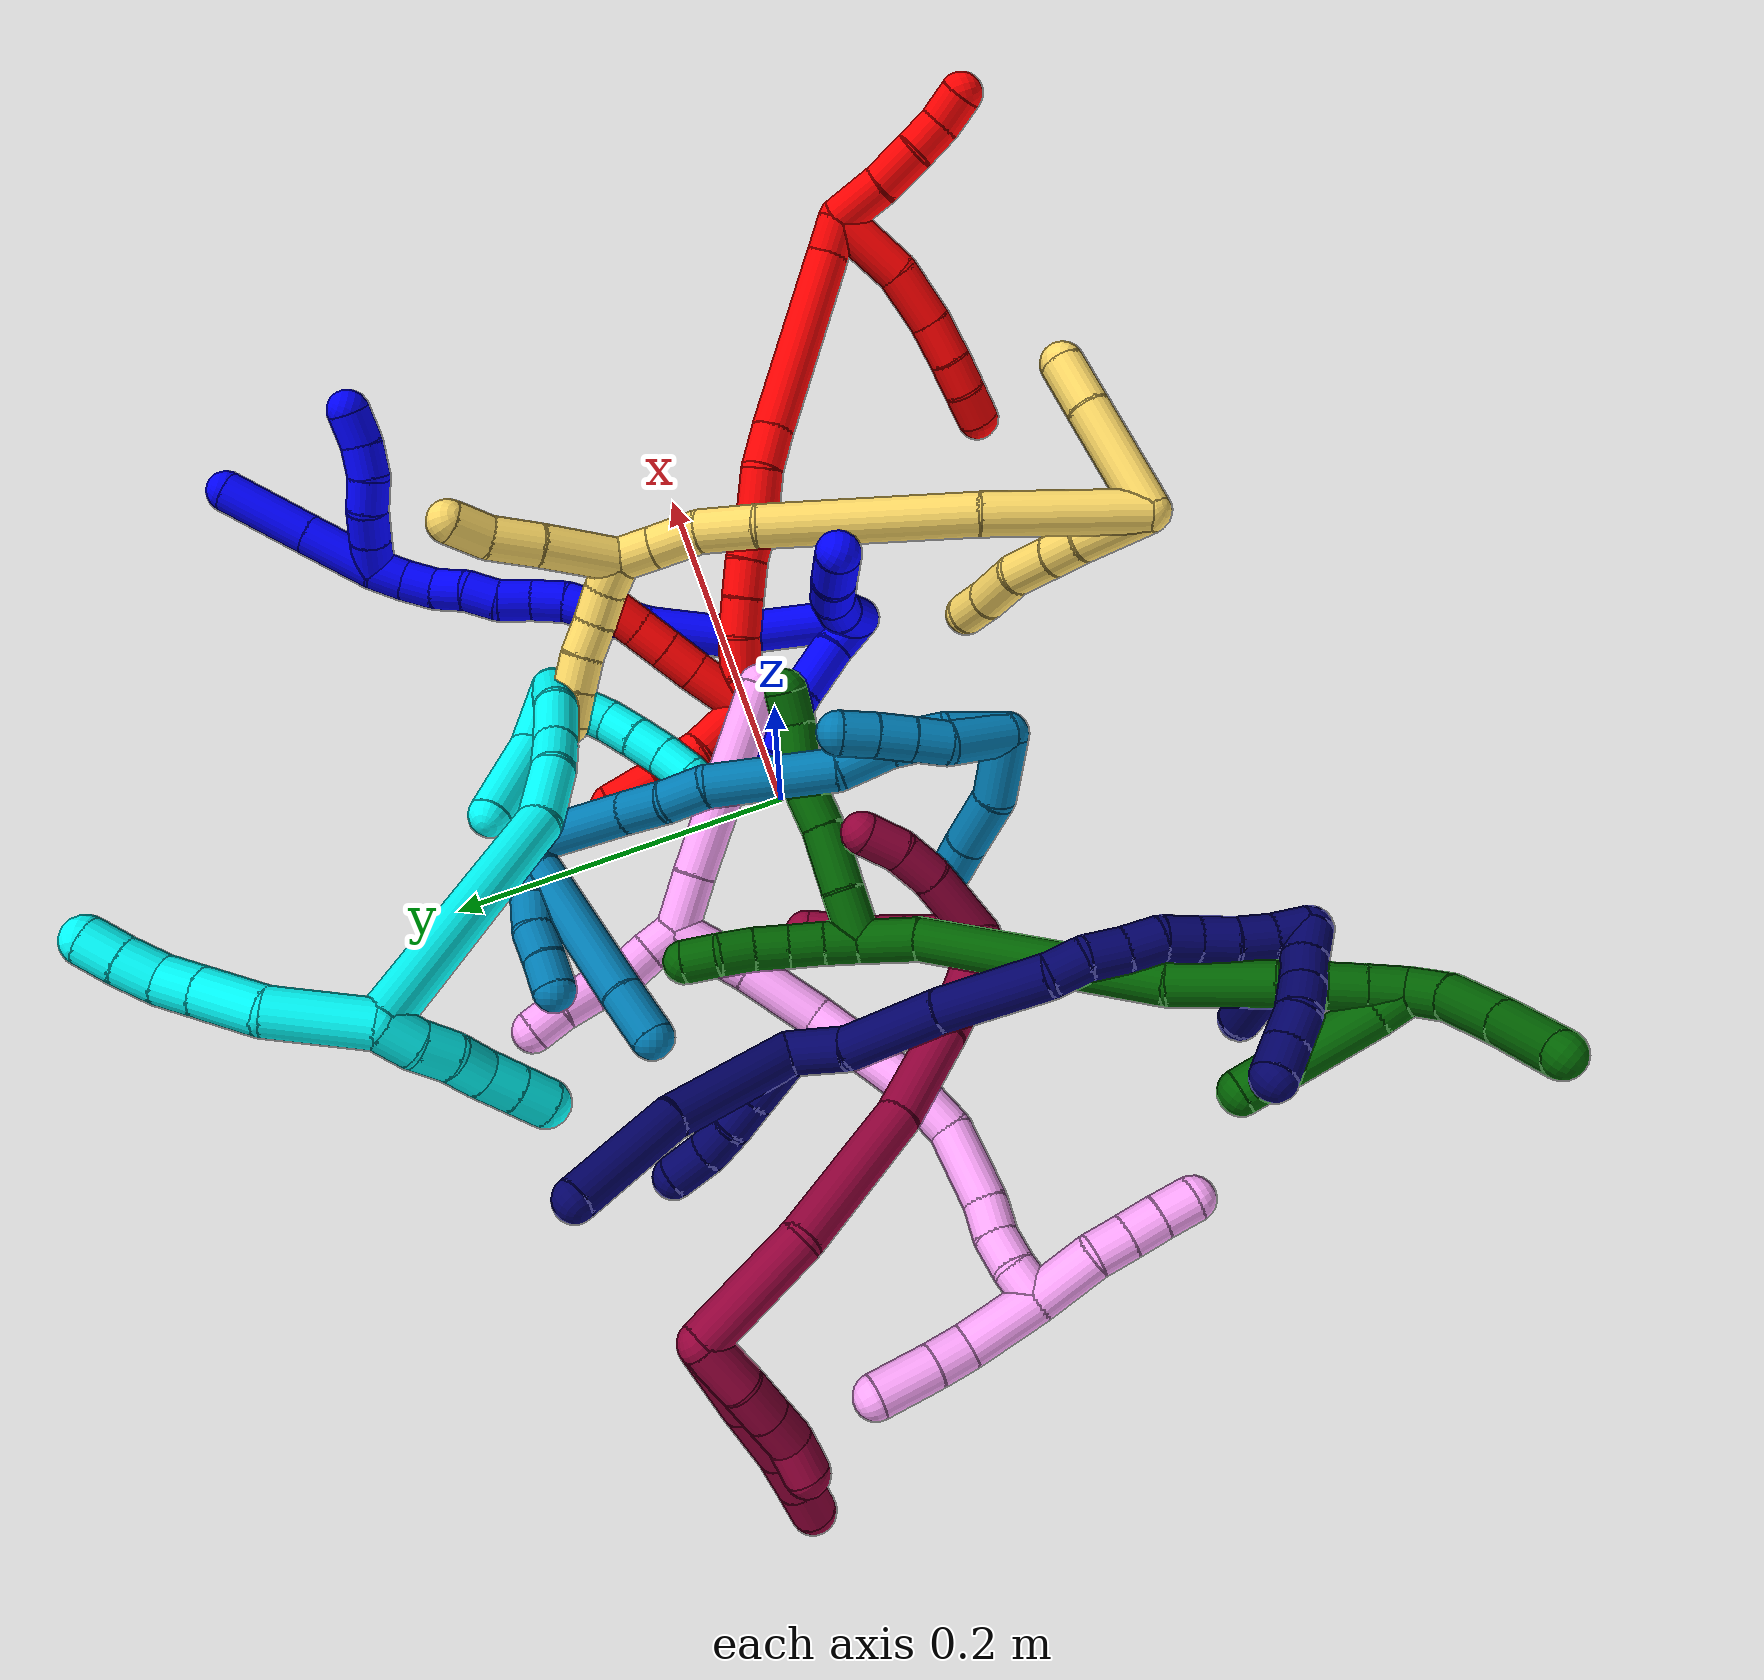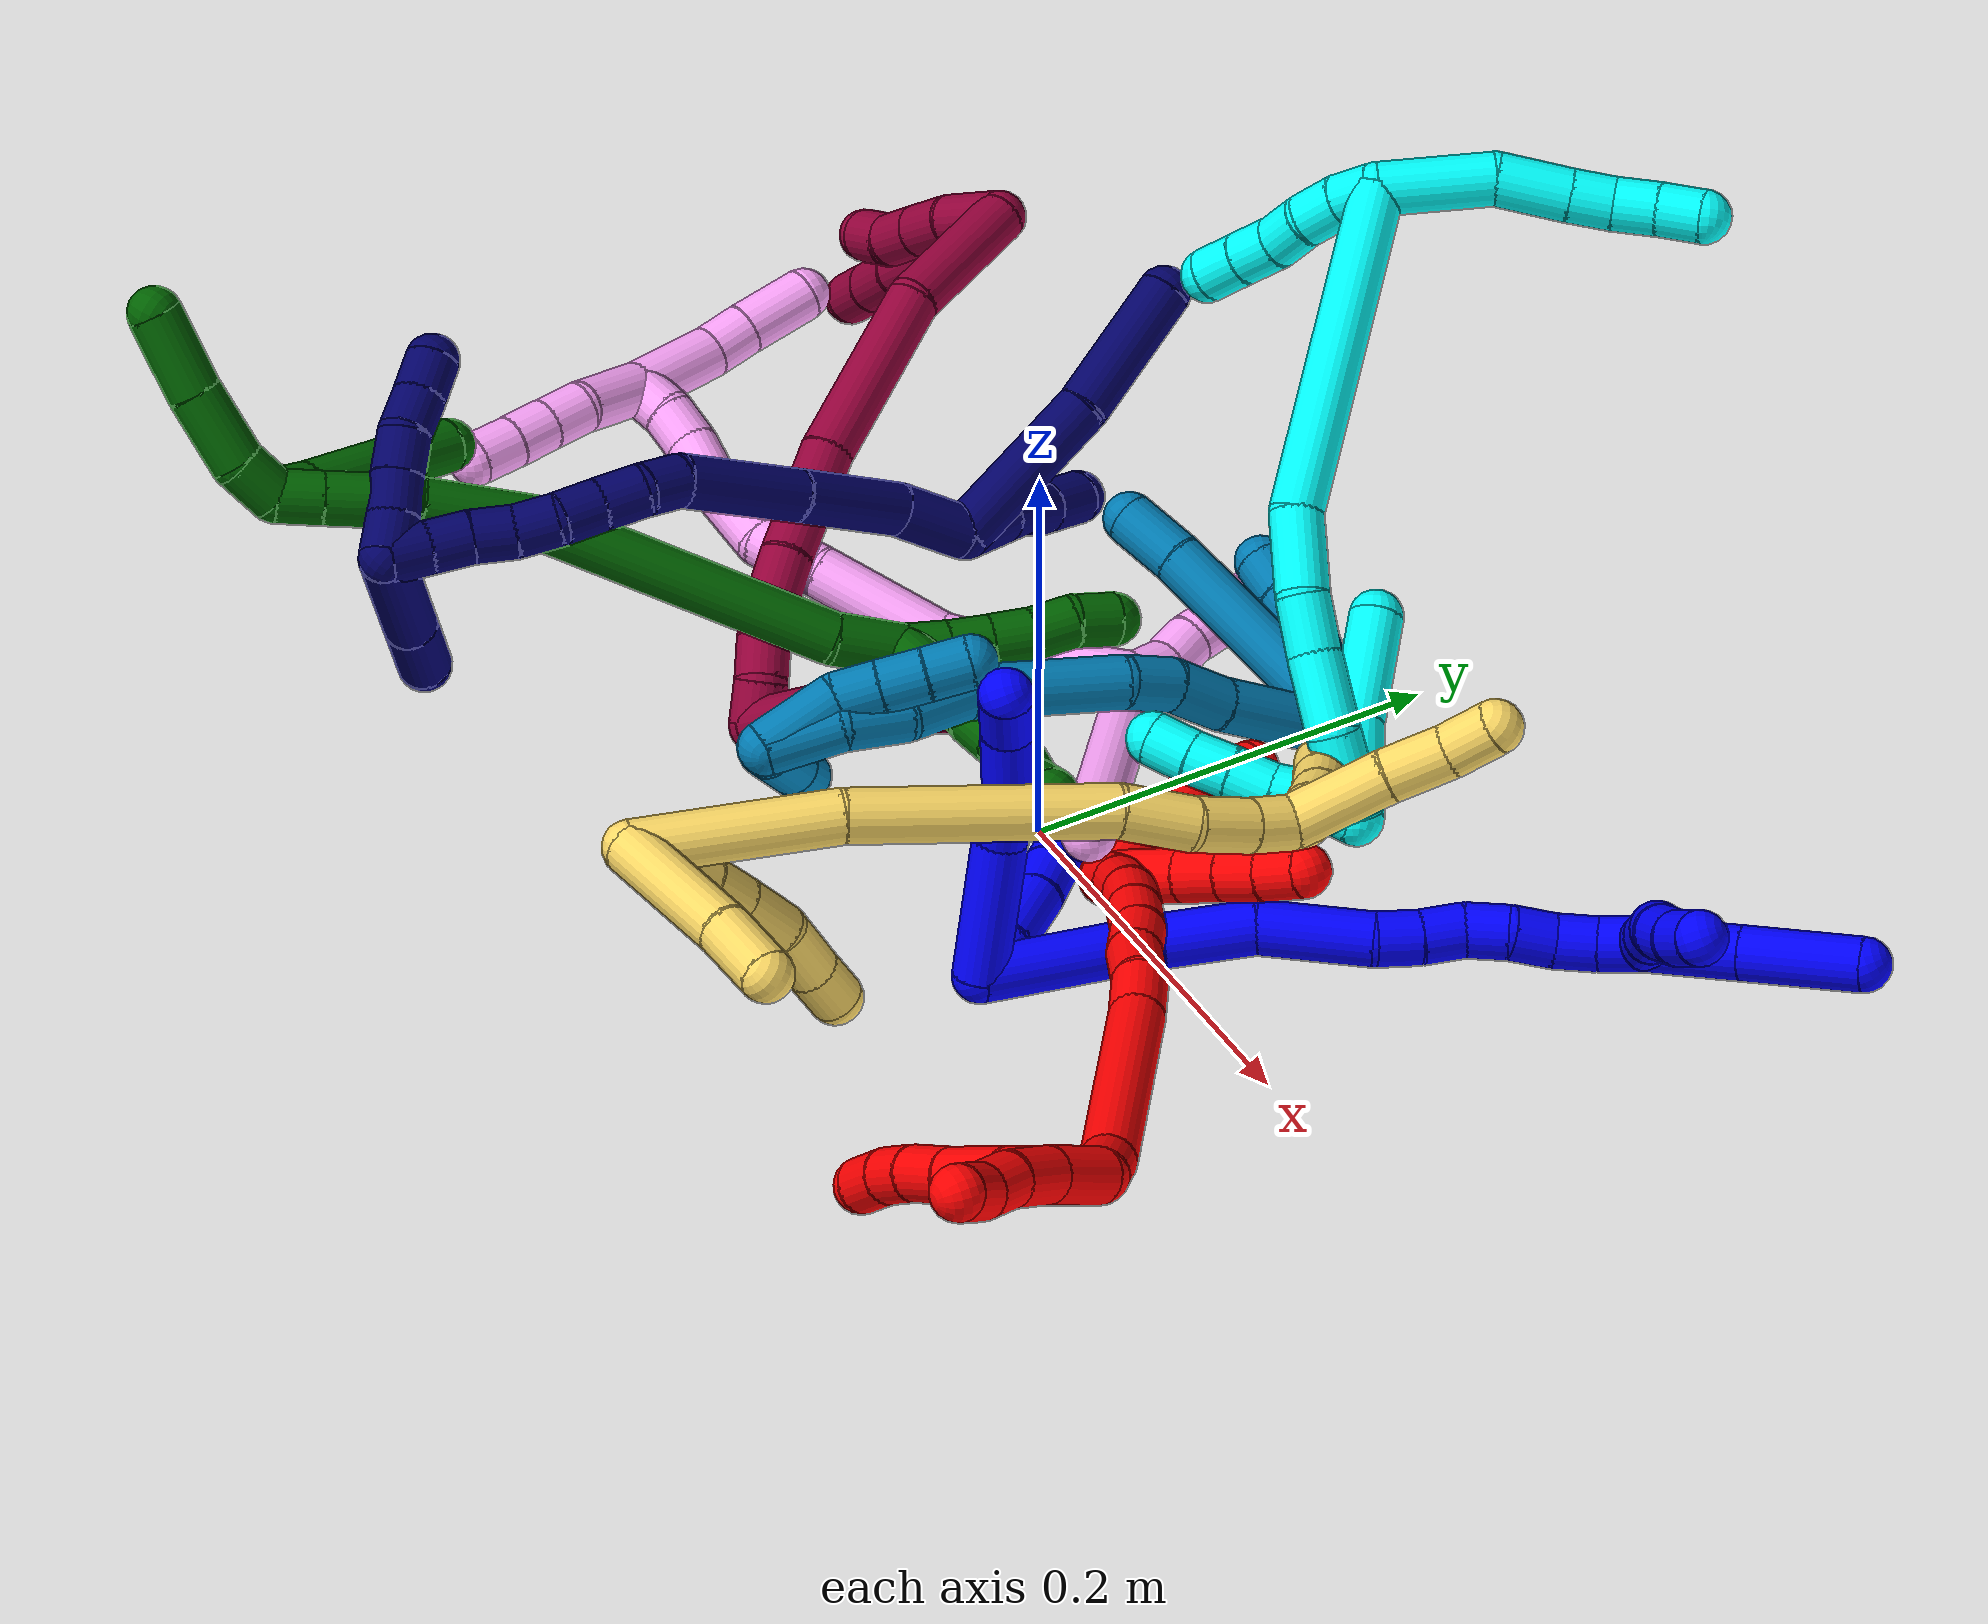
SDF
<sdf version="1.7">
 <world name="default">
  <plugin name="TubeGeneratorPlugin" filename="libtube_generator_plugin.so"/>
  <model name="photoneo_s_sensor">
   <static>1</static>
   <pose>0 0 2 1.57079 1.57079 3.14159</pose>
   <link name="link">
    <inertial><mass>0.1</mass></inertial>
    <sensor name="sensor" type="depth">
     <update_rate>30</update_rate>
     <camera>
      <horizontal_fov>1.22</horizontal_fov>
      <image><width>1920</width><height>1200</height><format>B8G8R8</format></image>
      <clip><near>0.1</near><far>4</far></clip>
      <depth_camera><output>points</output></depth_camera>
     </camera>
     <plugin name="camera_plugin" filename="libgazebo_ros_depth_camera.so">
      <baseline>0.2</baseline>
      <alwaysOn>1</alwaysOn>
      <updateRate>0.0</updateRate>
      <cameraName>camera_ir</cameraName>
      <imageTopicName>/camera/color/image_raw</imageTopicName>
      <cameraInfoTopicName>/camera/color/camera_info</cameraInfoTopicName>
      <depthImageTopicName>/camera/depth/image_raw</depthImageTopicName>
      <depthImageCameraInfoTopicName>/camera/depth/camera_info</depthImageCameraInfoTopicName>
      <pointCloudTopicName>/camera/depth/points</pointCloudTopicName>
      <frameName>fr_optical</frameName>
      <pointCloudCutoff>0.1</pointCloudCutoff>
      <pointCloudCutoffMax>2.0</pointCloudCutoffMax>
      <distortionK1>0</distortionK1>
      <distortionK2>0</distortionK2>
      <distortionK3>0</distortionK3>
      <distortionT1>0</distortionT1>
      <distortionT2>0</distortionT2>
      <CxPrime>0</CxPrime>
      <Cx>0</Cx>
      <Cy>0</Cy>
      <focalLength>0</focalLength>
      <hackBaseline>0</hackBaseline>
     </plugin>
    </sensor>
   </link>
  </model>
  <gravity>0 0 -9.8</gravity>
  <magnetic_field>6e-06 2.3e-05 -4.2e-05</magnetic_field>
  <atmosphere type="adiabatic"/>
  <physics name="default_physics" default="0" type="ode">
   <max_step_size>0.003</max_step_size>
   <real_time_factor>1</real_time_factor>
   <real_time_update_rate>1000</real_time_update_rate>
   <max_contacts>10000</max_contacts>
   <ode>
    <solver>
     <type>quick</type>
     <iters>100</iters>
     <sor>1.3</sor>
     <use_dynamic_moi_rescaling>0</use_dynamic_moi_rescaling>
    </solver>
    <constraints>
     <contact_max_correcting_vel>0</contact_max_correcting_vel>
     <contact_surface_layer>0.001</contact_surface_layer>
     <cfm>0</cfm>
     <erp>0.2</erp>
    </constraints>
   </ode>
  </physics>
  <scene><ambient>0.4 0.4 0.4 1</ambient><background>0.7 0.7 0.7 1</background><shadows>0</shadows></scene>
  <audio><device>default</device></audio>
  <spherical_coordinates>
   <surface_model>EARTH_WGS84</surface_model>
   <latitude_deg>0</latitude_deg>
   <longitude_deg>0</longitude_deg>
   <elevation>0</elevation>
   <heading_deg>0</heading_deg>
  </spherical_coordinates>
  <model name="bin">
   <static>1</static>
   <link name="bottom">
    <collision name="collision-bottom">
     <pose>0 0 -0.01 0 -0 0</pose>
     <geometry><box><size>0.8 0.6 0.02</size></box></geometry>
     <surface>
      <friction><ode><mu>100</mu><mu2>100</mu2></ode></friction>
      <contact><collide_bitmask>65535</collide_bitmask></contact>
     </surface>
    </collision>
   </link>
   <link name="west_wall">
    <collision name="collision-west_wall">
     <pose>-0.41 0 0.1 0 -0 0</pose>
     <geometry><box><size>0.02 0.6 0.2</size></box></geometry>
     <surface>
      <friction><ode><mu>100</mu><mu2>100</mu2></ode></friction>
      <contact><collide_bitmask>65535</collide_bitmask></contact>
     </surface>
    </collision>
   </link>
   <link name="east_wall">
    <collision name="collision-east_wall">
     <pose>0.41 0 0.1 0 -0 0</pose>
     <geometry><box><size>0.02 0.6 0.2</size></box></geometry>
     <surface>
      <friction><ode><mu>100</mu><mu2>100</mu2></ode></friction>
      <contact><collide_bitmask>65535</collide_bitmask></contact>
     </surface>
    </collision>
   </link>
   <link name="south_wall">
    <collision name="collision-south_wall">
     <pose>0 -0.31 0.1 0 -0 0</pose>
     <geometry><box><size>0.8 0.02 0.2</size></box></geometry>
     <surface>
      <friction><ode><mu>100</mu><mu2>100</mu2></ode></friction>
      <contact><collide_bitmask>65535</collide_bitmask></contact>
     </surface>
    </collision>
   </link>
   <link name="north_wall">
    <collision name="collision-north_wall">
     <pose>0 0.31 0.1 0 -0 0</pose>
     <geometry><box><size>0.8 0.02 0.2</size></box></geometry>
     <surface>
      <friction><ode><mu>100</mu><mu2>100</mu2></ode></friction>
      <contact><collide_bitmask>65535</collide_bitmask></contact>
     </surface>
    </collision>
   </link>
  </model>
  <model name="1">
   <static>0</static>
   <link name="1">
    <collision name="collision-cylinder-e_1_2_8">
     <pose>-0.017697 -0.02132 0.017835 0.874168 -0.566948 -0.27056</pose>
     <geometry><cylinder><radius>0.0125</radius><length>0.065904</length></cylinder></geometry>
     <surface>
      <friction><ode><mu>1.16</mu><mu2>1.16</mu2><slip1>0</slip1><slip2>0</slip2></ode></friction>
      <contact><ode><kp>1e+06</kp><kd>1</kd><max_vel>0</max_vel><min_depth>0.001</min_depth></ode></contact>
     </surface>
    </collision>
    <visual name="visual-cylinder-e_1_2_8">
     <pose>-0.017697 -0.02132 0.017835 0.874168 -0.566948 -0.27056</pose>
     <geometry><cylinder><radius>0.0125</radius><length>0.065904</length></cylinder></geometry>
     <material><ambient>0 0 1 1</ambient></material>
    </visual>
    <collision name="collision-cylinder-e_2_8_9">
     <pose>-0.039499 -0.051911 0.04321 0.888013 -0.330856 -0.158502</pose>
     <geometry><cylinder><radius>0.0125</radius><length>0.02527</length></cylinder></geometry>
     <surface>
      <friction><ode><mu>1.16</mu><mu2>1.16</mu2><slip1>0</slip1><slip2>0</slip2></ode></friction>
      <contact><ode><kp>1e+06</kp><kd>1</kd><max_vel>0</max_vel><min_depth>0.001</min_depth></ode></contact>
     </surface>
    </collision>
    <visual name="visual-cylinder-e_2_8_9">
     <pose>-0.039499 -0.051911 0.04321 0.888013 -0.330856 -0.158502</pose>
     <geometry><cylinder><radius>0.0125</radius><length>0.02527</length></cylinder></geometry>
     <material><ambient>0 0 1 1</ambient></material>
    </visual>
    <collision name="collision-cylinder-e_3_9_10">
     <pose>-0.049323 -0.075464 0.058083 1.09645 -0.342241 -0.21028</pose>
     <geometry><cylinder><radius>0.0125</radius><length>0.034086</length></cylinder></geometry>
     <surface>
      <friction><ode><mu>1.16</mu><mu2>1.16</mu2><slip1>0</slip1><slip2>0</slip2></ode></friction>
      <contact><ode><kp>1e+06</kp><kd>1</kd><max_vel>0</max_vel><min_depth>0.001</min_depth></ode></contact>
     </surface>
    </collision>
    <visual name="visual-cylinder-e_3_9_10">
     <pose>-0.049323 -0.075464 0.058083 1.09645 -0.342241 -0.21028</pose>
     <geometry><cylinder><radius>0.0125</radius><length>0.034086</length></cylinder></geometry>
     <material><ambient>0 0 1 1</ambient></material>
    </visual>
    <collision name="collision-cylinder-e_4_10_6">
     <pose>-0.055893 -0.100958 0.070572 1.13977 -0.068822 -0.044112</pose>
     <geometry><cylinder><radius>0.0125</radius><length>0.02474</length></cylinder></geometry>
     <surface>
      <friction><ode><mu>1.16</mu><mu2>1.16</mu2><slip1>0</slip1><slip2>0</slip2></ode></friction>
      <contact><ode><kp>1e+06</kp><kd>1</kd><max_vel>0</max_vel><min_depth>0.001</min_depth></ode></contact>
     </surface>
    </collision>
    <visual name="visual-cylinder-e_4_10_6">
     <pose>-0.055893 -0.100958 0.070572 1.13977 -0.068822 -0.044112</pose>
     <geometry><cylinder><radius>0.0125</radius><length>0.02474</length></cylinder></geometry>
     <material><ambient>0 0 1 1</ambient></material>
    </visual>
    <collision name="collision-cylinder-e_1_2_11">
     <pose>-0.009758 0.005284 0.005185 -0.794838 -0.921752 0.410966</pose>
     <geometry><cylinder><radius>0.0125</radius><length>0.024497</length></cylinder></geometry>
     <surface>
      <friction><ode><mu>1.16</mu><mu2>1.16</mu2><slip1>0</slip1><slip2>0</slip2></ode></friction>
      <contact><ode><kp>1e+06</kp><kd>1</kd><max_vel>0</max_vel><min_depth>0.001</min_depth></ode></contact>
     </surface>
    </collision>
    <visual name="visual-cylinder-e_1_2_11">
     <pose>-0.009758 0.005284 0.005185 -0.794838 -0.921752 0.410966</pose>
     <geometry><cylinder><radius>0.0125</radius><length>0.024497</length></cylinder></geometry>
     <material><ambient>0 0 1 1</ambient></material>
    </visual>
    <collision name="collision-cylinder-e_2_11_12">
     <pose>-0.033546 0.018295 0.015755 -0.962186 -0.979616 0.542864</pose>
     <geometry><cylinder><radius>0.0125</radius><length>0.033796</length></cylinder></geometry>
     <surface>
      <friction><ode><mu>1.16</mu><mu2>1.16</mu2><slip1>0</slip1><slip2>0</slip2></ode></friction>
      <contact><ode><kp>1e+06</kp><kd>1</kd><max_vel>0</max_vel><min_depth>0.001</min_depth></ode></contact>
     </surface>
    </collision>
    <visual name="visual-cylinder-e_2_11_12">
     <pose>-0.033546 0.018295 0.015755 -0.962186 -0.979616 0.542864</pose>
     <geometry><cylinder><radius>0.0125</radius><length>0.033796</length></cylinder></geometry>
     <material><ambient>0 0 1 1</ambient></material>
    </visual>
    <collision name="collision-cylinder-e_3_12_13">
     <pose>-0.05627 0.030498 0.023541 -1.07835 -1.04205 0.661534</pose>
     <geometry><cylinder><radius>0.0125</radius><length>0.020138</length></cylinder></geometry>
     <surface>
      <friction><ode><mu>1.16</mu><mu2>1.16</mu2><slip1>0</slip1><slip2>0</slip2></ode></friction>
      <contact><ode><kp>1e+06</kp><kd>1</kd><max_vel>0</max_vel><min_depth>0.001</min_depth></ode></contact>
     </surface>
    </collision>
    <visual name="visual-cylinder-e_3_12_13">
     <pose>-0.05627 0.030498 0.023541 -1.07835 -1.04205 0.661534</pose>
     <geometry><cylinder><radius>0.0125</radius><length>0.020138</length></cylinder></geometry>
     <material><ambient>0 0 1 1</ambient></material>
    </visual>
    <collision name="collision-cylinder-e_4_13_5">
     <pose>-0.073996 0.040347 0.028361 -1.1478 -0.9927 0.673557</pose>
     <geometry><cylinder><radius>0.0125</radius><length>0.021569</length></cylinder></geometry>
     <surface>
      <friction><ode><mu>1.16</mu><mu2>1.16</mu2><slip1>0</slip1><slip2>0</slip2></ode></friction>
      <contact><ode><kp>1e+06</kp><kd>1</kd><max_vel>0</max_vel><min_depth>0.001</min_depth></ode></contact>
     </surface>
    </collision>
    <visual name="visual-cylinder-e_4_13_5">
     <pose>-0.073996 0.040347 0.028361 -1.1478 -0.9927 0.673557</pose>
     <geometry><cylinder><radius>0.0125</radius><length>0.021569</length></cylinder></geometry>
     <material><ambient>0 0 1 1</ambient></material>
    </visual>
    <collision name="collision-cylinder-e_1_2_14">
     <pose>-0.007278 0.022068 0.034628 -0.56738 -0.175415 0.051263</pose>
     <geometry><cylinder><radius>0.0125</radius><length>0.083404</length></cylinder></geometry>
     <surface>
      <friction><ode><mu>1.16</mu><mu2>1.16</mu2><slip1>0</slip1><slip2>0</slip2></ode></friction>
      <contact><ode><kp>1e+06</kp><kd>1</kd><max_vel>0</max_vel><min_depth>0.001</min_depth></ode></contact>
     </surface>
    </collision>
    <visual name="visual-cylinder-e_1_2_14">
     <pose>-0.007278 0.022068 0.034628 -0.56738 -0.175415 0.051263</pose>
     <geometry><cylinder><radius>0.0125</radius><length>0.083404</length></cylinder></geometry>
     <material><ambient>0 0 1 1</ambient></material>
    </visual>
    <collision name="collision-cylinder-e_2_14_15">
     <pose>-0.014784 0.052154 0.089385 -0.379105 -0.010574 0.002029</pose>
     <geometry><cylinder><radius>0.0125</radius><length>0.043338</length></cylinder></geometry>
     <surface>
      <friction><ode><mu>1.16</mu><mu2>1.16</mu2><slip1>0</slip1><slip2>0</slip2></ode></friction>
      <contact><ode><kp>1e+06</kp><kd>1</kd><max_vel>0</max_vel><min_depth>0.001</min_depth></ode></contact>
     </surface>
    </collision>
    <visual name="visual-cylinder-e_2_14_15">
     <pose>-0.014784 0.052154 0.089385 -0.379105 -0.010574 0.002029</pose>
     <geometry><cylinder><radius>0.0125</radius><length>0.043338</length></cylinder></geometry>
     <material><ambient>0 0 1 1</ambient></material>
    </visual>
    <collision name="collision-cylinder-e_3_15_16">
     <pose>-0.008575 0.070922 0.132553 -0.436526 0.248047 -0.055286</pose>
     <geometry><cylinder><radius>0.0125</radius><length>0.052449</length></cylinder></geometry>
     <surface>
      <friction><ode><mu>1.16</mu><mu2>1.16</mu2><slip1>0</slip1><slip2>0</slip2></ode></friction>
      <contact><ode><kp>1e+06</kp><kd>1</kd><max_vel>0</max_vel><min_depth>0.001</min_depth></ode></contact>
     </surface>
    </collision>
    <visual name="visual-cylinder-e_3_15_16">
     <pose>-0.008575 0.070922 0.132553 -0.436526 0.248047 -0.055286</pose>
     <geometry><cylinder><radius>0.0125</radius><length>0.052449</length></cylinder></geometry>
     <material><ambient>0 0 1 1</ambient></material>
    </visual>
    <collision name="collision-cylinder-e_4_16_17">
     <pose>-0.001973 0.08682 0.164393 -0.529424 0.016088 -0.004361</pose>
     <geometry><cylinder><radius>0.0125</radius><length>0.020399</length></cylinder></geometry>
     <surface>
      <friction><ode><mu>1.16</mu><mu2>1.16</mu2><slip1>0</slip1><slip2>0</slip2></ode></friction>
      <contact><ode><kp>1e+06</kp><kd>1</kd><max_vel>0</max_vel><min_depth>0.001</min_depth></ode></contact>
     </surface>
    </collision>
    <visual name="visual-cylinder-e_4_16_17">
     <pose>-0.001973 0.08682 0.164393 -0.529424 0.016088 -0.004361</pose>
     <geometry><cylinder><radius>0.0125</radius><length>0.020399</length></cylinder></geometry>
     <material><ambient>0 0 1 1</ambient></material>
    </visual>
    <collision name="collision-cylinder-e_5_17_18">
     <pose>-0.002783 0.096633 0.182131 -0.480868 -0.096332 0.023636</pose>
     <geometry><cylinder><radius>0.0125</radius><length>0.020253</length></cylinder></geometry>
     <surface>
      <friction><ode><mu>1.16</mu><mu2>1.16</mu2><slip1>0</slip1><slip2>0</slip2></ode></friction>
      <contact><ode><kp>1e+06</kp><kd>1</kd><max_vel>0</max_vel><min_depth>0.001</min_depth></ode></contact>
     </surface>
    </collision>
    <visual name="visual-cylinder-e_5_17_18">
     <pose>-0.002783 0.096633 0.182131 -0.480868 -0.096332 0.023636</pose>
     <geometry><cylinder><radius>0.0125</radius><length>0.020253</length></cylinder></geometry>
     <material><ambient>0 0 1 1</ambient></material>
    </visual>
    <collision name="collision-cylinder-e_6_18_19">
     <pose>-0.001569 0.105088 0.20012 -0.396807 0.219279 -0.044256</pose>
     <geometry><cylinder><radius>0.0125</radius><length>0.020112</length></cylinder></geometry>
     <surface>
      <friction><ode><mu>1.16</mu><mu2>1.16</mu2><slip1>0</slip1><slip2>0</slip2></ode></friction>
      <contact><ode><kp>1e+06</kp><kd>1</kd><max_vel>0</max_vel><min_depth>0.001</min_depth></ode></contact>
     </surface>
    </collision>
    <visual name="visual-cylinder-e_6_18_19">
     <pose>-0.001569 0.105088 0.20012 -0.396807 0.219279 -0.044256</pose>
     <geometry><cylinder><radius>0.0125</radius><length>0.020112</length></cylinder></geometry>
     <material><ambient>0 0 1 1</ambient></material>
    </visual>
    <collision name="collision-cylinder-e_7_19_20">
     <pose>0.0022 0.115431 0.216579 -0.723989 0.158683 -0.060198</pose>
     <geometry><cylinder><radius>0.0125</radius><length>0.020025</length></cylinder></geometry>
     <surface>
      <friction><ode><mu>1.16</mu><mu2>1.16</mu2><slip1>0</slip1><slip2>0</slip2></ode></friction>
      <contact><ode><kp>1e+06</kp><kd>1</kd><max_vel>0</max_vel><min_depth>0.001</min_depth></ode></contact>
     </surface>
    </collision>
    <visual name="visual-cylinder-e_7_19_20">
     <pose>0.0022 0.115431 0.216579 -0.723989 0.158683 -0.060198</pose>
     <geometry><cylinder><radius>0.0125</radius><length>0.020025</length></cylinder></geometry>
     <material><ambient>0 0 1 1</ambient></material>
    </visual>
    <collision name="collision-cylinder-e_8_20_21">
     <pose>0.00588 0.12614 0.232844 -0.439077 0.211102 -0.047271</pose>
     <geometry><cylinder><radius>0.0125</radius><length>0.020017</length></cylinder></geometry>
     <surface>
      <friction><ode><mu>1.16</mu><mu2>1.16</mu2><slip1>0</slip1><slip2>0</slip2></ode></friction>
      <contact><ode><kp>1e+06</kp><kd>1</kd><max_vel>0</max_vel><min_depth>0.001</min_depth></ode></contact>
     </surface>
    </collision>
    <visual name="visual-cylinder-e_8_20_21">
     <pose>0.00588 0.12614 0.232844 -0.439077 0.211102 -0.047271</pose>
     <geometry><cylinder><radius>0.0125</radius><length>0.020017</length></cylinder></geometry>
     <material><ambient>0 0 1 1</ambient></material>
    </visual>
    <collision name="collision-cylinder-e_9_21_1">
     <pose>0.01006 0.133067 0.251085 -0.286778 0.209785 -0.030398</pose>
     <geometry><cylinder><radius>0.0125</radius><length>0.020003</length></cylinder></geometry>
     <surface>
      <friction><ode><mu>1.16</mu><mu2>1.16</mu2><slip1>0</slip1><slip2>0</slip2></ode></friction>
      <contact><ode><kp>1e+06</kp><kd>1</kd><max_vel>0</max_vel><min_depth>0.001</min_depth></ode></contact>
     </surface>
    </collision>
    <visual name="visual-cylinder-e_9_21_1">
     <pose>0.01006 0.133067 0.251085 -0.286778 0.209785 -0.030398</pose>
     <geometry><cylinder><radius>0.0125</radius><length>0.020003</length></cylinder></geometry>
     <material><ambient>0 0 1 1</ambient></material>
    </visual>
    <collision name="collision-cylinder-e_1_1_22">
     <pose>0.016064 0.127864 0.265062 1.04788 0.403006 0.234975</pose>
     <geometry><cylinder><radius>0.0125</radius><length>0.02</length></cylinder></geometry>
     <surface>
      <friction><ode><mu>1.16</mu><mu2>1.16</mu2><slip1>0</slip1><slip2>0</slip2></ode></friction>
      <contact><ode><kp>1e+06</kp><kd>1</kd><max_vel>0</max_vel><min_depth>0.001</min_depth></ode></contact>
     </surface>
    </collision>
    <visual name="visual-cylinder-e_1_1_22">
     <pose>0.016064 0.127864 0.265062 1.04788 0.403006 0.234975</pose>
     <geometry><cylinder><radius>0.0125</radius><length>0.02</length></cylinder></geometry>
     <material><ambient>0 0 1 1</ambient></material>
    </visual>
    <collision name="collision-cylinder-e_2_22_23">
     <pose>0.023918 0.111825 0.274062 1.07109 0.404103 0.241921</pose>
     <geometry><cylinder><radius>0.0125</radius><length>0.02</length></cylinder></geometry>
     <surface>
      <friction><ode><mu>1.16</mu><mu2>1.16</mu2><slip1>0</slip1><slip2>0</slip2></ode></friction>
      <contact><ode><kp>1e+06</kp><kd>1</kd><max_vel>0</max_vel><min_depth>0.001</min_depth></ode></contact>
     </surface>
    </collision>
    <visual name="visual-cylinder-e_2_22_23">
     <pose>0.023918 0.111825 0.274062 1.07109 0.404103 0.241921</pose>
     <geometry><cylinder><radius>0.0125</radius><length>0.02</length></cylinder></geometry>
     <material><ambient>0 0 1 1</ambient></material>
    </visual>
    <collision name="collision-cylinder-e_3_23_24">
     <pose>0.033801 0.09632 0.281518 1.18139 0.637409 0.435492</pose>
     <geometry><cylinder><radius>0.0125</radius><length>0.02</length></cylinder></geometry>
     <surface>
      <friction><ode><mu>1.16</mu><mu2>1.16</mu2><slip1>0</slip1><slip2>0</slip2></ode></friction>
      <contact><ode><kp>1e+06</kp><kd>1</kd><max_vel>0</max_vel><min_depth>0.001</min_depth></ode></contact>
     </surface>
    </collision>
    <visual name="visual-cylinder-e_3_23_24">
     <pose>0.033801 0.09632 0.281518 1.18139 0.637409 0.435492</pose>
     <geometry><cylinder><radius>0.0125</radius><length>0.02</length></cylinder></geometry>
     <material><ambient>0 0 1 1</ambient></material>
    </visual>
    <collision name="collision-cylinder-e_4_24_25">
     <pose>0.046192 0.083378 0.28988 0.803548 0.699689 0.307593</pose>
     <geometry><cylinder><radius>0.0125</radius><length>0.02</length></cylinder></geometry>
     <surface>
      <friction><ode><mu>1.16</mu><mu2>1.16</mu2><slip1>0</slip1><slip2>0</slip2></ode></friction>
      <contact><ode><kp>1e+06</kp><kd>1</kd><max_vel>0</max_vel><min_depth>0.001</min_depth></ode></contact>
     </surface>
    </collision>
    <visual name="visual-cylinder-e_4_24_25">
     <pose>0.046192 0.083378 0.28988 0.803548 0.699689 0.307593</pose>
     <geometry><cylinder><radius>0.0125</radius><length>0.02</length></cylinder></geometry>
     <material><ambient>0 0 1 1</ambient></material>
    </visual>
    <collision name="collision-cylinder-e_5_25_4">
     <pose>0.057969 0.072704 0.301886 0.657216 0.562943 0.196547</pose>
     <geometry><cylinder><radius>0.0125</radius><length>0.02</length></cylinder></geometry>
     <surface>
      <friction><ode><mu>1.16</mu><mu2>1.16</mu2><slip1>0</slip1><slip2>0</slip2></ode></friction>
      <contact><ode><kp>1e+06</kp><kd>1</kd><max_vel>0</max_vel><min_depth>0.001</min_depth></ode></contact>
     </surface>
    </collision>
    <visual name="visual-cylinder-e_5_25_4">
     <pose>0.057969 0.072704 0.301886 0.657216 0.562943 0.196547</pose>
     <geometry><cylinder><radius>0.0125</radius><length>0.02</length></cylinder></geometry>
     <material><ambient>0 0 1 1</ambient></material>
    </visual>
    <collision name="collision-cylinder-e_1_1_26">
     <pose>0.019689 0.140895 0.280844 -0.24344 0.345064 -0.042627</pose>
     <geometry><cylinder><radius>0.0125</radius><length>0.044621</length></cylinder></geometry>
     <surface>
      <friction><ode><mu>1.16</mu><mu2>1.16</mu2><slip1>0</slip1><slip2>0</slip2></ode></friction>
      <contact><ode><kp>1e+06</kp><kd>1</kd><max_vel>0</max_vel><min_depth>0.001</min_depth></ode></contact>
     </surface>
    </collision>
    <visual name="visual-cylinder-e_1_1_26">
     <pose>0.019689 0.140895 0.280844 -0.24344 0.345064 -0.042627</pose>
     <geometry><cylinder><radius>0.0125</radius><length>0.044621</length></cylinder></geometry>
     <material><ambient>0 0 1 1</ambient></material>
    </visual>
    <collision name="collision-cylinder-e_2_26_3">
     <pose>0.036709 0.152184 0.326483 -0.241742 0.34915 -0.042838</pose>
     <geometry><cylinder><radius>0.0125</radius><length>0.055379</length></cylinder></geometry>
     <surface>
      <friction><ode><mu>1.16</mu><mu2>1.16</mu2><slip1>0</slip1><slip2>0</slip2></ode></friction>
      <contact><ode><kp>1e+06</kp><kd>1</kd><max_vel>0</max_vel><min_depth>0.001</min_depth></ode></contact>
     </surface>
    </collision>
    <visual name="visual-cylinder-e_2_26_3">
     <pose>0.036709 0.152184 0.326483 -0.241742 0.34915 -0.042838</pose>
     <geometry><cylinder><radius>0.0125</radius><length>0.055379</length></cylinder></geometry>
     <material><ambient>0 0 1 1</ambient></material>
    </visual>
    <collision name="collision-sphere-3">
     <pose>0.046181 0.158413 0.351745 0 -0 0</pose>
     <geometry><sphere><radius>0.0125</radius></sphere></geometry>
     <surface>
      <friction><ode><mu>1.16</mu><mu2>1.16</mu2><slip1>0</slip1><slip2>0</slip2></ode></friction>
      <contact><ode><kp>1e+06</kp><kd>1</kd><max_vel>0</max_vel><min_depth>0.001</min_depth></ode></contact>
     </surface>
    </collision>
    <visual name="visual-sphere-3">
     <pose>0.046181 0.158413 0.351745 0 -0 0</pose>
     <geometry><sphere><radius>0.0125</radius></sphere></geometry>
     <material><ambient>0 0 1 1</ambient></material>
    </visual>
    <collision name="collision-sphere-26">
     <pose>0.027236 0.145956 0.301221 0 -0 0</pose>
     <geometry><sphere><radius>0.0125</radius></sphere></geometry>
     <surface>
      <friction><ode><mu>1.16</mu><mu2>1.16</mu2><slip1>0</slip1><slip2>0</slip2></ode></friction>
      <contact><ode><kp>1e+06</kp><kd>1</kd><max_vel>0</max_vel><min_depth>0.001</min_depth></ode></contact>
     </surface>
    </collision>
    <visual name="visual-sphere-26">
     <pose>0.027236 0.145956 0.301221 0 -0 0</pose>
     <geometry><sphere><radius>0.0125</radius></sphere></geometry>
     <material><ambient>0 0 1 1</ambient></material>
    </visual>
    <collision name="collision-sphere-4">
     <pose>0.063306 0.067538 0.308581 0 -0 0</pose>
     <geometry><sphere><radius>0.0125</radius></sphere></geometry>
     <surface>
      <friction><ode><mu>1.16</mu><mu2>1.16</mu2><slip1>0</slip1><slip2>0</slip2></ode></friction>
      <contact><ode><kp>1e+06</kp><kd>1</kd><max_vel>0</max_vel><min_depth>0.001</min_depth></ode></contact>
     </surface>
    </collision>
    <visual name="visual-sphere-4">
     <pose>0.063306 0.067538 0.308581 0 -0 0</pose>
     <geometry><sphere><radius>0.0125</radius></sphere></geometry>
     <material><ambient>0 0 1 1</ambient></material>
    </visual>
    <collision name="collision-sphere-25">
     <pose>0.052632 0.077871 0.295191 0 -0 0</pose>
     <geometry><sphere><radius>0.0125</radius></sphere></geometry>
     <surface>
      <friction><ode><mu>1.16</mu><mu2>1.16</mu2><slip1>0</slip1><slip2>0</slip2></ode></friction>
      <contact><ode><kp>1e+06</kp><kd>1</kd><max_vel>0</max_vel><min_depth>0.001</min_depth></ode></contact>
     </surface>
    </collision>
    <visual name="visual-sphere-25">
     <pose>0.052632 0.077871 0.295191 0 -0 0</pose>
     <geometry><sphere><radius>0.0125</radius></sphere></geometry>
     <material><ambient>0 0 1 1</ambient></material>
    </visual>
    <collision name="collision-sphere-24">
     <pose>0.039752 0.088885 0.284569 0 -0 0</pose>
     <geometry><sphere><radius>0.0125</radius></sphere></geometry>
     <surface>
      <friction><ode><mu>1.16</mu><mu2>1.16</mu2><slip1>0</slip1><slip2>0</slip2></ode></friction>
      <contact><ode><kp>1e+06</kp><kd>1</kd><max_vel>0</max_vel><min_depth>0.001</min_depth></ode></contact>
     </surface>
    </collision>
    <visual name="visual-sphere-24">
     <pose>0.039752 0.088885 0.284569 0 -0 0</pose>
     <geometry><sphere><radius>0.0125</radius></sphere></geometry>
     <material><ambient>0 0 1 1</ambient></material>
    </visual>
    <collision name="collision-sphere-23">
     <pose>0.02785 0.103754 0.278467 0 -0 0</pose>
     <geometry><sphere><radius>0.0125</radius></sphere></geometry>
     <surface>
      <friction><ode><mu>1.16</mu><mu2>1.16</mu2><slip1>0</slip1><slip2>0</slip2></ode></friction>
      <contact><ode><kp>1e+06</kp><kd>1</kd><max_vel>0</max_vel><min_depth>0.001</min_depth></ode></contact>
     </surface>
    </collision>
    <visual name="visual-sphere-23">
     <pose>0.02785 0.103754 0.278467 0 -0 0</pose>
     <geometry><sphere><radius>0.0125</radius></sphere></geometry>
     <material><ambient>0 0 1 1</ambient></material>
    </visual>
    <collision name="collision-sphere-22">
     <pose>0.019986 0.119895 0.269656 0 -0 0</pose>
     <geometry><sphere><radius>0.0125</radius></sphere></geometry>
     <surface>
      <friction><ode><mu>1.16</mu><mu2>1.16</mu2><slip1>0</slip1><slip2>0</slip2></ode></friction>
      <contact><ode><kp>1e+06</kp><kd>1</kd><max_vel>0</max_vel><min_depth>0.001</min_depth></ode></contact>
     </surface>
    </collision>
    <visual name="visual-sphere-22">
     <pose>0.019986 0.119895 0.269656 0 -0 0</pose>
     <geometry><sphere><radius>0.0125</radius></sphere></geometry>
     <material><ambient>0 0 1 1</ambient></material>
    </visual>
    <collision name="collision-sphere-1">
     <pose>0.012143 0.135834 0.260468 0 -0 0</pose>
     <geometry><sphere><radius>0.0125</radius></sphere></geometry>
     <surface>
      <friction><ode><mu>1.16</mu><mu2>1.16</mu2><slip1>0</slip1><slip2>0</slip2></ode></friction>
      <contact><ode><kp>1e+06</kp><kd>1</kd><max_vel>0</max_vel><min_depth>0.001</min_depth></ode></contact>
     </surface>
    </collision>
    <visual name="visual-sphere-1">
     <pose>0.012143 0.135834 0.260468 0 -0 0</pose>
     <geometry><sphere><radius>0.0125</radius></sphere></geometry>
     <material><ambient>0 0 1 1</ambient></material>
    </visual>
    <collision name="collision-sphere-21">
     <pose>0.007977 0.1303 0.241702 0 -0 0</pose>
     <geometry><sphere><radius>0.0125</radius></sphere></geometry>
     <surface>
      <friction><ode><mu>1.16</mu><mu2>1.16</mu2><slip1>0</slip1><slip2>0</slip2></ode></friction>
      <contact><ode><kp>1e+06</kp><kd>1</kd><max_vel>0</max_vel><min_depth>0.001</min_depth></ode></contact>
     </surface>
    </collision>
    <visual name="visual-sphere-21">
     <pose>0.007977 0.1303 0.241702 0 -0 0</pose>
     <geometry><sphere><radius>0.0125</radius></sphere></geometry>
     <material><ambient>0 0 1 1</ambient></material>
    </visual>
    <collision name="collision-sphere-11">
     <pose>-0.019515 0.010568 0.01037 0 -0 0</pose>
     <geometry><sphere><radius>0.0125</radius></sphere></geometry>
     <surface>
      <friction><ode><mu>1.16</mu><mu2>1.16</mu2><slip1>0</slip1><slip2>0</slip2></ode></friction>
      <contact><ode><kp>1e+06</kp><kd>1</kd><max_vel>0</max_vel><min_depth>0.001</min_depth></ode></contact>
     </surface>
    </collision>
    <visual name="visual-sphere-11">
     <pose>-0.019515 0.010568 0.01037 0 -0 0</pose>
     <geometry><sphere><radius>0.0125</radius></sphere></geometry>
     <material><ambient>0 0 1 1</ambient></material>
    </visual>
    <collision name="collision-sphere-6">
     <pose>-0.056744 -0.11217 0.075728 0 -0 0</pose>
     <geometry><sphere><radius>0.0125</radius></sphere></geometry>
     <surface>
      <friction><ode><mu>1.16</mu><mu2>1.16</mu2><slip1>0</slip1><slip2>0</slip2></ode></friction>
      <contact><ode><kp>1e+06</kp><kd>1</kd><max_vel>0</max_vel><min_depth>0.001</min_depth></ode></contact>
     </surface>
    </collision>
    <visual name="visual-sphere-6">
     <pose>-0.056744 -0.11217 0.075728 0 -0 0</pose>
     <geometry><sphere><radius>0.0125</radius></sphere></geometry>
     <material><ambient>0 0 1 1</ambient></material>
    </visual>
    <collision name="collision-sphere-10">
     <pose>-0.055043 -0.089746 0.065416 0 -0 0</pose>
     <geometry><sphere><radius>0.0125</radius></sphere></geometry>
     <surface>
      <friction><ode><mu>1.16</mu><mu2>1.16</mu2><slip1>0</slip1><slip2>0</slip2></ode></friction>
      <contact><ode><kp>1e+06</kp><kd>1</kd><max_vel>0</max_vel><min_depth>0.001</min_depth></ode></contact>
     </surface>
    </collision>
    <visual name="visual-sphere-10">
     <pose>-0.055043 -0.089746 0.065416 0 -0 0</pose>
     <geometry><sphere><radius>0.0125</radius></sphere></geometry>
     <material><ambient>0 0 1 1</ambient></material>
    </visual>
    <collision name="collision-sphere-9">
     <pose>-0.043604 -0.061182 0.05075 0 -0 0</pose>
     <geometry><sphere><radius>0.0125</radius></sphere></geometry>
     <surface>
      <friction><ode><mu>1.16</mu><mu2>1.16</mu2><slip1>0</slip1><slip2>0</slip2></ode></friction>
      <contact><ode><kp>1e+06</kp><kd>1</kd><max_vel>0</max_vel><min_depth>0.001</min_depth></ode></contact>
     </surface>
    </collision>
    <visual name="visual-sphere-9">
     <pose>-0.043604 -0.061182 0.05075 0 -0 0</pose>
     <geometry><sphere><radius>0.0125</radius></sphere></geometry>
     <material><ambient>0 0 1 1</ambient></material>
    </visual>
    <collision name="collision-sphere-2">
     <geometry><sphere><radius>0.0125</radius></sphere></geometry>
     <surface>
      <friction><ode><mu>1.16</mu><mu2>1.16</mu2><slip1>0</slip1><slip2>0</slip2></ode></friction>
      <contact><ode><kp>1e+06</kp><kd>1</kd><max_vel>0</max_vel><min_depth>0.001</min_depth></ode></contact>
     </surface>
    </collision>
    <visual name="visual-sphere-2">
     <geometry><sphere><radius>0.0125</radius></sphere></geometry>
     <material><ambient>0 0 1 1</ambient></material>
    </visual>
    <collision name="collision-sphere-19">
     <pose>0.000618 0.108882 0.209172 0 -0 0</pose>
     <geometry><sphere><radius>0.0125</radius></sphere></geometry>
     <surface>
      <friction><ode><mu>1.16</mu><mu2>1.16</mu2><slip1>0</slip1><slip2>0</slip2></ode></friction>
      <contact><ode><kp>1e+06</kp><kd>1</kd><max_vel>0</max_vel><min_depth>0.001</min_depth></ode></contact>
     </surface>
    </collision>
    <visual name="visual-sphere-19">
     <pose>0.000618 0.108882 0.209172 0 -0 0</pose>
     <geometry><sphere><radius>0.0125</radius></sphere></geometry>
     <material><ambient>0 0 1 1</ambient></material>
    </visual>
    <collision name="collision-sphere-8">
     <pose>-0.035395 -0.042641 0.035671 0 -0 0</pose>
     <geometry><sphere><radius>0.0125</radius></sphere></geometry>
     <surface>
      <friction><ode><mu>1.16</mu><mu2>1.16</mu2><slip1>0</slip1><slip2>0</slip2></ode></friction>
      <contact><ode><kp>1e+06</kp><kd>1</kd><max_vel>0</max_vel><min_depth>0.001</min_depth></ode></contact>
     </surface>
    </collision>
    <visual name="visual-sphere-8">
     <pose>-0.035395 -0.042641 0.035671 0 -0 0</pose>
     <geometry><sphere><radius>0.0125</radius></sphere></geometry>
     <material><ambient>0 0 1 1</ambient></material>
    </visual>
    <collision name="collision-sphere-12">
     <pose>-0.047576 0.026022 0.02114 0 -0 0</pose>
     <geometry><sphere><radius>0.0125</radius></sphere></geometry>
     <surface>
      <friction><ode><mu>1.16</mu><mu2>1.16</mu2><slip1>0</slip1><slip2>0</slip2></ode></friction>
      <contact><ode><kp>1e+06</kp><kd>1</kd><max_vel>0</max_vel><min_depth>0.001</min_depth></ode></contact>
     </surface>
    </collision>
    <visual name="visual-sphere-12">
     <pose>-0.047576 0.026022 0.02114 0 -0 0</pose>
     <geometry><sphere><radius>0.0125</radius></sphere></geometry>
     <material><ambient>0 0 1 1</ambient></material>
    </visual>
    <collision name="collision-sphere-13">
     <pose>-0.064964 0.034974 0.025942 0 -0 0</pose>
     <geometry><sphere><radius>0.0125</radius></sphere></geometry>
     <surface>
      <friction><ode><mu>1.16</mu><mu2>1.16</mu2><slip1>0</slip1><slip2>0</slip2></ode></friction>
      <contact><ode><kp>1e+06</kp><kd>1</kd><max_vel>0</max_vel><min_depth>0.001</min_depth></ode></contact>
     </surface>
    </collision>
    <visual name="visual-sphere-13">
     <pose>-0.064964 0.034974 0.025942 0 -0 0</pose>
     <geometry><sphere><radius>0.0125</radius></sphere></geometry>
     <material><ambient>0 0 1 1</ambient></material>
    </visual>
    <collision name="collision-sphere-5">
     <pose>-0.083028 0.045721 0.030781 0 -0 0</pose>
     <geometry><sphere><radius>0.0125</radius></sphere></geometry>
     <surface>
      <friction><ode><mu>1.16</mu><mu2>1.16</mu2><slip1>0</slip1><slip2>0</slip2></ode></friction>
      <contact><ode><kp>1e+06</kp><kd>1</kd><max_vel>0</max_vel><min_depth>0.001</min_depth></ode></contact>
     </surface>
    </collision>
    <visual name="visual-sphere-5">
     <pose>-0.083028 0.045721 0.030781 0 -0 0</pose>
     <geometry><sphere><radius>0.0125</radius></sphere></geometry>
     <material><ambient>0 0 1 1</ambient></material>
    </visual>
    <collision name="collision-sphere-14">
     <pose>-0.014555 0.044135 0.069256 0 -0 0</pose>
     <geometry><sphere><radius>0.0125</radius></sphere></geometry>
     <surface>
      <friction><ode><mu>1.16</mu><mu2>1.16</mu2><slip1>0</slip1><slip2>0</slip2></ode></friction>
      <contact><ode><kp>1e+06</kp><kd>1</kd><max_vel>0</max_vel><min_depth>0.001</min_depth></ode></contact>
     </surface>
    </collision>
    <visual name="visual-sphere-14">
     <pose>-0.014555 0.044135 0.069256 0 -0 0</pose>
     <geometry><sphere><radius>0.0125</radius></sphere></geometry>
     <material><ambient>0 0 1 1</ambient></material>
    </visual>
    <collision name="collision-sphere-15">
     <pose>-0.015014 0.060174 0.109515 0 -0 0</pose>
     <geometry><sphere><radius>0.0125</radius></sphere></geometry>
     <surface>
      <friction><ode><mu>1.16</mu><mu2>1.16</mu2><slip1>0</slip1><slip2>0</slip2></ode></friction>
      <contact><ode><kp>1e+06</kp><kd>1</kd><max_vel>0</max_vel><min_depth>0.001</min_depth></ode></contact>
     </surface>
    </collision>
    <visual name="visual-sphere-15">
     <pose>-0.015014 0.060174 0.109515 0 -0 0</pose>
     <geometry><sphere><radius>0.0125</radius></sphere></geometry>
     <material><ambient>0 0 1 1</ambient></material>
    </visual>
    <collision name="collision-sphere-16">
     <pose>-0.002137 0.08167 0.155591 0 -0 0</pose>
     <geometry><sphere><radius>0.0125</radius></sphere></geometry>
     <surface>
      <friction><ode><mu>1.16</mu><mu2>1.16</mu2><slip1>0</slip1><slip2>0</slip2></ode></friction>
      <contact><ode><kp>1e+06</kp><kd>1</kd><max_vel>0</max_vel><min_depth>0.001</min_depth></ode></contact>
     </surface>
    </collision>
    <visual name="visual-sphere-16">
     <pose>-0.002137 0.08167 0.155591 0 -0 0</pose>
     <geometry><sphere><radius>0.0125</radius></sphere></geometry>
     <material><ambient>0 0 1 1</ambient></material>
    </visual>
    <collision name="collision-sphere-17">
     <pose>-0.001809 0.091971 0.173195 0 -0 0</pose>
     <geometry><sphere><radius>0.0125</radius></sphere></geometry>
     <surface>
      <friction><ode><mu>1.16</mu><mu2>1.16</mu2><slip1>0</slip1><slip2>0</slip2></ode></friction>
      <contact><ode><kp>1e+06</kp><kd>1</kd><max_vel>0</max_vel><min_depth>0.001</min_depth></ode></contact>
     </surface>
    </collision>
    <visual name="visual-sphere-17">
     <pose>-0.001809 0.091971 0.173195 0 -0 0</pose>
     <geometry><sphere><radius>0.0125</radius></sphere></geometry>
     <material><ambient>0 0 1 1</ambient></material>
    </visual>
    <collision name="collision-sphere-18">
     <pose>-0.003757 0.101295 0.191067 0 -0 0</pose>
     <geometry><sphere><radius>0.0125</radius></sphere></geometry>
     <surface>
      <friction><ode><mu>1.16</mu><mu2>1.16</mu2><slip1>0</slip1><slip2>0</slip2></ode></friction>
      <contact><ode><kp>1e+06</kp><kd>1</kd><max_vel>0</max_vel><min_depth>0.001</min_depth></ode></contact>
     </surface>
    </collision>
    <visual name="visual-sphere-18">
     <pose>-0.003757 0.101295 0.191067 0 -0 0</pose>
     <geometry><sphere><radius>0.0125</radius></sphere></geometry>
     <material><ambient>0 0 1 1</ambient></material>
    </visual>
    <collision name="collision-sphere-20">
     <pose>0.003783 0.121979 0.223986 0 -0 0</pose>
     <geometry><sphere><radius>0.0125</radius></sphere></geometry>
     <surface>
      <friction><ode><mu>1.16</mu><mu2>1.16</mu2><slip1>0</slip1><slip2>0</slip2></ode></friction>
      <contact><ode><kp>1e+06</kp><kd>1</kd><max_vel>0</max_vel><min_depth>0.001</min_depth></ode></contact>
     </surface>
    </collision>
    <visual name="visual-sphere-20">
     <pose>0.003783 0.121979 0.223986 0 -0 0</pose>
     <geometry><sphere><radius>0.0125</radius></sphere></geometry>
     <material><ambient>0 0 1 1</ambient></material>
    </visual>
    <inertial>
     <pose>-0.005764 0.05355 0.140533 0 -0 0</pose>
     <mass>0.75</mass>
     <inertia>
      <ixx>0.000141</ixx>
      <ixy>0</ixy>
      <ixz>0</ixz>
      <iyy>0.000134</iyy>
      <iyz>0</iyz>
      <izz>3.6e-05</izz>
     </inertia>
    </inertial>
   </link>
   <pose>0.087238 -0.080366 0.013606 -1.07529 0.303109 -0.403824</pose>
  </model>
  <model name="2">
   <static>0</static>
   <link name="2">
    <collision name="collision-cylinder-e_1_2_8">
     <pose>-0.01608 0.012185 0.011807 -0.801164 -0.758554 0.334425</pose>
     <geometry><cylinder><radius>0.0125</radius><length>0.046752</length></cylinder></geometry>
     <surface>
      <friction><ode><mu>1.16</mu><mu2>1.16</mu2><slip1>0</slip1><slip2>0</slip2></ode></friction>
      <contact><ode><kp>1e+06</kp><kd>1</kd><max_vel>0</max_vel><min_depth>0.001</min_depth></ode></contact>
     </surface>
    </collision>
    <visual name="visual-cylinder-e_1_2_8">
     <pose>-0.01608 0.012185 0.011807 -0.801164 -0.758554 0.334425</pose>
     <geometry><cylinder><radius>0.0125</radius><length>0.046752</length></cylinder></geometry>
     <material><ambient>1 0 0 1</ambient></material>
    </visual>
    <collision name="collision-cylinder-e_2_8_9">
     <pose>-0.046254 0.033023 0.028791 -1.03158 -0.949844 0.567336</pose>
     <geometry><cylinder><radius>0.0125</radius><length>0.03466</length></cylinder></geometry>
     <surface>
      <friction><ode><mu>1.16</mu><mu2>1.16</mu2><slip1>0</slip1><slip2>0</slip2></ode></friction>
      <contact><ode><kp>1e+06</kp><kd>1</kd><max_vel>0</max_vel><min_depth>0.001</min_depth></ode></contact>
     </surface>
    </collision>
    <visual name="visual-cylinder-e_2_8_9">
     <pose>-0.046254 0.033023 0.028791 -1.03158 -0.949844 0.567336</pose>
     <geometry><cylinder><radius>0.0125</radius><length>0.03466</length></cylinder></geometry>
     <material><ambient>1 0 0 1</ambient></material>
    </visual>
    <collision name="collision-cylinder-e_3_9_10">
     <pose>-0.071135 0.048456 0.036493 -1.21434 -0.979833 0.709601</pose>
     <geometry><cylinder><radius>0.0125</radius><length>0.025976</length></cylinder></geometry>
     <surface>
      <friction><ode><mu>1.16</mu><mu2>1.16</mu2><slip1>0</slip1><slip2>0</slip2></ode></friction>
      <contact><ode><kp>1e+06</kp><kd>1</kd><max_vel>0</max_vel><min_depth>0.001</min_depth></ode></contact>
     </surface>
    </collision>
    <visual name="visual-cylinder-e_3_9_10">
     <pose>-0.071135 0.048456 0.036493 -1.21434 -0.979833 0.709601</pose>
     <geometry><cylinder><radius>0.0125</radius><length>0.025976</length></cylinder></geometry>
     <material><ambient>1 0 0 1</ambient></material>
    </visual>
    <collision name="collision-cylinder-e_4_10_11">
     <pose>-0.091135 0.059765 0.040853 -1.18573 -1.08338 0.770295</pose>
     <geometry><cylinder><radius>0.0125</radius><length>0.020858</length></cylinder></geometry>
     <surface>
      <friction><ode><mu>1.16</mu><mu2>1.16</mu2><slip1>0</slip1><slip2>0</slip2></ode></friction>
      <contact><ode><kp>1e+06</kp><kd>1</kd><max_vel>0</max_vel><min_depth>0.001</min_depth></ode></contact>
     </surface>
    </collision>
    <visual name="visual-cylinder-e_4_10_11">
     <pose>-0.091135 0.059765 0.040853 -1.18573 -1.08338 0.770295</pose>
     <geometry><cylinder><radius>0.0125</radius><length>0.020858</length></cylinder></geometry>
     <material><ambient>1 0 0 1</ambient></material>
    </visual>
    <collision name="collision-cylinder-e_5_11_6">
     <pose>-0.110528 0.067506 0.044775 -0.995031 -1.21064 0.71894</pose>
     <geometry><cylinder><radius>0.0125</radius><length>0.021754</length></cylinder></geometry>
     <surface>
      <friction><ode><mu>1.16</mu><mu2>1.16</mu2><slip1>0</slip1><slip2>0</slip2></ode></friction>
      <contact><ode><kp>1e+06</kp><kd>1</kd><max_vel>0</max_vel><min_depth>0.001</min_depth></ode></contact>
     </surface>
    </collision>
    <visual name="visual-cylinder-e_5_11_6">
     <pose>-0.110528 0.067506 0.044775 -0.995031 -1.21064 0.71894</pose>
     <geometry><cylinder><radius>0.0125</radius><length>0.021754</length></cylinder></geometry>
     <material><ambient>1 0 0 1</ambient></material>
    </visual>
    <collision name="collision-cylinder-e_1_2_12">
     <pose>0.00761 0.001636 0.013966 -0.116608 0.496032 -0.02956</pose>
     <geometry><cylinder><radius>0.0125</radius><length>0.031977</length></cylinder></geometry>
     <surface>
      <friction><ode><mu>1.16</mu><mu2>1.16</mu2><slip1>0</slip1><slip2>0</slip2></ode></friction>
      <contact><ode><kp>1e+06</kp><kd>1</kd><max_vel>0</max_vel><min_depth>0.001</min_depth></ode></contact>
     </surface>
    </collision>
    <visual name="visual-cylinder-e_1_2_12">
     <pose>0.00761 0.001636 0.013966 -0.116608 0.496032 -0.02956</pose>
     <geometry><cylinder><radius>0.0125</radius><length>0.031977</length></cylinder></geometry>
     <material><ambient>1 0 0 1</ambient></material>
    </visual>
    <collision name="collision-cylinder-e_2_12_13">
     <pose>0.02225 0.003029 0.039528 0.020981 0.544915 0.005862</pose>
     <geometry><cylinder><radius>0.0125</radius><length>0.027127</length></cylinder></geometry>
     <surface>
      <friction><ode><mu>1.16</mu><mu2>1.16</mu2><slip1>0</slip1><slip2>0</slip2></ode></friction>
      <contact><ode><kp>1e+06</kp><kd>1</kd><max_vel>0</max_vel><min_depth>0.001</min_depth></ode></contact>
     </surface>
    </collision>
    <visual name="visual-cylinder-e_2_12_13">
     <pose>0.02225 0.003029 0.039528 0.020981 0.544915 0.005862</pose>
     <geometry><cylinder><radius>0.0125</radius><length>0.027127</length></cylinder></geometry>
     <material><ambient>1 0 0 1</ambient></material>
    </visual>
    <collision name="collision-cylinder-e_3_13_14">
     <pose>0.033782 0.000893 0.060162 0.206359 0.453641 0.047787</pose>
     <geometry><cylinder><radius>0.0125</radius><length>0.020545</length></cylinder></geometry>
     <surface>
      <friction><ode><mu>1.16</mu><mu2>1.16</mu2><slip1>0</slip1><slip2>0</slip2></ode></friction>
      <contact><ode><kp>1e+06</kp><kd>1</kd><max_vel>0</max_vel><min_depth>0.001</min_depth></ode></contact>
     </surface>
    </collision>
    <visual name="visual-cylinder-e_3_13_14">
     <pose>0.033782 0.000893 0.060162 0.206359 0.453641 0.047787</pose>
     <geometry><cylinder><radius>0.0125</radius><length>0.020545</length></cylinder></geometry>
     <material><ambient>1 0 0 1</ambient></material>
    </visual>
    <collision name="collision-cylinder-e_4_14_5">
     <pose>0.044939 -0.001758 0.07686 0.098756 0.71295 0.036801</pose>
     <geometry><cylinder><radius>0.0125</radius><length>0.020351</length></cylinder></geometry>
     <surface>
      <friction><ode><mu>1.16</mu><mu2>1.16</mu2><slip1>0</slip1><slip2>0</slip2></ode></friction>
      <contact><ode><kp>1e+06</kp><kd>1</kd><max_vel>0</max_vel><min_depth>0.001</min_depth></ode></contact>
     </surface>
    </collision>
    <visual name="visual-cylinder-e_4_14_5">
     <pose>0.044939 -0.001758 0.07686 0.098756 0.71295 0.036801</pose>
     <geometry><cylinder><radius>0.0125</radius><length>0.020351</length></cylinder></geometry>
     <material><ambient>1 0 0 1</ambient></material>
    </visual>
    <collision name="collision-cylinder-e_1_2_15">
     <pose>-0.007483 0.004776 -0.006533 -2.51036 -0.746247 1.75117</pose>
     <geometry><cylinder><radius>0.0125</radius><length>0.022043</length></cylinder></geometry>
     <surface>
      <friction><ode><mu>1.16</mu><mu2>1.16</mu2><slip1>0</slip1><slip2>0</slip2></ode></friction>
      <contact><ode><kp>1e+06</kp><kd>1</kd><max_vel>0</max_vel><min_depth>0.001</min_depth></ode></contact>
     </surface>
    </collision>
    <visual name="visual-cylinder-e_1_2_15">
     <pose>-0.007483 0.004776 -0.006533 -2.51036 -0.746247 1.75117</pose>
     <geometry><cylinder><radius>0.0125</radius><length>0.022043</length></cylinder></geometry>
     <material><ambient>1 0 0 1</ambient></material>
    </visual>
    <collision name="collision-cylinder-e_2_15_16">
     <pose>-0.040333 0.045964 -0.046482 -2.3133 -0.47423 1.00532</pose>
     <geometry><cylinder><radius>0.0125</radius><length>0.111104</length></cylinder></geometry>
     <surface>
      <friction><ode><mu>1.16</mu><mu2>1.16</mu2><slip1>0</slip1><slip2>0</slip2></ode></friction>
      <contact><ode><kp>1e+06</kp><kd>1</kd><max_vel>0</max_vel><min_depth>0.001</min_depth></ode></contact>
     </surface>
    </collision>
    <visual name="visual-cylinder-e_2_15_16">
     <pose>-0.040333 0.045964 -0.046482 -2.3133 -0.47423 1.00532</pose>
     <geometry><cylinder><radius>0.0125</radius><length>0.111104</length></cylinder></geometry>
     <material><ambient>1 0 0 1</ambient></material>
    </visual>
    <collision name="collision-cylinder-e_3_16_17">
     <pose>-0.070887 0.091432 -0.086939 -2.23178 -0.424596 0.830158</pose>
     <geometry><cylinder><radius>0.0125</radius><length>0.025179</length></cylinder></geometry>
     <surface>
      <friction><ode><mu>1.16</mu><mu2>1.16</mu2><slip1>0</slip1><slip2>0</slip2></ode></friction>
      <contact><ode><kp>1e+06</kp><kd>1</kd><max_vel>0</max_vel><min_depth>0.001</min_depth></ode></contact>
     </surface>
    </collision>
    <visual name="visual-cylinder-e_3_16_17">
     <pose>-0.070887 0.091432 -0.086939 -2.23178 -0.424596 0.830158</pose>
     <geometry><cylinder><radius>0.0125</radius><length>0.025179</length></cylinder></geometry>
     <material><ambient>1 0 0 1</ambient></material>
    </visual>
    <collision name="collision-cylinder-e_4_17_18">
     <pose>-0.085977 0.11028 -0.100618 -2.16644 -0.697042 1.20146</pose>
     <geometry><cylinder><radius>0.0125</radius><length>0.030855</length></cylinder></geometry>
     <surface>
      <friction><ode><mu>1.16</mu><mu2>1.16</mu2><slip1>0</slip1><slip2>0</slip2></ode></friction>
      <contact><ode><kp>1e+06</kp><kd>1</kd><max_vel>0</max_vel><min_depth>0.001</min_depth></ode></contact>
     </surface>
    </collision>
    <visual name="visual-cylinder-e_4_17_18">
     <pose>-0.085977 0.11028 -0.100618 -2.16644 -0.697042 1.20146</pose>
     <geometry><cylinder><radius>0.0125</radius><length>0.030855</length></cylinder></geometry>
     <material><ambient>1 0 0 1</ambient></material>
    </visual>
    <collision name="collision-cylinder-e_5_18_19">
     <pose>-0.10227 0.127033 -0.113779 -2.32381 -0.59008 1.22328</pose>
     <geometry><cylinder><radius>0.0125</radius><length>0.022965</length></cylinder></geometry>
     <surface>
      <friction><ode><mu>1.16</mu><mu2>1.16</mu2><slip1>0</slip1><slip2>0</slip2></ode></friction>
      <contact><ode><kp>1e+06</kp><kd>1</kd><max_vel>0</max_vel><min_depth>0.001</min_depth></ode></contact>
     </surface>
    </collision>
    <visual name="visual-cylinder-e_5_18_19">
     <pose>-0.10227 0.127033 -0.113779 -2.32381 -0.59008 1.22328</pose>
     <geometry><cylinder><radius>0.0125</radius><length>0.022965</length></cylinder></geometry>
     <material><ambient>1 0 0 1</ambient></material>
    </visual>
    <collision name="collision-cylinder-e_6_19_20">
     <pose>-0.115625 0.141172 -0.125105 -2.1604 -0.678756 1.16804</pose>
     <geometry><cylinder><radius>0.0125</radius><length>0.022192</length></cylinder></geometry>
     <surface>
      <friction><ode><mu>1.16</mu><mu2>1.16</mu2><slip1>0</slip1><slip2>0</slip2></ode></friction>
      <contact><ode><kp>1e+06</kp><kd>1</kd><max_vel>0</max_vel><min_depth>0.001</min_depth></ode></contact>
     </surface>
    </collision>
    <visual name="visual-cylinder-e_6_19_20">
     <pose>-0.115625 0.141172 -0.125105 -2.1604 -0.678756 1.16804</pose>
     <geometry><cylinder><radius>0.0125</radius><length>0.022192</length></cylinder></geometry>
     <material><ambient>1 0 0 1</ambient></material>
    </visual>
    <collision name="collision-cylinder-e_7_20_21">
     <pose>-0.130097 0.155172 -0.134447 -2.158 -0.741576 1.25556</pose>
     <geometry><cylinder><radius>0.0125</radius><length>0.022224</length></cylinder></geometry>
     <surface>
      <friction><ode><mu>1.16</mu><mu2>1.16</mu2><slip1>0</slip1><slip2>0</slip2></ode></friction>
      <contact><ode><kp>1e+06</kp><kd>1</kd><max_vel>0</max_vel><min_depth>0.001</min_depth></ode></contact>
     </surface>
    </collision>
    <visual name="visual-cylinder-e_7_20_21">
     <pose>-0.130097 0.155172 -0.134447 -2.158 -0.741576 1.25556</pose>
     <geometry><cylinder><radius>0.0125</radius><length>0.022224</length></cylinder></geometry>
     <material><ambient>1 0 0 1</ambient></material>
    </visual>
    <collision name="collision-cylinder-e_8_21_22">
     <pose>-0.146894 0.168238 -0.142374 -2.06778 -0.918083 1.38596</pose>
     <geometry><cylinder><radius>0.0125</radius><length>0.023391</length></cylinder></geometry>
     <surface>
      <friction><ode><mu>1.16</mu><mu2>1.16</mu2><slip1>0</slip1><slip2>0</slip2></ode></friction>
      <contact><ode><kp>1e+06</kp><kd>1</kd><max_vel>0</max_vel><min_depth>0.001</min_depth></ode></contact>
     </surface>
    </collision>
    <visual name="visual-cylinder-e_8_21_22">
     <pose>-0.146894 0.168238 -0.142374 -2.06778 -0.918083 1.38596</pose>
     <geometry><cylinder><radius>0.0125</radius><length>0.023391</length></cylinder></geometry>
     <material><ambient>1 0 0 1</ambient></material>
    </visual>
    <collision name="collision-cylinder-e_9_22_1">
     <pose>-0.16471 0.179486 -0.147425 -1.89186 -1.01672 1.31553</pose>
     <geometry><cylinder><radius>0.0125</radius><length>0.020048</length></cylinder></geometry>
     <surface>
      <friction><ode><mu>1.16</mu><mu2>1.16</mu2><slip1>0</slip1><slip2>0</slip2></ode></friction>
      <contact><ode><kp>1e+06</kp><kd>1</kd><max_vel>0</max_vel><min_depth>0.001</min_depth></ode></contact>
     </surface>
    </collision>
    <visual name="visual-cylinder-e_9_22_1">
     <pose>-0.16471 0.179486 -0.147425 -1.89186 -1.01672 1.31553</pose>
     <geometry><cylinder><radius>0.0125</radius><length>0.020048</length></cylinder></geometry>
     <material><ambient>1 0 0 1</ambient></material>
    </visual>
    <collision name="collision-cylinder-e_1_1_23">
     <pose>-0.161013 0.174884 -0.160148 2.42632 0.695281 1.53995</pose>
     <geometry><cylinder><radius>0.0125</radius><length>0.038153</length></cylinder></geometry>
     <surface>
      <friction><ode><mu>1.16</mu><mu2>1.16</mu2><slip1>0</slip1><slip2>0</slip2></ode></friction>
      <contact><ode><kp>1e+06</kp><kd>1</kd><max_vel>0</max_vel><min_depth>0.001</min_depth></ode></contact>
     </surface>
    </collision>
    <visual name="visual-cylinder-e_1_1_23">
     <pose>-0.161013 0.174884 -0.160148 2.42632 0.695281 1.53995</pose>
     <geometry><cylinder><radius>0.0125</radius><length>0.038153</length></cylinder></geometry>
     <material><ambient>1 0 0 1</ambient></material>
    </visual>
    <collision name="collision-cylinder-e_2_23_24">
     <pose>-0.141656 0.159761 -0.177036 2.38382 0.726833 1.52504</pose>
     <geometry><cylinder><radius>0.0125</radius><length>0.021481</length></cylinder></geometry>
     <surface>
      <friction><ode><mu>1.16</mu><mu2>1.16</mu2><slip1>0</slip1><slip2>0</slip2></ode></friction>
      <contact><ode><kp>1e+06</kp><kd>1</kd><max_vel>0</max_vel><min_depth>0.001</min_depth></ode></contact>
     </surface>
    </collision>
    <visual name="visual-cylinder-e_2_23_24">
     <pose>-0.141656 0.159761 -0.177036 2.38382 0.726833 1.52504</pose>
     <geometry><cylinder><radius>0.0125</radius><length>0.021481</length></cylinder></geometry>
     <material><ambient>1 0 0 1</ambient></material>
    </visual>
    <collision name="collision-cylinder-e_3_24_25">
     <pose>-0.127927 0.148902 -0.188384 2.37244 0.709232 1.48192</pose>
     <geometry><cylinder><radius>0.0125</radius><length>0.020243</length></cylinder></geometry>
     <surface>
      <friction><ode><mu>1.16</mu><mu2>1.16</mu2><slip1>0</slip1><slip2>0</slip2></ode></friction>
      <contact><ode><kp>1e+06</kp><kd>1</kd><max_vel>0</max_vel><min_depth>0.001</min_depth></ode></contact>
     </surface>
    </collision>
    <visual name="visual-cylinder-e_3_24_25">
     <pose>-0.127927 0.148902 -0.188384 2.37244 0.709232 1.48192</pose>
     <geometry><cylinder><radius>0.0125</radius><length>0.020243</length></cylinder></geometry>
     <material><ambient>1 0 0 1</ambient></material>
    </visual>
    <collision name="collision-cylinder-e_4_25_4">
     <pose>-0.114389 0.13882 -0.199426 2.43237 0.762088 1.64953</pose>
     <geometry><cylinder><radius>0.0125</radius><length>0.020123</length></cylinder></geometry>
     <surface>
      <friction><ode><mu>1.16</mu><mu2>1.16</mu2><slip1>0</slip1><slip2>0</slip2></ode></friction>
      <contact><ode><kp>1e+06</kp><kd>1</kd><max_vel>0</max_vel><min_depth>0.001</min_depth></ode></contact>
     </surface>
    </collision>
    <visual name="visual-cylinder-e_4_25_4">
     <pose>-0.114389 0.13882 -0.199426 2.43237 0.762088 1.64953</pose>
     <geometry><cylinder><radius>0.0125</radius><length>0.020123</length></cylinder></geometry>
     <material><ambient>1 0 0 1</ambient></material>
    </visual>
    <collision name="collision-cylinder-e_1_1_26">
     <pose>-0.17429 0.193471 -0.16621 -2.6585 -0.05456 0.220626</pose>
     <geometry><cylinder><radius>0.0125</radius><length>0.038724</length></cylinder></geometry>
     <surface>
      <friction><ode><mu>1.16</mu><mu2>1.16</mu2><slip1>0</slip1><slip2>0</slip2></ode></friction>
      <contact><ode><kp>1e+06</kp><kd>1</kd><max_vel>0</max_vel><min_depth>0.001</min_depth></ode></contact>
     </surface>
    </collision>
    <visual name="visual-cylinder-e_1_1_26">
     <pose>-0.17429 0.193471 -0.16621 -2.6585 -0.05456 0.220626</pose>
     <geometry><cylinder><radius>0.0125</radius><length>0.038724</length></cylinder></geometry>
     <material><ambient>1 0 0 1</ambient></material>
    </visual>
    <collision name="collision-cylinder-e_2_26_27">
     <pose>-0.176343 0.20643 -0.198578 -2.88634 -0.063241 0.483357</pose>
     <geometry><cylinder><radius>0.0125</radius><length>0.03158</length></cylinder></geometry>
     <surface>
      <friction><ode><mu>1.16</mu><mu2>1.16</mu2><slip1>0</slip1><slip2>0</slip2></ode></friction>
      <contact><ode><kp>1e+06</kp><kd>1</kd><max_vel>0</max_vel><min_depth>0.001</min_depth></ode></contact>
     </surface>
    </collision>
    <visual name="visual-cylinder-e_2_26_27">
     <pose>-0.176343 0.20643 -0.198578 -2.88634 -0.063241 0.483357</pose>
     <geometry><cylinder><radius>0.0125</radius><length>0.03158</length></cylinder></geometry>
     <material><ambient>1 0 0 1</ambient></material>
    </visual>
    <collision name="collision-cylinder-e_3_27_3">
     <pose>-0.179401 0.212326 -0.228405 -3.01084 -0.139151 1.63319</pose>
     <geometry><cylinder><radius>0.0125</radius><length>0.029696</length></cylinder></geometry>
     <surface>
      <friction><ode><mu>1.16</mu><mu2>1.16</mu2><slip1>0</slip1><slip2>0</slip2></ode></friction>
      <contact><ode><kp>1e+06</kp><kd>1</kd><max_vel>0</max_vel><min_depth>0.001</min_depth></ode></contact>
     </surface>
    </collision>
    <visual name="visual-cylinder-e_3_27_3">
     <pose>-0.179401 0.212326 -0.228405 -3.01084 -0.139151 1.63319</pose>
     <geometry><cylinder><radius>0.0125</radius><length>0.029696</length></cylinder></geometry>
     <material><ambient>1 0 0 1</ambient></material>
    </visual>
    <collision name="collision-sphere-3">
     <pose>-0.18146 0.214244 -0.242984 0 -0 0</pose>
     <geometry><sphere><radius>0.0125</radius></sphere></geometry>
     <surface>
      <friction><ode><mu>1.16</mu><mu2>1.16</mu2><slip1>0</slip1><slip2>0</slip2></ode></friction>
      <contact><ode><kp>1e+06</kp><kd>1</kd><max_vel>0</max_vel><min_depth>0.001</min_depth></ode></contact>
     </surface>
    </collision>
    <visual name="visual-sphere-3">
     <pose>-0.18146 0.214244 -0.242984 0 -0 0</pose>
     <geometry><sphere><radius>0.0125</radius></sphere></geometry>
     <material><ambient>1 0 0 1</ambient></material>
    </visual>
    <collision name="collision-sphere-27">
     <pose>-0.177341 0.210409 -0.213826 0 -0 0</pose>
     <geometry><sphere><radius>0.0125</radius></sphere></geometry>
     <surface>
      <friction><ode><mu>1.16</mu><mu2>1.16</mu2><slip1>0</slip1><slip2>0</slip2></ode></friction>
      <contact><ode><kp>1e+06</kp><kd>1</kd><max_vel>0</max_vel><min_depth>0.001</min_depth></ode></contact>
     </surface>
    </collision>
    <visual name="visual-sphere-27">
     <pose>-0.177341 0.210409 -0.213826 0 -0 0</pose>
     <geometry><sphere><radius>0.0125</radius></sphere></geometry>
     <material><ambient>1 0 0 1</ambient></material>
    </visual>
    <collision name="collision-sphere-26">
     <pose>-0.175345 0.202452 -0.183331 0 -0 0</pose>
     <geometry><sphere><radius>0.0125</radius></sphere></geometry>
     <surface>
      <friction><ode><mu>1.16</mu><mu2>1.16</mu2><slip1>0</slip1><slip2>0</slip2></ode></friction>
      <contact><ode><kp>1e+06</kp><kd>1</kd><max_vel>0</max_vel><min_depth>0.001</min_depth></ode></contact>
     </surface>
    </collision>
    <visual name="visual-sphere-26">
     <pose>-0.175345 0.202452 -0.183331 0 -0 0</pose>
     <geometry><sphere><radius>0.0125</radius></sphere></geometry>
     <material><ambient>1 0 0 1</ambient></material>
    </visual>
    <collision name="collision-sphere-4">
     <pose>-0.107442 0.13408 -0.20495 0 -0 0</pose>
     <geometry><sphere><radius>0.0125</radius></sphere></geometry>
     <surface>
      <friction><ode><mu>1.16</mu><mu2>1.16</mu2><slip1>0</slip1><slip2>0</slip2></ode></friction>
      <contact><ode><kp>1e+06</kp><kd>1</kd><max_vel>0</max_vel><min_depth>0.001</min_depth></ode></contact>
     </surface>
    </collision>
    <visual name="visual-sphere-4">
     <pose>-0.107442 0.13408 -0.20495 0 -0 0</pose>
     <geometry><sphere><radius>0.0125</radius></sphere></geometry>
     <material><ambient>1 0 0 1</ambient></material>
    </visual>
    <collision name="collision-sphere-25">
     <pose>-0.121335 0.14356 -0.193903 0 -0 0</pose>
     <geometry><sphere><radius>0.0125</radius></sphere></geometry>
     <surface>
      <friction><ode><mu>1.16</mu><mu2>1.16</mu2><slip1>0</slip1><slip2>0</slip2></ode></friction>
      <contact><ode><kp>1e+06</kp><kd>1</kd><max_vel>0</max_vel><min_depth>0.001</min_depth></ode></contact>
     </surface>
    </collision>
    <visual name="visual-sphere-25">
     <pose>-0.121335 0.14356 -0.193903 0 -0 0</pose>
     <geometry><sphere><radius>0.0125</radius></sphere></geometry>
     <material><ambient>1 0 0 1</ambient></material>
    </visual>
    <collision name="collision-sphere-24">
     <pose>-0.134519 0.154244 -0.182866 0 -0 0</pose>
     <geometry><sphere><radius>0.0125</radius></sphere></geometry>
     <surface>
      <friction><ode><mu>1.16</mu><mu2>1.16</mu2><slip1>0</slip1><slip2>0</slip2></ode></friction>
      <contact><ode><kp>1e+06</kp><kd>1</kd><max_vel>0</max_vel><min_depth>0.001</min_depth></ode></contact>
     </surface>
    </collision>
    <visual name="visual-sphere-24">
     <pose>-0.134519 0.154244 -0.182866 0 -0 0</pose>
     <geometry><sphere><radius>0.0125</radius></sphere></geometry>
     <material><ambient>1 0 0 1</ambient></material>
    </visual>
    <collision name="collision-sphere-23">
     <pose>-0.148793 0.165277 -0.171206 0 -0 0</pose>
     <geometry><sphere><radius>0.0125</radius></sphere></geometry>
     <surface>
      <friction><ode><mu>1.16</mu><mu2>1.16</mu2><slip1>0</slip1><slip2>0</slip2></ode></friction>
      <contact><ode><kp>1e+06</kp><kd>1</kd><max_vel>0</max_vel><min_depth>0.001</min_depth></ode></contact>
     </surface>
    </collision>
    <visual name="visual-sphere-23">
     <pose>-0.148793 0.165277 -0.171206 0 -0 0</pose>
     <geometry><sphere><radius>0.0125</radius></sphere></geometry>
     <material><ambient>1 0 0 1</ambient></material>
    </visual>
    <collision name="collision-sphere-1">
     <pose>-0.173234 0.184491 -0.149089 0 -0 0</pose>
     <geometry><sphere><radius>0.0125</radius></sphere></geometry>
     <surface>
      <friction><ode><mu>1.16</mu><mu2>1.16</mu2><slip1>0</slip1><slip2>0</slip2></ode></friction>
      <contact><ode><kp>1e+06</kp><kd>1</kd><max_vel>0</max_vel><min_depth>0.001</min_depth></ode></contact>
     </surface>
    </collision>
    <visual name="visual-sphere-1">
     <pose>-0.173234 0.184491 -0.149089 0 -0 0</pose>
     <geometry><sphere><radius>0.0125</radius></sphere></geometry>
     <material><ambient>1 0 0 1</ambient></material>
    </visual>
    <collision name="collision-sphere-22">
     <pose>-0.156185 0.174481 -0.14576 0 -0 0</pose>
     <geometry><sphere><radius>0.0125</radius></sphere></geometry>
     <surface>
      <friction><ode><mu>1.16</mu><mu2>1.16</mu2><slip1>0</slip1><slip2>0</slip2></ode></friction>
      <contact><ode><kp>1e+06</kp><kd>1</kd><max_vel>0</max_vel><min_depth>0.001</min_depth></ode></contact>
     </surface>
    </collision>
    <visual name="visual-sphere-22">
     <pose>-0.156185 0.174481 -0.14576 0 -0 0</pose>
     <geometry><sphere><radius>0.0125</radius></sphere></geometry>
     <material><ambient>1 0 0 1</ambient></material>
    </visual>
    <collision name="collision-sphere-21">
     <pose>-0.137603 0.161994 -0.138987 0 -0 0</pose>
     <geometry><sphere><radius>0.0125</radius></sphere></geometry>
     <surface>
      <friction><ode><mu>1.16</mu><mu2>1.16</mu2><slip1>0</slip1><slip2>0</slip2></ode></friction>
      <contact><ode><kp>1e+06</kp><kd>1</kd><max_vel>0</max_vel><min_depth>0.001</min_depth></ode></contact>
     </surface>
    </collision>
    <visual name="visual-sphere-21">
     <pose>-0.137603 0.161994 -0.138987 0 -0 0</pose>
     <geometry><sphere><radius>0.0125</radius></sphere></geometry>
     <material><ambient>1 0 0 1</ambient></material>
    </visual>
    <collision name="collision-sphere-6">
     <pose>-0.120707 0.070722 0.046862 0 -0 0</pose>
     <geometry><sphere><radius>0.0125</radius></sphere></geometry>
     <surface>
      <friction><ode><mu>1.16</mu><mu2>1.16</mu2><slip1>0</slip1><slip2>0</slip2></ode></friction>
      <contact><ode><kp>1e+06</kp><kd>1</kd><max_vel>0</max_vel><min_depth>0.001</min_depth></ode></contact>
     </surface>
    </collision>
    <visual name="visual-sphere-6">
     <pose>-0.120707 0.070722 0.046862 0 -0 0</pose>
     <geometry><sphere><radius>0.0125</radius></sphere></geometry>
     <material><ambient>1 0 0 1</ambient></material>
    </visual>
    <collision name="collision-sphere-11">
     <pose>-0.100349 0.064291 0.042688 0 -0 0</pose>
     <geometry><sphere><radius>0.0125</radius></sphere></geometry>
     <surface>
      <friction><ode><mu>1.16</mu><mu2>1.16</mu2><slip1>0</slip1><slip2>0</slip2></ode></friction>
      <contact><ode><kp>1e+06</kp><kd>1</kd><max_vel>0</max_vel><min_depth>0.001</min_depth></ode></contact>
     </surface>
    </collision>
    <visual name="visual-sphere-11">
     <pose>-0.100349 0.064291 0.042688 0 -0 0</pose>
     <geometry><sphere><radius>0.0125</radius></sphere></geometry>
     <material><ambient>1 0 0 1</ambient></material>
    </visual>
    <collision name="collision-sphere-10">
     <pose>-0.08192 0.055238 0.039018 0 -0 0</pose>
     <geometry><sphere><radius>0.0125</radius></sphere></geometry>
     <surface>
      <friction><ode><mu>1.16</mu><mu2>1.16</mu2><slip1>0</slip1><slip2>0</slip2></ode></friction>
      <contact><ode><kp>1e+06</kp><kd>1</kd><max_vel>0</max_vel><min_depth>0.001</min_depth></ode></contact>
     </surface>
    </collision>
    <visual name="visual-sphere-10">
     <pose>-0.08192 0.055238 0.039018 0 -0 0</pose>
     <geometry><sphere><radius>0.0125</radius></sphere></geometry>
     <material><ambient>1 0 0 1</ambient></material>
    </visual>
    <collision name="collision-sphere-9">
     <pose>-0.06035 0.041675 0.033968 0 -0 0</pose>
     <geometry><sphere><radius>0.0125</radius></sphere></geometry>
     <surface>
      <friction><ode><mu>1.16</mu><mu2>1.16</mu2><slip1>0</slip1><slip2>0</slip2></ode></friction>
      <contact><ode><kp>1e+06</kp><kd>1</kd><max_vel>0</max_vel><min_depth>0.001</min_depth></ode></contact>
     </surface>
    </collision>
    <visual name="visual-sphere-9">
     <pose>-0.06035 0.041675 0.033968 0 -0 0</pose>
     <geometry><sphere><radius>0.0125</radius></sphere></geometry>
     <material><ambient>1 0 0 1</ambient></material>
    </visual>
    <collision name="collision-sphere-2">
     <geometry><sphere><radius>0.0125</radius></sphere></geometry>
     <surface>
      <friction><ode><mu>1.16</mu><mu2>1.16</mu2><slip1>0</slip1><slip2>0</slip2></ode></friction>
      <contact><ode><kp>1e+06</kp><kd>1</kd><max_vel>0</max_vel><min_depth>0.001</min_depth></ode></contact>
     </surface>
    </collision>
    <visual name="visual-sphere-2">
     <geometry><sphere><radius>0.0125</radius></sphere></geometry>
     <material><ambient>1 0 0 1</ambient></material>
    </visual>
    <collision name="collision-sphere-19">
     <pose>-0.108659 0.133994 -0.120303 0 -0 0</pose>
     <geometry><sphere><radius>0.0125</radius></sphere></geometry>
     <surface>
      <friction><ode><mu>1.16</mu><mu2>1.16</mu2><slip1>0</slip1><slip2>0</slip2></ode></friction>
      <contact><ode><kp>1e+06</kp><kd>1</kd><max_vel>0</max_vel><min_depth>0.001</min_depth></ode></contact>
     </surface>
    </collision>
    <visual name="visual-sphere-19">
     <pose>-0.108659 0.133994 -0.120303 0 -0 0</pose>
     <geometry><sphere><radius>0.0125</radius></sphere></geometry>
     <material><ambient>1 0 0 1</ambient></material>
    </visual>
    <collision name="collision-sphere-8">
     <pose>-0.032159 0.02437 0.023614 0 -0 0</pose>
     <geometry><sphere><radius>0.0125</radius></sphere></geometry>
     <surface>
      <friction><ode><mu>1.16</mu><mu2>1.16</mu2><slip1>0</slip1><slip2>0</slip2></ode></friction>
      <contact><ode><kp>1e+06</kp><kd>1</kd><max_vel>0</max_vel><min_depth>0.001</min_depth></ode></contact>
     </surface>
    </collision>
    <visual name="visual-sphere-8">
     <pose>-0.032159 0.02437 0.023614 0 -0 0</pose>
     <geometry><sphere><radius>0.0125</radius></sphere></geometry>
     <material><ambient>1 0 0 1</ambient></material>
    </visual>
    <collision name="collision-sphere-12">
     <pose>0.015219 0.003272 0.027932 0 -0 0</pose>
     <geometry><sphere><radius>0.0125</radius></sphere></geometry>
     <surface>
      <friction><ode><mu>1.16</mu><mu2>1.16</mu2><slip1>0</slip1><slip2>0</slip2></ode></friction>
      <contact><ode><kp>1e+06</kp><kd>1</kd><max_vel>0</max_vel><min_depth>0.001</min_depth></ode></contact>
     </surface>
    </collision>
    <visual name="visual-sphere-12">
     <pose>0.015219 0.003272 0.027932 0 -0 0</pose>
     <geometry><sphere><radius>0.0125</radius></sphere></geometry>
     <material><ambient>1 0 0 1</ambient></material>
    </visual>
    <collision name="collision-sphere-13">
     <pose>0.02928 0.002785 0.051125 0 -0 0</pose>
     <geometry><sphere><radius>0.0125</radius></sphere></geometry>
     <surface>
      <friction><ode><mu>1.16</mu><mu2>1.16</mu2><slip1>0</slip1><slip2>0</slip2></ode></friction>
      <contact><ode><kp>1e+06</kp><kd>1</kd><max_vel>0</max_vel><min_depth>0.001</min_depth></ode></contact>
     </surface>
    </collision>
    <visual name="visual-sphere-13">
     <pose>0.02928 0.002785 0.051125 0 -0 0</pose>
     <geometry><sphere><radius>0.0125</radius></sphere></geometry>
     <material><ambient>1 0 0 1</ambient></material>
    </visual>
    <collision name="collision-sphere-14">
     <pose>0.038284 -0.000999 0.0692 0 -0 0</pose>
     <geometry><sphere><radius>0.0125</radius></sphere></geometry>
     <surface>
      <friction><ode><mu>1.16</mu><mu2>1.16</mu2><slip1>0</slip1><slip2>0</slip2></ode></friction>
      <contact><ode><kp>1e+06</kp><kd>1</kd><max_vel>0</max_vel><min_depth>0.001</min_depth></ode></contact>
     </surface>
    </collision>
    <visual name="visual-sphere-14">
     <pose>0.038284 -0.000999 0.0692 0 -0 0</pose>
     <geometry><sphere><radius>0.0125</radius></sphere></geometry>
     <material><ambient>1 0 0 1</ambient></material>
    </visual>
    <collision name="collision-sphere-5">
     <pose>0.051595 -0.002516 0.08452 0 -0 0</pose>
     <geometry><sphere><radius>0.0125</radius></sphere></geometry>
     <surface>
      <friction><ode><mu>1.16</mu><mu2>1.16</mu2><slip1>0</slip1><slip2>0</slip2></ode></friction>
      <contact><ode><kp>1e+06</kp><kd>1</kd><max_vel>0</max_vel><min_depth>0.001</min_depth></ode></contact>
     </surface>
    </collision>
    <visual name="visual-sphere-5">
     <pose>0.051595 -0.002516 0.08452 0 -0 0</pose>
     <geometry><sphere><radius>0.0125</radius></sphere></geometry>
     <material><ambient>1 0 0 1</ambient></material>
    </visual>
    <collision name="collision-sphere-15">
     <pose>-0.014965 0.009552 -0.013066 0 -0 0</pose>
     <geometry><sphere><radius>0.0125</radius></sphere></geometry>
     <surface>
      <friction><ode><mu>1.16</mu><mu2>1.16</mu2><slip1>0</slip1><slip2>0</slip2></ode></friction>
      <contact><ode><kp>1e+06</kp><kd>1</kd><max_vel>0</max_vel><min_depth>0.001</min_depth></ode></contact>
     </surface>
    </collision>
    <visual name="visual-sphere-15">
     <pose>-0.014965 0.009552 -0.013066 0 -0 0</pose>
     <geometry><sphere><radius>0.0125</radius></sphere></geometry>
     <material><ambient>1 0 0 1</ambient></material>
    </visual>
    <collision name="collision-sphere-16">
     <pose>-0.065701 0.082377 -0.079897 0 -0 0</pose>
     <geometry><sphere><radius>0.0125</radius></sphere></geometry>
     <surface>
      <friction><ode><mu>1.16</mu><mu2>1.16</mu2><slip1>0</slip1><slip2>0</slip2></ode></friction>
      <contact><ode><kp>1e+06</kp><kd>1</kd><max_vel>0</max_vel><min_depth>0.001</min_depth></ode></contact>
     </surface>
    </collision>
    <visual name="visual-sphere-16">
     <pose>-0.065701 0.082377 -0.079897 0 -0 0</pose>
     <geometry><sphere><radius>0.0125</radius></sphere></geometry>
     <material><ambient>1 0 0 1</ambient></material>
    </visual>
    <collision name="collision-sphere-17">
     <pose>-0.076073 0.100488 -0.093982 0 -0 0</pose>
     <geometry><sphere><radius>0.0125</radius></sphere></geometry>
     <surface>
      <friction><ode><mu>1.16</mu><mu2>1.16</mu2><slip1>0</slip1><slip2>0</slip2></ode></friction>
      <contact><ode><kp>1e+06</kp><kd>1</kd><max_vel>0</max_vel><min_depth>0.001</min_depth></ode></contact>
     </surface>
    </collision>
    <visual name="visual-sphere-17">
     <pose>-0.076073 0.100488 -0.093982 0 -0 0</pose>
     <geometry><sphere><radius>0.0125</radius></sphere></geometry>
     <material><ambient>1 0 0 1</ambient></material>
    </visual>
    <collision name="collision-sphere-18">
     <pose>-0.095881 0.120071 -0.107254 0 -0 0</pose>
     <geometry><sphere><radius>0.0125</radius></sphere></geometry>
     <surface>
      <friction><ode><mu>1.16</mu><mu2>1.16</mu2><slip1>0</slip1><slip2>0</slip2></ode></friction>
      <contact><ode><kp>1e+06</kp><kd>1</kd><max_vel>0</max_vel><min_depth>0.001</min_depth></ode></contact>
     </surface>
    </collision>
    <visual name="visual-sphere-18">
     <pose>-0.095881 0.120071 -0.107254 0 -0 0</pose>
     <geometry><sphere><radius>0.0125</radius></sphere></geometry>
     <material><ambient>1 0 0 1</ambient></material>
    </visual>
    <collision name="collision-sphere-20">
     <pose>-0.122592 0.148351 -0.129908 0 -0 0</pose>
     <geometry><sphere><radius>0.0125</radius></sphere></geometry>
     <surface>
      <friction><ode><mu>1.16</mu><mu2>1.16</mu2><slip1>0</slip1><slip2>0</slip2></ode></friction>
      <contact><ode><kp>1e+06</kp><kd>1</kd><max_vel>0</max_vel><min_depth>0.001</min_depth></ode></contact>
     </surface>
    </collision>
    <visual name="visual-sphere-20">
     <pose>-0.122592 0.148351 -0.129908 0 -0 0</pose>
     <geometry><sphere><radius>0.0125</radius></sphere></geometry>
     <material><ambient>1 0 0 1</ambient></material>
    </visual>
    <inertial>
     <pose>-0.081871 0.09331 -0.071802 0 -0 0</pose>
     <mass>0.75</mass>
     <inertia><ixx>0.000197</ixx><ixy>0</ixy><ixz>0</ixz><iyy>0.000158</iyy><iyz>0</iyz><izz>-4e-05</izz></inertia>
    </inertial>
   </link>
   <pose>0.301449 -0.143981 0.088191 1.51391 -1.09731 0.058117</pose>
  </model>
  <model name="3">
   <static>0</static>
   <link name="3">
    <collision name="collision-cylinder-e_1_2_8">
     <pose>0.003976 0.026149 0.003748 -1.42842 0.149403 -0.129574</pose>
     <geometry><cylinder><radius>0.0125</radius><length>0.053428</length></cylinder></geometry>
     <surface>
      <friction><ode><mu>1.16</mu><mu2>1.16</mu2><slip1>0</slip1><slip2>0</slip2></ode></friction>
      <contact><ode><kp>1e+06</kp><kd>1</kd><max_vel>0</max_vel><min_depth>0.001</min_depth></ode></contact>
     </surface>
    </collision>
    <visual name="visual-cylinder-e_1_2_8">
     <pose>0.003976 0.026149 0.003748 -1.42842 0.149403 -0.129574</pose>
     <geometry><cylinder><radius>0.0125</radius><length>0.053428</length></cylinder></geometry>
     <material><ambient>0.003922 1 0.996078 1</ambient></material>
    </visual>
    <collision name="collision-cylinder-e_2_8_9">
     <pose>0.009329 0.069138 0.004736 -1.73331 0.080477 -0.094726</pose>
     <geometry><cylinder><radius>0.0125</radius><length>0.034241</length></cylinder></geometry>
     <surface>
      <friction><ode><mu>1.16</mu><mu2>1.16</mu2><slip1>0</slip1><slip2>0</slip2></ode></friction>
      <contact><ode><kp>1e+06</kp><kd>1</kd><max_vel>0</max_vel><min_depth>0.001</min_depth></ode></contact>
     </surface>
    </collision>
    <visual name="visual-cylinder-e_2_8_9">
     <pose>0.009329 0.069138 0.004736 -1.73331 0.080477 -0.094726</pose>
     <geometry><cylinder><radius>0.0125</radius><length>0.034241</length></cylinder></geometry>
     <material><ambient>0.003922 1 0.996078 1</ambient></material>
    </visual>
    <collision name="collision-cylinder-e_3_9_10">
     <pose>0.011855 0.09611 0.000607 -1.70501 0.112023 -0.128125</pose>
     <geometry><cylinder><radius>0.0125</radius><length>0.020575</length></cylinder></geometry>
     <surface>
      <friction><ode><mu>1.16</mu><mu2>1.16</mu2><slip1>0</slip1><slip2>0</slip2></ode></friction>
      <contact><ode><kp>1e+06</kp><kd>1</kd><max_vel>0</max_vel><min_depth>0.001</min_depth></ode></contact>
     </surface>
    </collision>
    <visual name="visual-cylinder-e_3_9_10">
     <pose>0.011855 0.09611 0.000607 -1.70501 0.112023 -0.128125</pose>
     <geometry><cylinder><radius>0.0125</radius><length>0.020575</length></cylinder></geometry>
     <material><ambient>0.003922 1 0.996078 1</ambient></material>
    </visual>
    <collision name="collision-cylinder-e_4_10_11">
     <pose>0.01646 0.116116 -0.002083 -1.70385 0.333772 -0.38035</pose>
     <geometry><cylinder><radius>0.0125</radius><length>0.021089</length></cylinder></geometry>
     <surface>
      <friction><ode><mu>1.16</mu><mu2>1.16</mu2><slip1>0</slip1><slip2>0</slip2></ode></friction>
      <contact><ode><kp>1e+06</kp><kd>1</kd><max_vel>0</max_vel><min_depth>0.001</min_depth></ode></contact>
     </surface>
    </collision>
    <visual name="visual-cylinder-e_4_10_11">
     <pose>0.01646 0.116116 -0.002083 -1.70385 0.333772 -0.38035</pose>
     <geometry><cylinder><radius>0.0125</radius><length>0.021089</length></cylinder></geometry>
     <material><ambient>0.003922 1 0.996078 1</ambient></material>
    </visual>
    <collision name="collision-cylinder-e_5_11_6">
     <pose>0.023576 0.135468 -0.005287 -1.76692 0.362229 -0.438975</pose>
     <geometry><cylinder><radius>0.0125</radius><length>0.020667</length></cylinder></geometry>
     <surface>
      <friction><ode><mu>1.16</mu><mu2>1.16</mu2><slip1>0</slip1><slip2>0</slip2></ode></friction>
      <contact><ode><kp>1e+06</kp><kd>1</kd><max_vel>0</max_vel><min_depth>0.001</min_depth></ode></contact>
     </surface>
    </collision>
    <visual name="visual-cylinder-e_5_11_6">
     <pose>0.023576 0.135468 -0.005287 -1.76692 0.362229 -0.438975</pose>
     <geometry><cylinder><radius>0.0125</radius><length>0.020667</length></cylinder></geometry>
     <material><ambient>0.003922 1 0.996078 1</ambient></material>
    </visual>
    <collision name="collision-cylinder-e_1_2_12">
     <pose>-0.006848 -0.007122 -0.001543 1.78417 -0.754361 -0.91312</pose>
     <geometry><cylinder><radius>0.0125</radius><length>0.02</length></cylinder></geometry>
     <surface>
      <friction><ode><mu>1.16</mu><mu2>1.16</mu2><slip1>0</slip1><slip2>0</slip2></ode></friction>
      <contact><ode><kp>1e+06</kp><kd>1</kd><max_vel>0</max_vel><min_depth>0.001</min_depth></ode></contact>
     </surface>
    </collision>
    <visual name="visual-cylinder-e_1_2_12">
     <pose>-0.006848 -0.007122 -0.001543 1.78417 -0.754361 -0.91312</pose>
     <geometry><cylinder><radius>0.0125</radius><length>0.02</length></cylinder></geometry>
     <material><ambient>0.003922 1 0.996078 1</ambient></material>
    </visual>
    <collision name="collision-cylinder-e_2_12_13">
     <pose>-0.02019 -0.021023 -0.006532 2.04101 -0.706763 -1.08266</pose>
     <geometry><cylinder><radius>0.0125</radius><length>0.02</length></cylinder></geometry>
     <surface>
      <friction><ode><mu>1.16</mu><mu2>1.16</mu2><slip1>0</slip1><slip2>0</slip2></ode></friction>
      <contact><ode><kp>1e+06</kp><kd>1</kd><max_vel>0</max_vel><min_depth>0.001</min_depth></ode></contact>
     </surface>
    </collision>
    <visual name="visual-cylinder-e_2_12_13">
     <pose>-0.02019 -0.021023 -0.006532 2.04101 -0.706763 -1.08266</pose>
     <geometry><cylinder><radius>0.0125</radius><length>0.02</length></cylinder></geometry>
     <material><ambient>0.003922 1 0.996078 1</ambient></material>
    </visual>
    <collision name="collision-cylinder-e_3_13_14">
     <pose>-0.034655 -0.032816 -0.013342 2.16189 -0.922463 -1.50052</pose>
     <geometry><cylinder><radius>0.0125</radius><length>0.02</length></cylinder></geometry>
     <surface>
      <friction><ode><mu>1.16</mu><mu2>1.16</mu2><slip1>0</slip1><slip2>0</slip2></ode></friction>
      <contact><ode><kp>1e+06</kp><kd>1</kd><max_vel>0</max_vel><min_depth>0.001</min_depth></ode></contact>
     </surface>
    </collision>
    <visual name="visual-cylinder-e_3_13_14">
     <pose>-0.034655 -0.032816 -0.013342 2.16189 -0.922463 -1.50052</pose>
     <geometry><cylinder><radius>0.0125</radius><length>0.02</length></cylinder></geometry>
     <material><ambient>0.003922 1 0.996078 1</ambient></material>
    </visual>
    <collision name="collision-cylinder-e_4_14_15">
     <pose>-0.049539 -0.044562 -0.019333 1.94266 -0.763334 -1.06208</pose>
     <geometry><cylinder><radius>0.0125</radius><length>0.02</length></cylinder></geometry>
     <surface>
      <friction><ode><mu>1.16</mu><mu2>1.16</mu2><slip1>0</slip1><slip2>0</slip2></ode></friction>
      <contact><ode><kp>1e+06</kp><kd>1</kd><max_vel>0</max_vel><min_depth>0.001</min_depth></ode></contact>
     </surface>
    </collision>
    <visual name="visual-cylinder-e_4_14_15">
     <pose>-0.049539 -0.044562 -0.019333 1.94266 -0.763334 -1.06208</pose>
     <geometry><cylinder><radius>0.0125</radius><length>0.02</length></cylinder></geometry>
     <material><ambient>0.003922 1 0.996078 1</ambient></material>
    </visual>
    <collision name="collision-cylinder-e_5_15_5">
     <pose>-0.063448 -0.057916 -0.024643 1.95595 -0.77474 -1.0891</pose>
     <geometry><cylinder><radius>0.0125</radius><length>0.02</length></cylinder></geometry>
     <surface>
      <friction><ode><mu>1.16</mu><mu2>1.16</mu2><slip1>0</slip1><slip2>0</slip2></ode></friction>
      <contact><ode><kp>1e+06</kp><kd>1</kd><max_vel>0</max_vel><min_depth>0.001</min_depth></ode></contact>
     </surface>
    </collision>
    <visual name="visual-cylinder-e_5_15_5">
     <pose>-0.063448 -0.057916 -0.024643 1.95595 -0.77474 -1.0891</pose>
     <geometry><cylinder><radius>0.0125</radius><length>0.02</length></cylinder></geometry>
     <material><ambient>0.003922 1 0.996078 1</ambient></material>
    </visual>
    <collision name="collision-cylinder-e_1_2_16">
     <pose>0.0013 -0.015516 -0.077133 2.94308 0.016515 0.165468</pose>
     <geometry><cylinder><radius>0.0125</radius><length>0.157378</length></cylinder></geometry>
     <surface>
      <friction><ode><mu>1.16</mu><mu2>1.16</mu2><slip1>0</slip1><slip2>0</slip2></ode></friction>
      <contact><ode><kp>1e+06</kp><kd>1</kd><max_vel>0</max_vel><min_depth>0.001</min_depth></ode></contact>
     </surface>
    </collision>
    <visual name="visual-cylinder-e_1_2_16">
     <pose>0.0013 -0.015516 -0.077133 2.94308 0.016515 0.165468</pose>
     <geometry><cylinder><radius>0.0125</radius><length>0.157378</length></cylinder></geometry>
     <material><ambient>0.003922 1 0.996078 1</ambient></material>
    </visual>
    <collision name="collision-cylinder-e_2_16_17">
     <pose>0.00494 -0.029118 -0.17384 -3.0441 0.118479 -1.76487</pose>
     <geometry><cylinder><radius>0.0125</radius><length>0.039613</length></cylinder></geometry>
     <surface>
      <friction><ode><mu>1.16</mu><mu2>1.16</mu2><slip1>0</slip1><slip2>0</slip2></ode></friction>
      <contact><ode><kp>1e+06</kp><kd>1</kd><max_vel>0</max_vel><min_depth>0.001</min_depth></ode></contact>
     </surface>
    </collision>
    <visual name="visual-cylinder-e_2_16_17">
     <pose>0.00494 -0.029118 -0.17384 -3.0441 0.118479 -1.76487</pose>
     <geometry><cylinder><radius>0.0125</radius><length>0.039613</length></cylinder></geometry>
     <material><ambient>0.003922 1 0.996078 1</ambient></material>
    </visual>
    <collision name="collision-cylinder-e_3_17_18">
     <pose>0.006109 -0.02375 -0.206505 -2.88365 -0.086381 0.64331</pose>
     <geometry><cylinder><radius>0.0125</radius><length>0.02718</length></cylinder></geometry>
     <surface>
      <friction><ode><mu>1.16</mu><mu2>1.16</mu2><slip1>0</slip1><slip2>0</slip2></ode></friction>
      <contact><ode><kp>1e+06</kp><kd>1</kd><max_vel>0</max_vel><min_depth>0.001</min_depth></ode></contact>
     </surface>
    </collision>
    <visual name="visual-cylinder-e_3_17_18">
     <pose>0.006109 -0.02375 -0.206505 -2.88365 -0.086381 0.64331</pose>
     <geometry><cylinder><radius>0.0125</radius><length>0.02718</length></cylinder></geometry>
     <material><ambient>0.003922 1 0.996078 1</ambient></material>
    </visual>
    <collision name="collision-cylinder-e_4_18_19">
     <pose>0.004921 -0.015252 -0.236982 -2.85922 -0.000825 0.005801</pose>
     <geometry><cylinder><radius>0.0125</radius><length>0.036203</length></cylinder></geometry>
     <surface>
      <friction><ode><mu>1.16</mu><mu2>1.16</mu2><slip1>0</slip1><slip2>0</slip2></ode></friction>
      <contact><ode><kp>1e+06</kp><kd>1</kd><max_vel>0</max_vel><min_depth>0.001</min_depth></ode></contact>
     </surface>
    </collision>
    <visual name="visual-cylinder-e_4_18_19">
     <pose>0.004921 -0.015252 -0.236982 -2.85922 -0.000825 0.005801</pose>
     <geometry><cylinder><radius>0.0125</radius><length>0.036203</length></cylinder></geometry>
     <material><ambient>0.003922 1 0.996078 1</ambient></material>
    </visual>
    <collision name="collision-cylinder-e_5_19_1">
     <pose>-0.001141 -0.003112 -0.271849 -2.75599 -0.310157 1.35043</pose>
     <geometry><cylinder><radius>0.0125</radius><length>0.039626</length></cylinder></geometry>
     <surface>
      <friction><ode><mu>1.16</mu><mu2>1.16</mu2><slip1>0</slip1><slip2>0</slip2></ode></friction>
      <contact><ode><kp>1e+06</kp><kd>1</kd><max_vel>0</max_vel><min_depth>0.001</min_depth></ode></contact>
     </surface>
    </collision>
    <visual name="visual-cylinder-e_5_19_1">
     <pose>-0.001141 -0.003112 -0.271849 -2.75599 -0.310157 1.35043</pose>
     <geometry><cylinder><radius>0.0125</radius><length>0.039626</length></cylinder></geometry>
     <material><ambient>0.003922 1 0.996078 1</ambient></material>
    </visual>
    <collision name="collision-cylinder-e_1_1_20">
     <pose>-0.012352 0.004081 -0.266505 -0.004214 -0.222508 0.000471</pose>
     <geometry><cylinder><radius>0.0125</radius><length>0.046806</length></cylinder></geometry>
     <surface>
      <friction><ode><mu>1.16</mu><mu2>1.16</mu2><slip1>0</slip1><slip2>0</slip2></ode></friction>
      <contact><ode><kp>1e+06</kp><kd>1</kd><max_vel>0</max_vel><min_depth>0.001</min_depth></ode></contact>
     </surface>
    </collision>
    <visual name="visual-cylinder-e_1_1_20">
     <pose>-0.012352 0.004081 -0.266505 -0.004214 -0.222508 0.000471</pose>
     <geometry><cylinder><radius>0.0125</radius><length>0.046806</length></cylinder></geometry>
     <material><ambient>0.003922 1 0.996078 1</ambient></material>
    </visual>
    <collision name="collision-cylinder-e_2_20_4">
     <pose>-0.021698 0.008242 -0.21773 -0.1554 -0.15787 0.012317</pose>
     <geometry><cylinder><radius>0.0125</radius><length>0.053194</length></cylinder></geometry>
     <surface>
      <friction><ode><mu>1.16</mu><mu2>1.16</mu2><slip1>0</slip1><slip2>0</slip2></ode></friction>
      <contact><ode><kp>1e+06</kp><kd>1</kd><max_vel>0</max_vel><min_depth>0.001</min_depth></ode></contact>
     </surface>
    </collision>
    <visual name="visual-cylinder-e_2_20_4">
     <pose>-0.021698 0.008242 -0.21773 -0.1554 -0.15787 0.012317</pose>
     <geometry><cylinder><radius>0.0125</radius><length>0.053194</length></cylinder></geometry>
     <material><ambient>0.003922 1 0.996078 1</ambient></material>
    </visual>
    <collision name="collision-cylinder-e_1_1_21">
     <pose>-0.009825 -0.004667 -0.285066 1.11277 -0.2669 -0.166597</pose>
     <geometry><cylinder><radius>0.0125</radius><length>0.02</length></cylinder></geometry>
     <surface>
      <friction><ode><mu>1.16</mu><mu2>1.16</mu2><slip1>0</slip1><slip2>0</slip2></ode></friction>
      <contact><ode><kp>1e+06</kp><kd>1</kd><max_vel>0</max_vel><min_depth>0.001</min_depth></ode></contact>
     </surface>
    </collision>
    <visual name="visual-cylinder-e_1_1_21">
     <pose>-0.009825 -0.004667 -0.285066 1.11277 -0.2669 -0.166597</pose>
     <geometry><cylinder><radius>0.0125</radius><length>0.02</length></cylinder></geometry>
     <material><ambient>0.003922 1 0.996078 1</ambient></material>
    </visual>
    <collision name="collision-cylinder-e_2_21_22">
     <pose>-0.015351 -0.022734 -0.279068 1.38886 -0.293058 -0.244598</pose>
     <geometry><cylinder><radius>0.0125</radius><length>0.02</length></cylinder></geometry>
     <surface>
      <friction><ode><mu>1.16</mu><mu2>1.16</mu2><slip1>0</slip1><slip2>0</slip2></ode></friction>
      <contact><ode><kp>1e+06</kp><kd>1</kd><max_vel>0</max_vel><min_depth>0.001</min_depth></ode></contact>
     </surface>
    </collision>
    <visual name="visual-cylinder-e_2_21_22">
     <pose>-0.015351 -0.022734 -0.279068 1.38886 -0.293058 -0.244598</pose>
     <geometry><cylinder><radius>0.0125</radius><length>0.02</length></cylinder></geometry>
     <material><ambient>0.003922 1 0.996078 1</ambient></material>
    </visual>
    <collision name="collision-cylinder-e_3_22_23">
     <pose>-0.020594 -0.041119 -0.273593 1.17543 -0.237568 -0.158695</pose>
     <geometry><cylinder><radius>0.0125</radius><length>0.02</length></cylinder></geometry>
     <surface>
      <friction><ode><mu>1.16</mu><mu2>1.16</mu2><slip1>0</slip1><slip2>0</slip2></ode></friction>
      <contact><ode><kp>1e+06</kp><kd>1</kd><max_vel>0</max_vel><min_depth>0.001</min_depth></ode></contact>
     </surface>
    </collision>
    <visual name="visual-cylinder-e_3_22_23">
     <pose>-0.020594 -0.041119 -0.273593 1.17543 -0.237568 -0.158695</pose>
     <geometry><cylinder><radius>0.0125</radius><length>0.02</length></cylinder></geometry>
     <material><ambient>0.003922 1 0.996078 1</ambient></material>
    </visual>
    <collision name="collision-cylinder-e_4_23_24">
     <pose>-0.025899 -0.05897 -0.266327 1.1932 -0.299679 -0.204352</pose>
     <geometry><cylinder><radius>0.0125</radius><length>0.02</length></cylinder></geometry>
     <surface>
      <friction><ode><mu>1.16</mu><mu2>1.16</mu2><slip1>0</slip1><slip2>0</slip2></ode></friction>
      <contact><ode><kp>1e+06</kp><kd>1</kd><max_vel>0</max_vel><min_depth>0.001</min_depth></ode></contact>
     </surface>
    </collision>
    <visual name="visual-cylinder-e_4_23_24">
     <pose>-0.025899 -0.05897 -0.266327 1.1932 -0.299679 -0.204352</pose>
     <geometry><cylinder><radius>0.0125</radius><length>0.02</length></cylinder></geometry>
     <material><ambient>0.003922 1 0.996078 1</ambient></material>
    </visual>
    <collision name="collision-cylinder-e_5_24_3">
     <pose>-0.031932 -0.076348 -0.258526 1.10427 -0.313208 -0.193933</pose>
     <geometry><cylinder><radius>0.0125</radius><length>0.02</length></cylinder></geometry>
     <surface>
      <friction><ode><mu>1.16</mu><mu2>1.16</mu2><slip1>0</slip1><slip2>0</slip2></ode></friction>
      <contact><ode><kp>1e+06</kp><kd>1</kd><max_vel>0</max_vel><min_depth>0.001</min_depth></ode></contact>
     </surface>
    </collision>
    <visual name="visual-cylinder-e_5_24_3">
     <pose>-0.031932 -0.076348 -0.258526 1.10427 -0.313208 -0.193933</pose>
     <geometry><cylinder><radius>0.0125</radius><length>0.02</length></cylinder></geometry>
     <material><ambient>0.003922 1 0.996078 1</ambient></material>
    </visual>
    <collision name="collision-sphere-3">
     <pose>-0.035014 -0.084845 -0.254246 0 -0 0</pose>
     <geometry><sphere><radius>0.0125</radius></sphere></geometry>
     <surface>
      <friction><ode><mu>1.16</mu><mu2>1.16</mu2><slip1>0</slip1><slip2>0</slip2></ode></friction>
      <contact><ode><kp>1e+06</kp><kd>1</kd><max_vel>0</max_vel><min_depth>0.001</min_depth></ode></contact>
     </surface>
    </collision>
    <visual name="visual-sphere-3">
     <pose>-0.035014 -0.084845 -0.254246 0 -0 0</pose>
     <geometry><sphere><radius>0.0125</radius></sphere></geometry>
     <material><ambient>0.003922 1 0.996078 1</ambient></material>
    </visual>
    <collision name="collision-sphere-24">
     <pose>-0.028851 -0.067851 -0.262805 0 -0 0</pose>
     <geometry><sphere><radius>0.0125</radius></sphere></geometry>
     <surface>
      <friction><ode><mu>1.16</mu><mu2>1.16</mu2><slip1>0</slip1><slip2>0</slip2></ode></friction>
      <contact><ode><kp>1e+06</kp><kd>1</kd><max_vel>0</max_vel><min_depth>0.001</min_depth></ode></contact>
     </surface>
    </collision>
    <visual name="visual-sphere-24">
     <pose>-0.028851 -0.067851 -0.262805 0 -0 0</pose>
     <geometry><sphere><radius>0.0125</radius></sphere></geometry>
     <material><ambient>0.003922 1 0.996078 1</ambient></material>
    </visual>
    <collision name="collision-sphere-23">
     <pose>-0.022947 -0.050089 -0.26985 0 -0 0</pose>
     <geometry><sphere><radius>0.0125</radius></sphere></geometry>
     <surface>
      <friction><ode><mu>1.16</mu><mu2>1.16</mu2><slip1>0</slip1><slip2>0</slip2></ode></friction>
      <contact><ode><kp>1e+06</kp><kd>1</kd><max_vel>0</max_vel><min_depth>0.001</min_depth></ode></contact>
     </surface>
    </collision>
    <visual name="visual-sphere-23">
     <pose>-0.022947 -0.050089 -0.26985 0 -0 0</pose>
     <geometry><sphere><radius>0.0125</radius></sphere></geometry>
     <material><ambient>0.003922 1 0.996078 1</ambient></material>
    </visual>
    <collision name="collision-sphere-22">
     <pose>-0.01824 -0.03215 -0.277336 0 -0 0</pose>
     <geometry><sphere><radius>0.0125</radius></sphere></geometry>
     <surface>
      <friction><ode><mu>1.16</mu><mu2>1.16</mu2><slip1>0</slip1><slip2>0</slip2></ode></friction>
      <contact><ode><kp>1e+06</kp><kd>1</kd><max_vel>0</max_vel><min_depth>0.001</min_depth></ode></contact>
     </surface>
    </collision>
    <visual name="visual-sphere-22">
     <pose>-0.01824 -0.03215 -0.277336 0 -0 0</pose>
     <geometry><sphere><radius>0.0125</radius></sphere></geometry>
     <material><ambient>0.003922 1 0.996078 1</ambient></material>
    </visual>
    <collision name="collision-sphere-21">
     <pose>-0.012463 -0.013319 -0.280801 0 -0 0</pose>
     <geometry><sphere><radius>0.0125</radius></sphere></geometry>
     <surface>
      <friction><ode><mu>1.16</mu><mu2>1.16</mu2><slip1>0</slip1><slip2>0</slip2></ode></friction>
      <contact><ode><kp>1e+06</kp><kd>1</kd><max_vel>0</max_vel><min_depth>0.001</min_depth></ode></contact>
     </surface>
    </collision>
    <visual name="visual-sphere-21">
     <pose>-0.012463 -0.013319 -0.280801 0 -0 0</pose>
     <geometry><sphere><radius>0.0125</radius></sphere></geometry>
     <material><ambient>0.003922 1 0.996078 1</ambient></material>
    </visual>
    <collision name="collision-sphere-4">
     <pose>-0.02588 0.012308 -0.19178 0 -0 0</pose>
     <geometry><sphere><radius>0.0125</radius></sphere></geometry>
     <surface>
      <friction><ode><mu>1.16</mu><mu2>1.16</mu2><slip1>0</slip1><slip2>0</slip2></ode></friction>
      <contact><ode><kp>1e+06</kp><kd>1</kd><max_vel>0</max_vel><min_depth>0.001</min_depth></ode></contact>
     </surface>
    </collision>
    <visual name="visual-sphere-4">
     <pose>-0.02588 0.012308 -0.19178 0 -0 0</pose>
     <geometry><sphere><radius>0.0125</radius></sphere></geometry>
     <material><ambient>0.003922 1 0.996078 1</ambient></material>
    </visual>
    <collision name="collision-sphere-20">
     <pose>-0.017517 0.004177 -0.24368 0 -0 0</pose>
     <geometry><sphere><radius>0.0125</radius></sphere></geometry>
     <surface>
      <friction><ode><mu>1.16</mu><mu2>1.16</mu2><slip1>0</slip1><slip2>0</slip2></ode></friction>
      <contact><ode><kp>1e+06</kp><kd>1</kd><max_vel>0</max_vel><min_depth>0.001</min_depth></ode></contact>
     </surface>
    </collision>
    <visual name="visual-sphere-20">
     <pose>-0.017517 0.004177 -0.24368 0 -0 0</pose>
     <geometry><sphere><radius>0.0125</radius></sphere></geometry>
     <material><ambient>0.003922 1 0.996078 1</ambient></material>
    </visual>
    <collision name="collision-sphere-6">
     <pose>0.027238 0.144945 -0.00717 0 -0 0</pose>
     <geometry><sphere><radius>0.0125</radius></sphere></geometry>
     <surface>
      <friction><ode><mu>1.16</mu><mu2>1.16</mu2><slip1>0</slip1><slip2>0</slip2></ode></friction>
      <contact><ode><kp>1e+06</kp><kd>1</kd><max_vel>0</max_vel><min_depth>0.001</min_depth></ode></contact>
     </surface>
    </collision>
    <visual name="visual-sphere-6">
     <pose>0.027238 0.144945 -0.00717 0 -0 0</pose>
     <geometry><sphere><radius>0.0125</radius></sphere></geometry>
     <material><ambient>0.003922 1 0.996078 1</ambient></material>
    </visual>
    <collision name="collision-sphere-11">
     <pose>0.019914 0.12599 -0.003405 0 -0 0</pose>
     <geometry><sphere><radius>0.0125</radius></sphere></geometry>
     <surface>
      <friction><ode><mu>1.16</mu><mu2>1.16</mu2><slip1>0</slip1><slip2>0</slip2></ode></friction>
      <contact><ode><kp>1e+06</kp><kd>1</kd><max_vel>0</max_vel><min_depth>0.001</min_depth></ode></contact>
     </surface>
    </collision>
    <visual name="visual-sphere-11">
     <pose>0.019914 0.12599 -0.003405 0 -0 0</pose>
     <geometry><sphere><radius>0.0125</radius></sphere></geometry>
     <material><ambient>0.003922 1 0.996078 1</ambient></material>
    </visual>
    <collision name="collision-sphere-10">
     <pose>0.013005 0.106241 -0.000761 0 -0 0</pose>
     <geometry><sphere><radius>0.0125</radius></sphere></geometry>
     <surface>
      <friction><ode><mu>1.16</mu><mu2>1.16</mu2><slip1>0</slip1><slip2>0</slip2></ode></friction>
      <contact><ode><kp>1e+06</kp><kd>1</kd><max_vel>0</max_vel><min_depth>0.001</min_depth></ode></contact>
     </surface>
    </collision>
    <visual name="visual-sphere-10">
     <pose>0.013005 0.106241 -0.000761 0 -0 0</pose>
     <geometry><sphere><radius>0.0125</radius></sphere></geometry>
     <material><ambient>0.003922 1 0.996078 1</ambient></material>
    </visual>
    <collision name="collision-sphere-9">
     <pose>0.010705 0.085979 0.001975 0 -0 0</pose>
     <geometry><sphere><radius>0.0125</radius></sphere></geometry>
     <surface>
      <friction><ode><mu>1.16</mu><mu2>1.16</mu2><slip1>0</slip1><slip2>0</slip2></ode></friction>
      <contact><ode><kp>1e+06</kp><kd>1</kd><max_vel>0</max_vel><min_depth>0.001</min_depth></ode></contact>
     </surface>
    </collision>
    <visual name="visual-sphere-9">
     <pose>0.010705 0.085979 0.001975 0 -0 0</pose>
     <geometry><sphere><radius>0.0125</radius></sphere></geometry>
     <material><ambient>0.003922 1 0.996078 1</ambient></material>
    </visual>
    <collision name="collision-sphere-2">
     <geometry><sphere><radius>0.0125</radius></sphere></geometry>
     <surface>
      <friction><ode><mu>1.16</mu><mu2>1.16</mu2><slip1>0</slip1><slip2>0</slip2></ode></friction>
      <contact><ode><kp>1e+06</kp><kd>1</kd><max_vel>0</max_vel><min_depth>0.001</min_depth></ode></contact>
     </surface>
    </collision>
    <visual name="visual-sphere-2">
     <geometry><sphere><radius>0.0125</radius></sphere></geometry>
     <material><ambient>0.003922 1 0.996078 1</ambient></material>
    </visual>
    <collision name="collision-sphere-19">
     <pose>0.004907 -0.010208 -0.254366 0 -0 0</pose>
     <geometry><sphere><radius>0.0125</radius></sphere></geometry>
     <surface>
      <friction><ode><mu>1.16</mu><mu2>1.16</mu2><slip1>0</slip1><slip2>0</slip2></ode></friction>
      <contact><ode><kp>1e+06</kp><kd>1</kd><max_vel>0</max_vel><min_depth>0.001</min_depth></ode></contact>
     </surface>
    </collision>
    <visual name="visual-sphere-19">
     <pose>0.004907 -0.010208 -0.254366 0 -0 0</pose>
     <geometry><sphere><radius>0.0125</radius></sphere></geometry>
     <material><ambient>0.003922 1 0.996078 1</ambient></material>
    </visual>
    <collision name="collision-sphere-8">
     <pose>0.007953 0.052298 0.007497 0 -0 0</pose>
     <geometry><sphere><radius>0.0125</radius></sphere></geometry>
     <surface>
      <friction><ode><mu>1.16</mu><mu2>1.16</mu2><slip1>0</slip1><slip2>0</slip2></ode></friction>
      <contact><ode><kp>1e+06</kp><kd>1</kd><max_vel>0</max_vel><min_depth>0.001</min_depth></ode></contact>
     </surface>
    </collision>
    <visual name="visual-sphere-8">
     <pose>0.007953 0.052298 0.007497 0 -0 0</pose>
     <geometry><sphere><radius>0.0125</radius></sphere></geometry>
     <material><ambient>0.003922 1 0.996078 1</ambient></material>
    </visual>
    <collision name="collision-sphere-12">
     <pose>-0.013696 -0.014244 -0.003086 0 -0 0</pose>
     <geometry><sphere><radius>0.0125</radius></sphere></geometry>
     <surface>
      <friction><ode><mu>1.16</mu><mu2>1.16</mu2><slip1>0</slip1><slip2>0</slip2></ode></friction>
      <contact><ode><kp>1e+06</kp><kd>1</kd><max_vel>0</max_vel><min_depth>0.001</min_depth></ode></contact>
     </surface>
    </collision>
    <visual name="visual-sphere-12">
     <pose>-0.013696 -0.014244 -0.003086 0 -0 0</pose>
     <geometry><sphere><radius>0.0125</radius></sphere></geometry>
     <material><ambient>0.003922 1 0.996078 1</ambient></material>
    </visual>
    <collision name="collision-sphere-13">
     <pose>-0.026684 -0.027802 -0.009977 0 -0 0</pose>
     <geometry><sphere><radius>0.0125</radius></sphere></geometry>
     <surface>
      <friction><ode><mu>1.16</mu><mu2>1.16</mu2><slip1>0</slip1><slip2>0</slip2></ode></friction>
      <contact><ode><kp>1e+06</kp><kd>1</kd><max_vel>0</max_vel><min_depth>0.001</min_depth></ode></contact>
     </surface>
    </collision>
    <visual name="visual-sphere-13">
     <pose>-0.026684 -0.027802 -0.009977 0 -0 0</pose>
     <geometry><sphere><radius>0.0125</radius></sphere></geometry>
     <material><ambient>0.003922 1 0.996078 1</ambient></material>
    </visual>
    <collision name="collision-sphere-14">
     <pose>-0.042626 -0.03783 -0.016707 0 -0 0</pose>
     <geometry><sphere><radius>0.0125</radius></sphere></geometry>
     <surface>
      <friction><ode><mu>1.16</mu><mu2>1.16</mu2><slip1>0</slip1><slip2>0</slip2></ode></friction>
      <contact><ode><kp>1e+06</kp><kd>1</kd><max_vel>0</max_vel><min_depth>0.001</min_depth></ode></contact>
     </surface>
    </collision>
    <visual name="visual-sphere-14">
     <pose>-0.042626 -0.03783 -0.016707 0 -0 0</pose>
     <geometry><sphere><radius>0.0125</radius></sphere></geometry>
     <material><ambient>0.003922 1 0.996078 1</ambient></material>
    </visual>
    <collision name="collision-sphere-15">
     <pose>-0.056452 -0.051293 -0.021958 0 -0 0</pose>
     <geometry><sphere><radius>0.0125</radius></sphere></geometry>
     <surface>
      <friction><ode><mu>1.16</mu><mu2>1.16</mu2><slip1>0</slip1><slip2>0</slip2></ode></friction>
      <contact><ode><kp>1e+06</kp><kd>1</kd><max_vel>0</max_vel><min_depth>0.001</min_depth></ode></contact>
     </surface>
    </collision>
    <visual name="visual-sphere-15">
     <pose>-0.056452 -0.051293 -0.021958 0 -0 0</pose>
     <geometry><sphere><radius>0.0125</radius></sphere></geometry>
     <material><ambient>0.003922 1 0.996078 1</ambient></material>
    </visual>
    <collision name="collision-sphere-5">
     <pose>-0.070443 -0.064539 -0.027328 0 -0 0</pose>
     <geometry><sphere><radius>0.0125</radius></sphere></geometry>
     <surface>
      <friction><ode><mu>1.16</mu><mu2>1.16</mu2><slip1>0</slip1><slip2>0</slip2></ode></friction>
      <contact><ode><kp>1e+06</kp><kd>1</kd><max_vel>0</max_vel><min_depth>0.001</min_depth></ode></contact>
     </surface>
    </collision>
    <visual name="visual-sphere-5">
     <pose>-0.070443 -0.064539 -0.027328 0 -0 0</pose>
     <geometry><sphere><radius>0.0125</radius></sphere></geometry>
     <material><ambient>0.003922 1 0.996078 1</ambient></material>
    </visual>
    <collision name="collision-sphere-16">
     <pose>0.002599 -0.031033 -0.154266 0 -0 0</pose>
     <geometry><sphere><radius>0.0125</radius></sphere></geometry>
     <surface>
      <friction><ode><mu>1.16</mu><mu2>1.16</mu2><slip1>0</slip1><slip2>0</slip2></ode></friction>
      <contact><ode><kp>1e+06</kp><kd>1</kd><max_vel>0</max_vel><min_depth>0.001</min_depth></ode></contact>
     </surface>
    </collision>
    <visual name="visual-sphere-16">
     <pose>0.002599 -0.031033 -0.154266 0 -0 0</pose>
     <geometry><sphere><radius>0.0125</radius></sphere></geometry>
     <material><ambient>0.003922 1 0.996078 1</ambient></material>
    </visual>
    <collision name="collision-sphere-17">
     <pose>0.007281 -0.027204 -0.193414 0 -0 0</pose>
     <geometry><sphere><radius>0.0125</radius></sphere></geometry>
     <surface>
      <friction><ode><mu>1.16</mu><mu2>1.16</mu2><slip1>0</slip1><slip2>0</slip2></ode></friction>
      <contact><ode><kp>1e+06</kp><kd>1</kd><max_vel>0</max_vel><min_depth>0.001</min_depth></ode></contact>
     </surface>
    </collision>
    <visual name="visual-sphere-17">
     <pose>0.007281 -0.027204 -0.193414 0 -0 0</pose>
     <geometry><sphere><radius>0.0125</radius></sphere></geometry>
     <material><ambient>0.003922 1 0.996078 1</ambient></material>
    </visual>
    <collision name="collision-sphere-18">
     <pose>0.004936 -0.020296 -0.219597 0 -0 0</pose>
     <geometry><sphere><radius>0.0125</radius></sphere></geometry>
     <surface>
      <friction><ode><mu>1.16</mu><mu2>1.16</mu2><slip1>0</slip1><slip2>0</slip2></ode></friction>
      <contact><ode><kp>1e+06</kp><kd>1</kd><max_vel>0</max_vel><min_depth>0.001</min_depth></ode></contact>
     </surface>
    </collision>
    <visual name="visual-sphere-18">
     <pose>0.004936 -0.020296 -0.219597 0 -0 0</pose>
     <geometry><sphere><radius>0.0125</radius></sphere></geometry>
     <material><ambient>0.003922 1 0.996078 1</ambient></material>
    </visual>
    <collision name="collision-sphere-1">
     <pose>-0.007188 0.003985 -0.289331 0 -0 0</pose>
     <geometry><sphere><radius>0.0125</radius></sphere></geometry>
     <surface>
      <friction><ode><mu>1.16</mu><mu2>1.16</mu2><slip1>0</slip1><slip2>0</slip2></ode></friction>
      <contact><ode><kp>1e+06</kp><kd>1</kd><max_vel>0</max_vel><min_depth>0.001</min_depth></ode></contact>
     </surface>
    </collision>
    <visual name="visual-sphere-1">
     <pose>-0.007188 0.003985 -0.289331 0 -0 0</pose>
     <geometry><sphere><radius>0.0125</radius></sphere></geometry>
     <material><ambient>0.003922 1 0.996078 1</ambient></material>
    </visual>
    <inertial>
     <pose>-0.006651 -0.000856 -0.128512 0 -0 0</pose>
     <mass>0.75</mass>
     <inertia>
      <ixx>0.00043</ixx>
      <ixy>0</ixy>
      <ixz>0</ixz>
      <iyy>-0.000247</iyy>
      <iyz>0</iyz>
      <izz>3.4e-05</izz>
     </inertia>
    </inertial>
   </link>
   <pose>-0.088756 0.226528 0.219884 -0.237231 -0.887021 -0.280201</pose>
  </model>
  <model name="4">
   <static>0</static>
   <link name="4">
    <collision name="collision-cylinder-e_1_2_8">
     <pose>0.011498 0.001972 -0.01208 -2.97978 0.754159 -2.7377</pose>
     <geometry><cylinder><radius>0.0125</radius><length>0.033587</length></cylinder></geometry>
     <surface>
      <friction><ode><mu>1.16</mu><mu2>1.16</mu2><slip1>0</slip1><slip2>0</slip2></ode></friction>
      <contact><ode><kp>1e+06</kp><kd>1</kd><max_vel>0</max_vel><min_depth>0.001</min_depth></ode></contact>
     </surface>
    </collision>
    <visual name="visual-cylinder-e_1_2_8">
     <pose>0.011498 0.001972 -0.01208 -2.97978 0.754159 -2.7377</pose>
     <geometry><cylinder><radius>0.0125</radius><length>0.033587</length></cylinder></geometry>
     <material><ambient>1 0.65098 0.996078 1</ambient></material>
    </visual>
    <collision name="collision-cylinder-e_2_8_6">
     <pose>0.061058 0.01217 -0.067422 -2.95369 0.712744 -2.64577</pose>
     <geometry><cylinder><radius>0.0125</radius><length>0.116413</length></cylinder></geometry>
     <surface>
      <friction><ode><mu>1.16</mu><mu2>1.16</mu2><slip1>0</slip1><slip2>0</slip2></ode></friction>
      <contact><ode><kp>1e+06</kp><kd>1</kd><max_vel>0</max_vel><min_depth>0.001</min_depth></ode></contact>
     </surface>
    </collision>
    <visual name="visual-cylinder-e_2_8_6">
     <pose>0.061058 0.01217 -0.067422 -2.95369 0.712744 -2.64577</pose>
     <geometry><cylinder><radius>0.0125</radius><length>0.116413</length></cylinder></geometry>
     <material><ambient>1 0.65098 0.996078 1</ambient></material>
    </visual>
    <collision name="collision-cylinder-e_1_2_9">
     <pose>-0.001797 0.000945 0.009792 -0.09626 -0.180717 0.008728</pose>
     <geometry><cylinder><radius>0.0125</radius><length>0.02</length></cylinder></geometry>
     <surface>
      <friction><ode><mu>1.16</mu><mu2>1.16</mu2><slip1>0</slip1><slip2>0</slip2></ode></friction>
      <contact><ode><kp>1e+06</kp><kd>1</kd><max_vel>0</max_vel><min_depth>0.001</min_depth></ode></contact>
     </surface>
    </collision>
    <visual name="visual-cylinder-e_1_2_9">
     <pose>-0.001797 0.000945 0.009792 -0.09626 -0.180717 0.008728</pose>
     <geometry><cylinder><radius>0.0125</radius><length>0.02</length></cylinder></geometry>
     <material><ambient>1 0.65098 0.996078 1</ambient></material>
    </visual>
    <collision name="collision-cylinder-e_2_9_10">
     <pose>-0.005166 -0.00035 0.029202 0.228888 -0.157736 -0.018168</pose>
     <geometry><cylinder><radius>0.0125</radius><length>0.02</length></cylinder></geometry>
     <surface>
      <friction><ode><mu>1.16</mu><mu2>1.16</mu2><slip1>0</slip1><slip2>0</slip2></ode></friction>
      <contact><ode><kp>1e+06</kp><kd>1</kd><max_vel>0</max_vel><min_depth>0.001</min_depth></ode></contact>
     </surface>
    </collision>
    <visual name="visual-cylinder-e_2_9_10">
     <pose>-0.005166 -0.00035 0.029202 0.228888 -0.157736 -0.018168</pose>
     <geometry><cylinder><radius>0.0125</radius><length>0.02</length></cylinder></geometry>
     <material><ambient>1 0.65098 0.996078 1</ambient></material>
    </visual>
    <collision name="collision-cylinder-e_3_10_11">
     <pose>-0.006082 -0.003783 0.048727 0.119739 0.065531 0.003929</pose>
     <geometry><cylinder><radius>0.0125</radius><length>0.02</length></cylinder></geometry>
     <surface>
      <friction><ode><mu>1.16</mu><mu2>1.16</mu2><slip1>0</slip1><slip2>0</slip2></ode></friction>
      <contact><ode><kp>1e+06</kp><kd>1</kd><max_vel>0</max_vel><min_depth>0.001</min_depth></ode></contact>
     </surface>
    </collision>
    <visual name="visual-cylinder-e_3_10_11">
     <pose>-0.006082 -0.003783 0.048727 0.119739 0.065531 0.003929</pose>
     <geometry><cylinder><radius>0.0125</radius><length>0.02</length></cylinder></geometry>
     <material><ambient>1 0.65098 0.996078 1</ambient></material>
    </visual>
    <collision name="collision-cylinder-e_4_11_12">
     <pose>-0.005007 -0.007128 0.06839 0.217249 0.041943 0.004575</pose>
     <geometry><cylinder><radius>0.0125</radius><length>0.02</length></cylinder></geometry>
     <surface>
      <friction><ode><mu>1.16</mu><mu2>1.16</mu2><slip1>0</slip1><slip2>0</slip2></ode></friction>
      <contact><ode><kp>1e+06</kp><kd>1</kd><max_vel>0</max_vel><min_depth>0.001</min_depth></ode></contact>
     </surface>
    </collision>
    <visual name="visual-cylinder-e_4_11_12">
     <pose>-0.005007 -0.007128 0.06839 0.217249 0.041943 0.004575</pose>
     <geometry><cylinder><radius>0.0125</radius><length>0.02</length></cylinder></geometry>
     <material><ambient>1 0.65098 0.996078 1</ambient></material>
    </visual>
    <collision name="collision-cylinder-e_5_12_5">
     <pose>-0.005907 -0.009902 0.08804 0.062591 -0.132329 -0.004149</pose>
     <geometry><cylinder><radius>0.0125</radius><length>0.02</length></cylinder></geometry>
     <surface>
      <friction><ode><mu>1.16</mu><mu2>1.16</mu2><slip1>0</slip1><slip2>0</slip2></ode></friction>
      <contact><ode><kp>1e+06</kp><kd>1</kd><max_vel>0</max_vel><min_depth>0.001</min_depth></ode></contact>
     </surface>
    </collision>
    <visual name="visual-cylinder-e_5_12_5">
     <pose>-0.005907 -0.009902 0.08804 0.062591 -0.132329 -0.004149</pose>
     <geometry><cylinder><radius>0.0125</radius><length>0.02</length></cylinder></geometry>
     <material><ambient>1 0.65098 0.996078 1</ambient></material>
    </visual>
    <collision name="collision-cylinder-e_1_2_13">
     <pose>-0.018555 -0.007595 -0.01241 2.59239 -0.905805 -2.09206</pose>
     <geometry><cylinder><radius>0.0125</radius><length>0.047158</length></cylinder></geometry>
     <surface>
      <friction><ode><mu>1.16</mu><mu2>1.16</mu2><slip1>0</slip1><slip2>0</slip2></ode></friction>
      <contact><ode><kp>1e+06</kp><kd>1</kd><max_vel>0</max_vel><min_depth>0.001</min_depth></ode></contact>
     </surface>
    </collision>
    <visual name="visual-cylinder-e_1_2_13">
     <pose>-0.018555 -0.007595 -0.01241 2.59239 -0.905805 -2.09206</pose>
     <geometry><cylinder><radius>0.0125</radius><length>0.047158</length></cylinder></geometry>
     <material><ambient>1 0.65098 0.996078 1</ambient></material>
    </visual>
    <collision name="collision-cylinder-e_2_13_14">
     <pose>-0.056592 -0.02421 -0.03552 2.44121 -0.947857 -1.904</pose>
     <geometry><cylinder><radius>0.0125</radius><length>0.047976</length></cylinder></geometry>
     <surface>
      <friction><ode><mu>1.16</mu><mu2>1.16</mu2><slip1>0</slip1><slip2>0</slip2></ode></friction>
      <contact><ode><kp>1e+06</kp><kd>1</kd><max_vel>0</max_vel><min_depth>0.001</min_depth></ode></contact>
     </surface>
    </collision>
    <visual name="visual-cylinder-e_2_13_14">
     <pose>-0.056592 -0.02421 -0.03552 2.44121 -0.947857 -1.904</pose>
     <geometry><cylinder><radius>0.0125</radius><length>0.047976</length></cylinder></geometry>
     <material><ambient>1 0.65098 0.996078 1</ambient></material>
    </visual>
    <collision name="collision-cylinder-e_3_14_15">
     <pose>-0.098561 -0.053332 -0.058438 2.11689 -0.762888 -1.23894</pose>
     <geometry><cylinder><radius>0.0125</radius><length>0.065084</length></cylinder></geometry>
     <surface>
      <friction><ode><mu>1.16</mu><mu2>1.16</mu2><slip1>0</slip1><slip2>0</slip2></ode></friction>
      <contact><ode><kp>1e+06</kp><kd>1</kd><max_vel>0</max_vel><min_depth>0.001</min_depth></ode></contact>
     </surface>
    </collision>
    <visual name="visual-cylinder-e_3_14_15">
     <pose>-0.098561 -0.053332 -0.058438 2.11689 -0.762888 -1.23894</pose>
     <geometry><cylinder><radius>0.0125</radius><length>0.065084</length></cylinder></geometry>
     <material><ambient>1 0.65098 0.996078 1</ambient></material>
    </visual>
    <collision name="collision-cylinder-e_4_15_16">
     <pose>-0.135697 -0.081917 -0.074601 2.00623 -1.00237 -1.41949</pose>
     <geometry><cylinder><radius>0.0125</radius><length>0.034763</length></cylinder></geometry>
     <surface>
      <friction><ode><mu>1.16</mu><mu2>1.16</mu2><slip1>0</slip1><slip2>0</slip2></ode></friction>
      <contact><ode><kp>1e+06</kp><kd>1</kd><max_vel>0</max_vel><min_depth>0.001</min_depth></ode></contact>
     </surface>
    </collision>
    <visual name="visual-cylinder-e_4_15_16">
     <pose>-0.135697 -0.081917 -0.074601 2.00623 -1.00237 -1.41949</pose>
     <geometry><cylinder><radius>0.0125</radius><length>0.034763</length></cylinder></geometry>
     <material><ambient>1 0.65098 0.996078 1</ambient></material>
    </visual>
    <collision name="collision-cylinder-e_5_16_17">
     <pose>-0.167739 -0.104134 -0.076582 1.42863 -0.89753 -0.791032</pose>
     <geometry><cylinder><radius>0.0125</radius><length>0.044498</length></cylinder></geometry>
     <surface>
      <friction><ode><mu>1.16</mu><mu2>1.16</mu2><slip1>0</slip1><slip2>0</slip2></ode></friction>
      <contact><ode><kp>1e+06</kp><kd>1</kd><max_vel>0</max_vel><min_depth>0.001</min_depth></ode></contact>
     </surface>
    </collision>
    <visual name="visual-cylinder-e_5_16_17">
     <pose>-0.167739 -0.104134 -0.076582 1.42863 -0.89753 -0.791032</pose>
     <geometry><cylinder><radius>0.0125</radius><length>0.044498</length></cylinder></geometry>
     <material><ambient>1 0.65098 0.996078 1</ambient></material>
    </visual>
    <collision name="collision-cylinder-e_6_17_18">
     <pose>-0.192294 -0.124506 -0.072154 1.21569 -0.791036 -0.565393</pose>
     <geometry><cylinder><radius>0.0125</radius><length>0.020141</length></cylinder></geometry>
     <surface>
      <friction><ode><mu>1.16</mu><mu2>1.16</mu2><slip1>0</slip1><slip2>0</slip2></ode></friction>
      <contact><ode><kp>1e+06</kp><kd>1</kd><max_vel>0</max_vel><min_depth>0.001</min_depth></ode></contact>
     </surface>
    </collision>
    <visual name="visual-cylinder-e_6_17_18">
     <pose>-0.192294 -0.124506 -0.072154 1.21569 -0.791036 -0.565393</pose>
     <geometry><cylinder><radius>0.0125</radius><length>0.020141</length></cylinder></geometry>
     <material><ambient>1 0.65098 0.996078 1</ambient></material>
    </visual>
    <collision name="collision-cylinder-e_7_18_19">
     <pose>-0.205949 -0.138773 -0.069418 1.53483 -0.704941 -0.681948</pose>
     <geometry><cylinder><radius>0.0125</radius><length>0.020044</length></cylinder></geometry>
     <surface>
      <friction><ode><mu>1.16</mu><mu2>1.16</mu2><slip1>0</slip1><slip2>0</slip2></ode></friction>
      <contact><ode><kp>1e+06</kp><kd>1</kd><max_vel>0</max_vel><min_depth>0.001</min_depth></ode></contact>
     </surface>
    </collision>
    <visual name="visual-cylinder-e_7_18_19">
     <pose>-0.205949 -0.138773 -0.069418 1.53483 -0.704941 -0.681948</pose>
     <geometry><cylinder><radius>0.0125</radius><length>0.020044</length></cylinder></geometry>
     <material><ambient>1 0.65098 0.996078 1</ambient></material>
    </visual>
    <collision name="collision-cylinder-e_8_19_1">
     <pose>-0.220314 -0.152755 -0.070173 1.73147 -0.885288 -1.01644</pose>
     <geometry><cylinder><radius>0.0125</radius><length>0.020335</length></cylinder></geometry>
     <surface>
      <friction><ode><mu>1.16</mu><mu2>1.16</mu2><slip1>0</slip1><slip2>0</slip2></ode></friction>
      <contact><ode><kp>1e+06</kp><kd>1</kd><max_vel>0</max_vel><min_depth>0.001</min_depth></ode></contact>
     </surface>
    </collision>
    <visual name="visual-cylinder-e_8_19_1">
     <pose>-0.220314 -0.152755 -0.070173 1.73147 -0.885288 -1.01644</pose>
     <geometry><cylinder><radius>0.0125</radius><length>0.020335</length></cylinder></geometry>
     <material><ambient>1 0.65098 0.996078 1</ambient></material>
    </visual>
    <collision name="collision-cylinder-e_1_1_20">
     <pose>-0.224014 -0.16202 -0.08968 2.98536 0.219387 1.9058</pose>
     <geometry><cylinder><radius>0.0125</radius><length>0.038329</length></cylinder></geometry>
     <surface>
      <friction><ode><mu>1.16</mu><mu2>1.16</mu2><slip1>0</slip1><slip2>0</slip2></ode></friction>
      <contact><ode><kp>1e+06</kp><kd>1</kd><max_vel>0</max_vel><min_depth>0.001</min_depth></ode></contact>
     </surface>
    </collision>
    <visual name="visual-cylinder-e_1_1_20">
     <pose>-0.224014 -0.16202 -0.08968 2.98536 0.219387 1.9058</pose>
     <geometry><cylinder><radius>0.0125</radius><length>0.038329</length></cylinder></geometry>
     <material><ambient>1 0.65098 0.996078 1</ambient></material>
    </visual>
    <collision name="collision-cylinder-e_2_20_21">
     <pose>-0.220129 -0.164669 -0.118555 -3.11647 -0.027449 1.65946</pose>
     <geometry><cylinder><radius>0.0125</radius><length>0.02081</length></cylinder></geometry>
     <surface>
      <friction><ode><mu>1.16</mu><mu2>1.16</mu2><slip1>0</slip1><slip2>0</slip2></ode></friction>
      <contact><ode><kp>1e+06</kp><kd>1</kd><max_vel>0</max_vel><min_depth>0.001</min_depth></ode></contact>
     </surface>
    </collision>
    <visual name="visual-cylinder-e_2_20_21">
     <pose>-0.220129 -0.164669 -0.118555 -3.11647 -0.027449 1.65946</pose>
     <geometry><cylinder><radius>0.0125</radius><length>0.02081</length></cylinder></geometry>
     <material><ambient>1 0.65098 0.996078 1</ambient></material>
    </visual>
    <collision name="collision-cylinder-e_3_21_22">
     <pose>-0.220477 -0.164155 -0.13897 -3.11632 -0.006285 0.487521</pose>
     <geometry><cylinder><radius>0.0125</radius><length>0.020041</length></cylinder></geometry>
     <surface>
      <friction><ode><mu>1.16</mu><mu2>1.16</mu2><slip1>0</slip1><slip2>0</slip2></ode></friction>
      <contact><ode><kp>1e+06</kp><kd>1</kd><max_vel>0</max_vel><min_depth>0.001</min_depth></ode></contact>
     </surface>
    </collision>
    <visual name="visual-cylinder-e_3_21_22">
     <pose>-0.220477 -0.164155 -0.13897 -3.11632 -0.006285 0.487521</pose>
     <geometry><cylinder><radius>0.0125</radius><length>0.020041</length></cylinder></geometry>
     <material><ambient>1 0.65098 0.996078 1</ambient></material>
    </visual>
    <collision name="collision-cylinder-e_4_22_4">
     <pose>-0.220898 -0.163828 -0.159391 -3.13454 -0.034339 2.73669</pose>
     <geometry><cylinder><radius>0.0125</radius><length>0.02082</length></cylinder></geometry>
     <surface>
      <friction><ode><mu>1.16</mu><mu2>1.16</mu2><slip1>0</slip1><slip2>0</slip2></ode></friction>
      <contact><ode><kp>1e+06</kp><kd>1</kd><max_vel>0</max_vel><min_depth>0.001</min_depth></ode></contact>
     </surface>
    </collision>
    <visual name="visual-cylinder-e_4_22_4">
     <pose>-0.220898 -0.163828 -0.159391 -3.13454 -0.034339 2.73669</pose>
     <geometry><cylinder><radius>0.0125</radius><length>0.02082</length></cylinder></geometry>
     <material><ambient>1 0.65098 0.996078 1</ambient></material>
    </visual>
    <collision name="collision-cylinder-e_1_1_23">
     <pose>-0.229569 -0.159181 -0.049048 0.003249 -0.062409 -0.000101</pose>
     <geometry><cylinder><radius>0.0125</radius><length>0.044396</length></cylinder></geometry>
     <surface>
      <friction><ode><mu>1.16</mu><mu2>1.16</mu2><slip1>0</slip1><slip2>0</slip2></ode></friction>
      <contact><ode><kp>1e+06</kp><kd>1</kd><max_vel>0</max_vel><min_depth>0.001</min_depth></ode></contact>
     </surface>
    </collision>
    <visual name="visual-cylinder-e_1_1_23">
     <pose>-0.229569 -0.159181 -0.049048 0.003249 -0.062409 -0.000101</pose>
     <geometry><cylinder><radius>0.0125</radius><length>0.044396</length></cylinder></geometry>
     <material><ambient>1 0.65098 0.996078 1</ambient></material>
    </visual>
    <collision name="collision-cylinder-e_2_23_24">
     <pose>-0.229853 -0.16093 -0.016605 0.16154 0.105245 0.008527</pose>
     <geometry><cylinder><radius>0.0125</radius><length>0.020964</length></cylinder></geometry>
     <surface>
      <friction><ode><mu>1.16</mu><mu2>1.16</mu2><slip1>0</slip1><slip2>0</slip2></ode></friction>
      <contact><ode><kp>1e+06</kp><kd>1</kd><max_vel>0</max_vel><min_depth>0.001</min_depth></ode></contact>
     </surface>
    </collision>
    <visual name="visual-cylinder-e_2_23_24">
     <pose>-0.229853 -0.16093 -0.016605 0.16154 0.105245 0.008527</pose>
     <geometry><cylinder><radius>0.0125</radius><length>0.020964</length></cylinder></geometry>
     <material><ambient>1 0.65098 0.996078 1</ambient></material>
    </visual>
    <collision name="collision-cylinder-e_3_24_3">
     <pose>-0.226551 -0.164771 0.010726 0.12636 0.127404 0.008071</pose>
     <geometry><cylinder><radius>0.0125</radius><length>0.034639</length></cylinder></geometry>
     <surface>
      <friction><ode><mu>1.16</mu><mu2>1.16</mu2><slip1>0</slip1><slip2>0</slip2></ode></friction>
      <contact><ode><kp>1e+06</kp><kd>1</kd><max_vel>0</max_vel><min_depth>0.001</min_depth></ode></contact>
     </surface>
    </collision>
    <visual name="visual-cylinder-e_3_24_3">
     <pose>-0.226551 -0.164771 0.010726 0.12636 0.127404 0.008071</pose>
     <geometry><cylinder><radius>0.0125</radius><length>0.034639</length></cylinder></geometry>
     <material><ambient>1 0.65098 0.996078 1</ambient></material>
    </visual>
    <collision name="collision-sphere-3">
     <pose>-0.22435 -0.166936 0.027768 0 -0 0</pose>
     <geometry><sphere><radius>0.0125</radius></sphere></geometry>
     <surface>
      <friction><ode><mu>1.16</mu><mu2>1.16</mu2><slip1>0</slip1><slip2>0</slip2></ode></friction>
      <contact><ode><kp>1e+06</kp><kd>1</kd><max_vel>0</max_vel><min_depth>0.001</min_depth></ode></contact>
     </surface>
    </collision>
    <visual name="visual-sphere-3">
     <pose>-0.22435 -0.166936 0.027768 0 -0 0</pose>
     <geometry><sphere><radius>0.0125</radius></sphere></geometry>
     <material><ambient>1 0.65098 0.996078 1</ambient></material>
    </visual>
    <collision name="collision-sphere-24">
     <pose>-0.228751 -0.162606 -0.006317 0 -0 0</pose>
     <geometry><sphere><radius>0.0125</radius></sphere></geometry>
     <surface>
      <friction><ode><mu>1.16</mu><mu2>1.16</mu2><slip1>0</slip1><slip2>0</slip2></ode></friction>
      <contact><ode><kp>1e+06</kp><kd>1</kd><max_vel>0</max_vel><min_depth>0.001</min_depth></ode></contact>
     </surface>
    </collision>
    <visual name="visual-sphere-24">
     <pose>-0.228751 -0.162606 -0.006317 0 -0 0</pose>
     <geometry><sphere><radius>0.0125</radius></sphere></geometry>
     <material><ambient>1 0.65098 0.996078 1</ambient></material>
    </visual>
    <collision name="collision-sphere-23">
     <pose>-0.230954 -0.159253 -0.026894 0 -0 0</pose>
     <geometry><sphere><radius>0.0125</radius></sphere></geometry>
     <surface>
      <friction><ode><mu>1.16</mu><mu2>1.16</mu2><slip1>0</slip1><slip2>0</slip2></ode></friction>
      <contact><ode><kp>1e+06</kp><kd>1</kd><max_vel>0</max_vel><min_depth>0.001</min_depth></ode></contact>
     </surface>
    </collision>
    <visual name="visual-sphere-23">
     <pose>-0.230954 -0.159253 -0.026894 0 -0 0</pose>
     <geometry><sphere><radius>0.0125</radius></sphere></geometry>
     <material><ambient>1 0.65098 0.996078 1</ambient></material>
    </visual>
    <collision name="collision-sphere-4">
     <pose>-0.221255 -0.163755 -0.169795 0 -0 0</pose>
     <geometry><sphere><radius>0.0125</radius></sphere></geometry>
     <surface>
      <friction><ode><mu>1.16</mu><mu2>1.16</mu2><slip1>0</slip1><slip2>0</slip2></ode></friction>
      <contact><ode><kp>1e+06</kp><kd>1</kd><max_vel>0</max_vel><min_depth>0.001</min_depth></ode></contact>
     </surface>
    </collision>
    <visual name="visual-sphere-4">
     <pose>-0.221255 -0.163755 -0.169795 0 -0 0</pose>
     <geometry><sphere><radius>0.0125</radius></sphere></geometry>
     <material><ambient>1 0.65098 0.996078 1</ambient></material>
    </visual>
    <collision name="collision-sphere-22">
     <pose>-0.22054 -0.163901 -0.148987 0 -0 0</pose>
     <geometry><sphere><radius>0.0125</radius></sphere></geometry>
     <surface>
      <friction><ode><mu>1.16</mu><mu2>1.16</mu2><slip1>0</slip1><slip2>0</slip2></ode></friction>
      <contact><ode><kp>1e+06</kp><kd>1</kd><max_vel>0</max_vel><min_depth>0.001</min_depth></ode></contact>
     </surface>
    </collision>
    <visual name="visual-sphere-22">
     <pose>-0.22054 -0.163901 -0.148987 0 -0 0</pose>
     <geometry><sphere><radius>0.0125</radius></sphere></geometry>
     <material><ambient>1 0.65098 0.996078 1</ambient></material>
    </visual>
    <collision name="collision-sphere-21">
     <pose>-0.220414 -0.164408 -0.128953 0 -0 0</pose>
     <geometry><sphere><radius>0.0125</radius></sphere></geometry>
     <surface>
      <friction><ode><mu>1.16</mu><mu2>1.16</mu2><slip1>0</slip1><slip2>0</slip2></ode></friction>
      <contact><ode><kp>1e+06</kp><kd>1</kd><max_vel>0</max_vel><min_depth>0.001</min_depth></ode></contact>
     </surface>
    </collision>
    <visual name="visual-sphere-21">
     <pose>-0.220414 -0.164408 -0.128953 0 -0 0</pose>
     <geometry><sphere><radius>0.0125</radius></sphere></geometry>
     <material><ambient>1 0.65098 0.996078 1</ambient></material>
    </visual>
    <collision name="collision-sphere-20">
     <pose>-0.219843 -0.16493 -0.108158 0 -0 0</pose>
     <geometry><sphere><radius>0.0125</radius></sphere></geometry>
     <surface>
      <friction><ode><mu>1.16</mu><mu2>1.16</mu2><slip1>0</slip1><slip2>0</slip2></ode></friction>
      <contact><ode><kp>1e+06</kp><kd>1</kd><max_vel>0</max_vel><min_depth>0.001</min_depth></ode></contact>
     </surface>
    </collision>
    <visual name="visual-sphere-20">
     <pose>-0.219843 -0.16493 -0.108158 0 -0 0</pose>
     <geometry><sphere><radius>0.0125</radius></sphere></geometry>
     <material><ambient>1 0.65098 0.996078 1</ambient></material>
    </visual>
    <collision name="collision-sphere-11">
     <pose>-0.005427 -0.004975 0.058634 0 -0 0</pose>
     <geometry><sphere><radius>0.0125</radius></sphere></geometry>
     <surface>
      <friction><ode><mu>1.16</mu><mu2>1.16</mu2><slip1>0</slip1><slip2>0</slip2></ode></friction>
      <contact><ode><kp>1e+06</kp><kd>1</kd><max_vel>0</max_vel><min_depth>0.001</min_depth></ode></contact>
     </surface>
    </collision>
    <visual name="visual-sphere-11">
     <pose>-0.005427 -0.004975 0.058634 0 -0 0</pose>
     <geometry><sphere><radius>0.0125</radius></sphere></geometry>
     <material><ambient>1 0.65098 0.996078 1</ambient></material>
    </visual>
    <collision name="collision-sphere-10">
     <pose>-0.006736 -0.002591 0.03882 0 -0 0</pose>
     <geometry><sphere><radius>0.0125</radius></sphere></geometry>
     <surface>
      <friction><ode><mu>1.16</mu><mu2>1.16</mu2><slip1>0</slip1><slip2>0</slip2></ode></friction>
      <contact><ode><kp>1e+06</kp><kd>1</kd><max_vel>0</max_vel><min_depth>0.001</min_depth></ode></contact>
     </surface>
    </collision>
    <visual name="visual-sphere-10">
     <pose>-0.006736 -0.002591 0.03882 0 -0 0</pose>
     <geometry><sphere><radius>0.0125</radius></sphere></geometry>
     <material><ambient>1 0.65098 0.996078 1</ambient></material>
    </visual>
    <collision name="collision-sphere-6">
     <pose>0.09912 0.020396 -0.110684 0 -0 0</pose>
     <geometry><sphere><radius>0.0125</radius></sphere></geometry>
     <surface>
      <friction><ode><mu>1.16</mu><mu2>1.16</mu2><slip1>0</slip1><slip2>0</slip2></ode></friction>
      <contact><ode><kp>1e+06</kp><kd>1</kd><max_vel>0</max_vel><min_depth>0.001</min_depth></ode></contact>
     </surface>
    </collision>
    <visual name="visual-sphere-6">
     <pose>0.09912 0.020396 -0.110684 0 -0 0</pose>
     <geometry><sphere><radius>0.0125</radius></sphere></geometry>
     <material><ambient>1 0.65098 0.996078 1</ambient></material>
    </visual>
    <collision name="collision-sphere-9">
     <pose>-0.003595 0.001891 0.019583 0 -0 0</pose>
     <geometry><sphere><radius>0.0125</radius></sphere></geometry>
     <surface>
      <friction><ode><mu>1.16</mu><mu2>1.16</mu2><slip1>0</slip1><slip2>0</slip2></ode></friction>
      <contact><ode><kp>1e+06</kp><kd>1</kd><max_vel>0</max_vel><min_depth>0.001</min_depth></ode></contact>
     </surface>
    </collision>
    <visual name="visual-sphere-9">
     <pose>-0.003595 0.001891 0.019583 0 -0 0</pose>
     <geometry><sphere><radius>0.0125</radius></sphere></geometry>
     <material><ambient>1 0.65098 0.996078 1</ambient></material>
    </visual>
    <collision name="collision-sphere-2">
     <geometry><sphere><radius>0.0125</radius></sphere></geometry>
     <surface>
      <friction><ode><mu>1.16</mu><mu2>1.16</mu2><slip1>0</slip1><slip2>0</slip2></ode></friction>
      <contact><ode><kp>1e+06</kp><kd>1</kd><max_vel>0</max_vel><min_depth>0.001</min_depth></ode></contact>
     </surface>
    </collision>
    <visual name="visual-sphere-2">
     <geometry><sphere><radius>0.0125</radius></sphere></geometry>
     <material><ambient>1 0.65098 0.996078 1</ambient></material>
    </visual>
    <collision name="collision-sphere-19">
     <pose>-0.212443 -0.146401 -0.069143 0 -0 0</pose>
     <geometry><sphere><radius>0.0125</radius></sphere></geometry>
     <surface>
      <friction><ode><mu>1.16</mu><mu2>1.16</mu2><slip1>0</slip1><slip2>0</slip2></ode></friction>
      <contact><ode><kp>1e+06</kp><kd>1</kd><max_vel>0</max_vel><min_depth>0.001</min_depth></ode></contact>
     </surface>
    </collision>
    <visual name="visual-sphere-19">
     <pose>-0.212443 -0.146401 -0.069143 0 -0 0</pose>
     <geometry><sphere><radius>0.0125</radius></sphere></geometry>
     <material><ambient>1 0.65098 0.996078 1</ambient></material>
    </visual>
    <collision name="collision-sphere-8">
     <pose>0.022996 0.003944 -0.02416 0 -0 0</pose>
     <geometry><sphere><radius>0.0125</radius></sphere></geometry>
     <surface>
      <friction><ode><mu>1.16</mu><mu2>1.16</mu2><slip1>0</slip1><slip2>0</slip2></ode></friction>
      <contact><ode><kp>1e+06</kp><kd>1</kd><max_vel>0</max_vel><min_depth>0.001</min_depth></ode></contact>
     </surface>
    </collision>
    <visual name="visual-sphere-8">
     <pose>0.022996 0.003944 -0.02416 0 -0 0</pose>
     <geometry><sphere><radius>0.0125</radius></sphere></geometry>
     <material><ambient>1 0.65098 0.996078 1</ambient></material>
    </visual>
    <collision name="collision-sphere-12">
     <pose>-0.004588 -0.009282 0.078147 0 -0 0</pose>
     <geometry><sphere><radius>0.0125</radius></sphere></geometry>
     <surface>
      <friction><ode><mu>1.16</mu><mu2>1.16</mu2><slip1>0</slip1><slip2>0</slip2></ode></friction>
      <contact><ode><kp>1e+06</kp><kd>1</kd><max_vel>0</max_vel><min_depth>0.001</min_depth></ode></contact>
     </surface>
    </collision>
    <visual name="visual-sphere-12">
     <pose>-0.004588 -0.009282 0.078147 0 -0 0</pose>
     <geometry><sphere><radius>0.0125</radius></sphere></geometry>
     <material><ambient>1 0.65098 0.996078 1</ambient></material>
    </visual>
    <collision name="collision-sphere-5">
     <pose>-0.007227 -0.010522 0.097933 0 -0 0</pose>
     <geometry><sphere><radius>0.0125</radius></sphere></geometry>
     <surface>
      <friction><ode><mu>1.16</mu><mu2>1.16</mu2><slip1>0</slip1><slip2>0</slip2></ode></friction>
      <contact><ode><kp>1e+06</kp><kd>1</kd><max_vel>0</max_vel><min_depth>0.001</min_depth></ode></contact>
     </surface>
    </collision>
    <visual name="visual-sphere-5">
     <pose>-0.007227 -0.010522 0.097933 0 -0 0</pose>
     <geometry><sphere><radius>0.0125</radius></sphere></geometry>
     <material><ambient>1 0.65098 0.996078 1</ambient></material>
    </visual>
    <collision name="collision-sphere-13">
     <pose>-0.03711 -0.01519 -0.02482 0 -0 0</pose>
     <geometry><sphere><radius>0.0125</radius></sphere></geometry>
     <surface>
      <friction><ode><mu>1.16</mu><mu2>1.16</mu2><slip1>0</slip1><slip2>0</slip2></ode></friction>
      <contact><ode><kp>1e+06</kp><kd>1</kd><max_vel>0</max_vel><min_depth>0.001</min_depth></ode></contact>
     </surface>
    </collision>
    <visual name="visual-sphere-13">
     <pose>-0.03711 -0.01519 -0.02482 0 -0 0</pose>
     <geometry><sphere><radius>0.0125</radius></sphere></geometry>
     <material><ambient>1 0.65098 0.996078 1</ambient></material>
    </visual>
    <collision name="collision-sphere-14">
     <pose>-0.076074 -0.03323 -0.046221 0 -0 0</pose>
     <geometry><sphere><radius>0.0125</radius></sphere></geometry>
     <surface>
      <friction><ode><mu>1.16</mu><mu2>1.16</mu2><slip1>0</slip1><slip2>0</slip2></ode></friction>
      <contact><ode><kp>1e+06</kp><kd>1</kd><max_vel>0</max_vel><min_depth>0.001</min_depth></ode></contact>
     </surface>
    </collision>
    <visual name="visual-sphere-14">
     <pose>-0.076074 -0.03323 -0.046221 0 -0 0</pose>
     <geometry><sphere><radius>0.0125</radius></sphere></geometry>
     <material><ambient>1 0.65098 0.996078 1</ambient></material>
    </visual>
    <collision name="collision-sphere-15">
     <pose>-0.121048 -0.073433 -0.070654 0 -0 0</pose>
     <geometry><sphere><radius>0.0125</radius></sphere></geometry>
     <surface>
      <friction><ode><mu>1.16</mu><mu2>1.16</mu2><slip1>0</slip1><slip2>0</slip2></ode></friction>
      <contact><ode><kp>1e+06</kp><kd>1</kd><max_vel>0</max_vel><min_depth>0.001</min_depth></ode></contact>
     </surface>
    </collision>
    <visual name="visual-sphere-15">
     <pose>-0.121048 -0.073433 -0.070654 0 -0 0</pose>
     <geometry><sphere><radius>0.0125</radius></sphere></geometry>
     <material><ambient>1 0.65098 0.996078 1</ambient></material>
    </visual>
    <collision name="collision-sphere-16">
     <pose>-0.150345 -0.090401 -0.078548 0 -0 0</pose>
     <geometry><sphere><radius>0.0125</radius></sphere></geometry>
     <surface>
      <friction><ode><mu>1.16</mu><mu2>1.16</mu2><slip1>0</slip1><slip2>0</slip2></ode></friction>
      <contact><ode><kp>1e+06</kp><kd>1</kd><max_vel>0</max_vel><min_depth>0.001</min_depth></ode></contact>
     </surface>
    </collision>
    <visual name="visual-sphere-16">
     <pose>-0.150345 -0.090401 -0.078548 0 -0 0</pose>
     <geometry><sphere><radius>0.0125</radius></sphere></geometry>
     <material><ambient>1 0.65098 0.996078 1</ambient></material>
    </visual>
    <collision name="collision-sphere-17">
     <pose>-0.185133 -0.117867 -0.074616 0 -0 0</pose>
     <geometry><sphere><radius>0.0125</radius></sphere></geometry>
     <surface>
      <friction><ode><mu>1.16</mu><mu2>1.16</mu2><slip1>0</slip1><slip2>0</slip2></ode></friction>
      <contact><ode><kp>1e+06</kp><kd>1</kd><max_vel>0</max_vel><min_depth>0.001</min_depth></ode></contact>
     </surface>
    </collision>
    <visual name="visual-sphere-17">
     <pose>-0.185133 -0.117867 -0.074616 0 -0 0</pose>
     <geometry><sphere><radius>0.0125</radius></sphere></geometry>
     <material><ambient>1 0.65098 0.996078 1</ambient></material>
    </visual>
    <collision name="collision-sphere-18">
     <pose>-0.199455 -0.131145 -0.069692 0 -0 0</pose>
     <geometry><sphere><radius>0.0125</radius></sphere></geometry>
     <surface>
      <friction><ode><mu>1.16</mu><mu2>1.16</mu2><slip1>0</slip1><slip2>0</slip2></ode></friction>
      <contact><ode><kp>1e+06</kp><kd>1</kd><max_vel>0</max_vel><min_depth>0.001</min_depth></ode></contact>
     </surface>
    </collision>
    <visual name="visual-sphere-18">
     <pose>-0.199455 -0.131145 -0.069692 0 -0 0</pose>
     <geometry><sphere><radius>0.0125</radius></sphere></geometry>
     <material><ambient>1 0.65098 0.996078 1</ambient></material>
    </visual>
    <collision name="collision-sphere-1">
     <pose>-0.228185 -0.159109 -0.071203 0 -0 0</pose>
     <geometry><sphere><radius>0.0125</radius></sphere></geometry>
     <surface>
      <friction><ode><mu>1.16</mu><mu2>1.16</mu2><slip1>0</slip1><slip2>0</slip2></ode></friction>
      <contact><ode><kp>1e+06</kp><kd>1</kd><max_vel>0</max_vel><min_depth>0.001</min_depth></ode></contact>
     </surface>
    </collision>
    <visual name="visual-sphere-1">
     <pose>-0.228185 -0.159109 -0.071203 0 -0 0</pose>
     <geometry><sphere><radius>0.0125</radius></sphere></geometry>
     <material><ambient>1 0.65098 0.996078 1</ambient></material>
    </visual>
    <inertial>
     <pose>-0.096927 -0.0697 -0.045199 0 -0 0</pose>
     <mass>0.75</mass>
     <inertia>
      <ixx>-0.000155</ixx>
      <ixy>0</ixy>
      <ixz>0</ixz>
      <iyy>0.000101</iyy>
      <iyz>0</iyz>
      <izz>-3.3e-05</izz>
     </inertia>
    </inertial>
   </link>
   <pose>-0.056617 0.08315 0.016393 -1.58652 -0.467025 0.181327</pose>
  </model>
  <model name="5">
   <static>0</static>
   <link name="5">
    <collision name="collision-cylinder-e_1_2_8">
     <pose>0.001014 0.002975 -0.021837 -3.00618 0.045974 -0.653799</pose>
     <geometry><cylinder><radius>0.0125</radius><length>0.044125</length></cylinder></geometry>
     <surface>
      <friction><ode><mu>1.16</mu><mu2>1.16</mu2><slip1>0</slip1><slip2>0</slip2></ode></friction>
      <contact><ode><kp>1e+06</kp><kd>1</kd><max_vel>0</max_vel><min_depth>0.001</min_depth></ode></contact>
     </surface>
    </collision>
    <visual name="visual-cylinder-e_1_2_8">
     <pose>0.001014 0.002975 -0.021837 -3.00618 0.045974 -0.653799</pose>
     <geometry><cylinder><radius>0.0125</radius><length>0.044125</length></cylinder></geometry>
     <material><ambient>1 0.858824 0.4 1</ambient></material>
    </visual>
    <collision name="collision-cylinder-e_2_8_9">
     <pose>0.001493 0.006752 -0.054593 -3.06828 -0.048816 1.17472</pose>
     <geometry><cylinder><radius>0.0125</radius><length>0.021921</length></cylinder></geometry>
     <surface>
      <friction><ode><mu>1.16</mu><mu2>1.16</mu2><slip1>0</slip1><slip2>0</slip2></ode></friction>
      <contact><ode><kp>1e+06</kp><kd>1</kd><max_vel>0</max_vel><min_depth>0.001</min_depth></ode></contact>
     </surface>
    </collision>
    <visual name="visual-cylinder-e_2_8_9">
     <pose>0.001493 0.006752 -0.054593 -3.06828 -0.048816 1.17472</pose>
     <geometry><cylinder><radius>0.0125</radius><length>0.021921</length></cylinder></geometry>
     <material><ambient>1 0.858824 0.4 1</ambient></material>
    </visual>
    <collision name="collision-cylinder-e_3_9_10">
     <pose>2e-05 0.008236 -0.080064 -3.09477 -0.064295 1.88282</pose>
     <geometry><cylinder><radius>0.0125</radius><length>0.029198</length></cylinder></geometry>
     <surface>
      <friction><ode><mu>1.16</mu><mu2>1.16</mu2><slip1>0</slip1><slip2>0</slip2></ode></friction>
      <contact><ode><kp>1e+06</kp><kd>1</kd><max_vel>0</max_vel><min_depth>0.001</min_depth></ode></contact>
     </surface>
    </collision>
    <visual name="visual-cylinder-e_3_9_10">
     <pose>2e-05 0.008236 -0.080064 -3.09477 -0.064295 1.88282</pose>
     <geometry><cylinder><radius>0.0125</radius><length>0.029198</length></cylinder></geometry>
     <material><ambient>1 0.858824 0.4 1</ambient></material>
    </visual>
    <collision name="collision-cylinder-e_4_10_11">
     <pose>-0.005889 0.009075 -0.109504 -3.13101 -0.32226 3.0765</pose>
     <geometry><cylinder><radius>0.0125</radius><length>0.031392</length></cylinder></geometry>
     <surface>
      <friction><ode><mu>1.16</mu><mu2>1.16</mu2><slip1>0</slip1><slip2>0</slip2></ode></friction>
      <contact><ode><kp>1e+06</kp><kd>1</kd><max_vel>0</max_vel><min_depth>0.001</min_depth></ode></contact>
     </surface>
    </collision>
    <visual name="visual-cylinder-e_4_10_11">
     <pose>-0.005889 0.009075 -0.109504 -3.13101 -0.32226 3.0765</pose>
     <geometry><cylinder><radius>0.0125</radius><length>0.031392</length></cylinder></geometry>
     <material><ambient>1 0.858824 0.4 1</ambient></material>
    </visual>
    <collision name="collision-cylinder-e_5_11_6">
     <pose>-0.013854 0.008861 -0.135677 3.10863 -0.25916 -2.88992</pose>
     <geometry><cylinder><radius>0.0125</radius><length>0.023365</length></cylinder></geometry>
     <surface>
      <friction><ode><mu>1.16</mu><mu2>1.16</mu2><slip1>0</slip1><slip2>0</slip2></ode></friction>
      <contact><ode><kp>1e+06</kp><kd>1</kd><max_vel>0</max_vel><min_depth>0.001</min_depth></ode></contact>
     </surface>
    </collision>
    <visual name="visual-cylinder-e_5_11_6">
     <pose>-0.013854 0.008861 -0.135677 3.10863 -0.25916 -2.88992</pose>
     <geometry><cylinder><radius>0.0125</radius><length>0.023365</length></cylinder></geometry>
     <material><ambient>1 0.858824 0.4 1</ambient></material>
    </visual>
    <collision name="collision-cylinder-e_1_2_12">
     <pose>0.021719 -0.024626 -0.009494 1.93875 0.688548 0.962967</pose>
     <geometry><cylinder><radius>0.0125</radius><length>0.06836</length></cylinder></geometry>
     <surface>
      <friction><ode><mu>1.16</mu><mu2>1.16</mu2><slip1>0</slip1><slip2>0</slip2></ode></friction>
      <contact><ode><kp>1e+06</kp><kd>1</kd><max_vel>0</max_vel><min_depth>0.001</min_depth></ode></contact>
     </surface>
    </collision>
    <visual name="visual-cylinder-e_1_2_12">
     <pose>0.021719 -0.024626 -0.009494 1.93875 0.688548 0.962967</pose>
     <geometry><cylinder><radius>0.0125</radius><length>0.06836</length></cylinder></geometry>
     <material><ambient>1 0.858824 0.4 1</ambient></material>
    </visual>
    <collision name="collision-cylinder-e_2_12_5">
     <pose>0.052225 -0.061367 -0.024114 1.97116 0.588947 0.858467</pose>
     <geometry><cylinder><radius>0.0125</radius><length>0.03164</length></cylinder></geometry>
     <surface>
      <friction><ode><mu>1.16</mu><mu2>1.16</mu2><slip1>0</slip1><slip2>0</slip2></ode></friction>
      <contact><ode><kp>1e+06</kp><kd>1</kd><max_vel>0</max_vel><min_depth>0.001</min_depth></ode></contact>
     </surface>
    </collision>
    <visual name="visual-cylinder-e_2_12_5">
     <pose>0.052225 -0.061367 -0.024114 1.97116 0.588947 0.858467</pose>
     <geometry><cylinder><radius>0.0125</radius><length>0.03164</length></cylinder></geometry>
     <material><ambient>1 0.858824 0.4 1</ambient></material>
    </visual>
    <collision name="collision-cylinder-e_1_2_13">
     <pose>0.032101 0.012539 -0.031276 -2.76031 0.761167 -2.24274</pose>
     <geometry><cylinder><radius>0.0125</radius><length>0.093079</length></cylinder></geometry>
     <surface>
      <friction><ode><mu>1.16</mu><mu2>1.16</mu2><slip1>0</slip1><slip2>0</slip2></ode></friction>
      <contact><ode><kp>1e+06</kp><kd>1</kd><max_vel>0</max_vel><min_depth>0.001</min_depth></ode></contact>
     </surface>
    </collision>
    <visual name="visual-cylinder-e_1_2_13">
     <pose>0.032101 0.012539 -0.031276 -2.76031 0.761167 -2.24274</pose>
     <geometry><cylinder><radius>0.0125</radius><length>0.093079</length></cylinder></geometry>
     <material><ambient>1 0.858824 0.4 1</ambient></material>
    </visual>
    <collision name="collision-cylinder-e_2_13_14">
     <pose>0.100725 0.037757 -0.109938 -2.88013 0.640011 -2.3862</pose>
     <geometry><cylinder><radius>0.0125</radius><length>0.122312</length></cylinder></geometry>
     <surface>
      <friction><ode><mu>1.16</mu><mu2>1.16</mu2><slip1>0</slip1><slip2>0</slip2></ode></friction>
      <contact><ode><kp>1e+06</kp><kd>1</kd><max_vel>0</max_vel><min_depth>0.001</min_depth></ode></contact>
     </surface>
    </collision>
    <visual name="visual-cylinder-e_2_13_14">
     <pose>0.100725 0.037757 -0.109938 -2.88013 0.640011 -2.3862</pose>
     <geometry><cylinder><radius>0.0125</radius><length>0.122312</length></cylinder></geometry>
     <material><ambient>1 0.858824 0.4 1</ambient></material>
    </visual>
    <collision name="collision-cylinder-e_3_14_15">
     <pose>0.145183 0.05215 -0.172443 -3.02875 0.480688 -2.68858</pose>
     <geometry><cylinder><radius>0.0125</radius><length>0.034324</length></cylinder></geometry>
     <surface>
      <friction><ode><mu>1.16</mu><mu2>1.16</mu2><slip1>0</slip1><slip2>0</slip2></ode></friction>
      <contact><ode><kp>1e+06</kp><kd>1</kd><max_vel>0</max_vel><min_depth>0.001</min_depth></ode></contact>
     </surface>
    </collision>
    <visual name="visual-cylinder-e_3_14_15">
     <pose>0.145183 0.05215 -0.172443 -3.02875 0.480688 -2.68858</pose>
     <geometry><cylinder><radius>0.0125</radius><length>0.034324</length></cylinder></geometry>
     <material><ambient>1 0.858824 0.4 1</ambient></material>
    </visual>
    <collision name="collision-cylinder-e_4_15_16">
     <pose>0.157973 0.05846 -0.20022 -2.7932 0.345978 -1.56369</pose>
     <geometry><cylinder><radius>0.0125</radius><length>0.028628</length></cylinder></geometry>
     <surface>
      <friction><ode><mu>1.16</mu><mu2>1.16</mu2><slip1>0</slip1><slip2>0</slip2></ode></friction>
      <contact><ode><kp>1e+06</kp><kd>1</kd><max_vel>0</max_vel><min_depth>0.001</min_depth></ode></contact>
     </surface>
    </collision>
    <visual name="visual-cylinder-e_4_15_16">
     <pose>0.157973 0.05846 -0.20022 -2.7932 0.345978 -1.56369</pose>
     <geometry><cylinder><radius>0.0125</radius><length>0.028628</length></cylinder></geometry>
     <material><ambient>1 0.858824 0.4 1</ambient></material>
    </visual>
    <collision name="collision-cylinder-e_5_16_1">
     <pose>0.167176 0.067173 -0.2219 -2.71361 0.413335 -1.53493</pose>
     <geometry><cylinder><radius>0.0125</radius><length>0.021658</length></cylinder></geometry>
     <surface>
      <friction><ode><mu>1.16</mu><mu2>1.16</mu2><slip1>0</slip1><slip2>0</slip2></ode></friction>
      <contact><ode><kp>1e+06</kp><kd>1</kd><max_vel>0</max_vel><min_depth>0.001</min_depth></ode></contact>
     </surface>
    </collision>
    <visual name="visual-cylinder-e_5_16_1">
     <pose>0.167176 0.067173 -0.2219 -2.71361 0.413335 -1.53493</pose>
     <geometry><cylinder><radius>0.0125</radius><length>0.021658</length></cylinder></geometry>
     <material><ambient>1 0.858824 0.4 1</ambient></material>
    </visual>
    <collision name="collision-cylinder-e_1_1_17">
     <pose>0.168209 0.077277 -0.238212 -2.45398 -0.338136 0.889786</pose>
     <geometry><cylinder><radius>0.0125</radius><length>0.02</length></cylinder></geometry>
     <surface>
      <friction><ode><mu>1.16</mu><mu2>1.16</mu2><slip1>0</slip1><slip2>0</slip2></ode></friction>
      <contact><ode><kp>1e+06</kp><kd>1</kd><max_vel>0</max_vel><min_depth>0.001</min_depth></ode></contact>
     </surface>
    </collision>
    <visual name="visual-cylinder-e_1_1_17">
     <pose>0.168209 0.077277 -0.238212 -2.45398 -0.338136 0.889786</pose>
     <geometry><cylinder><radius>0.0125</radius><length>0.02</length></cylinder></geometry>
     <material><ambient>1 0.858824 0.4 1</ambient></material>
    </visual>
    <collision name="collision-cylinder-e_2_17_18">
     <pose>0.161416 0.090746 -0.251155 -2.21781 -0.354948 0.691651</pose>
     <geometry><cylinder><radius>0.0125</radius><length>0.02</length></cylinder></geometry>
     <surface>
      <friction><ode><mu>1.16</mu><mu2>1.16</mu2><slip1>0</slip1><slip2>0</slip2></ode></friction>
      <contact><ode><kp>1e+06</kp><kd>1</kd><max_vel>0</max_vel><min_depth>0.001</min_depth></ode></contact>
     </surface>
    </collision>
    <visual name="visual-cylinder-e_2_17_18">
     <pose>0.161416 0.090746 -0.251155 -2.21781 -0.354948 0.691651</pose>
     <geometry><cylinder><radius>0.0125</radius><length>0.02</length></cylinder></geometry>
     <material><ambient>1 0.858824 0.4 1</ambient></material>
    </visual>
    <collision name="collision-cylinder-e_3_18_19">
     <pose>0.155272 0.106285 -0.262094 -2.15151 -0.270121 0.493155</pose>
     <geometry><cylinder><radius>0.0125</radius><length>0.02</length></cylinder></geometry>
     <surface>
      <friction><ode><mu>1.16</mu><mu2>1.16</mu2><slip1>0</slip1><slip2>0</slip2></ode></friction>
      <contact><ode><kp>1e+06</kp><kd>1</kd><max_vel>0</max_vel><min_depth>0.001</min_depth></ode></contact>
     </surface>
    </collision>
    <visual name="visual-cylinder-e_3_18_19">
     <pose>0.155272 0.106285 -0.262094 -2.15151 -0.270121 0.493155</pose>
     <geometry><cylinder><radius>0.0125</radius><length>0.02</length></cylinder></geometry>
     <material><ambient>1 0.858824 0.4 1</ambient></material>
    </visual>
    <collision name="collision-cylinder-e_4_19_20">
     <pose>0.148797 0.122463 -0.271805 -2.06953 -0.390564 0.642857</pose>
     <geometry><cylinder><radius>0.0125</radius><length>0.02</length></cylinder></geometry>
     <surface>
      <friction><ode><mu>1.16</mu><mu2>1.16</mu2><slip1>0</slip1><slip2>0</slip2></ode></friction>
      <contact><ode><kp>1e+06</kp><kd>1</kd><max_vel>0</max_vel><min_depth>0.001</min_depth></ode></contact>
     </surface>
    </collision>
    <visual name="visual-cylinder-e_4_19_20">
     <pose>0.148797 0.122463 -0.271805 -2.06953 -0.390564 0.642857</pose>
     <geometry><cylinder><radius>0.0125</radius><length>0.02</length></cylinder></geometry>
     <material><ambient>1 0.858824 0.4 1</ambient></material>
    </visual>
    <collision name="collision-cylinder-e_5_20_4">
     <pose>0.140914 0.138627 -0.280551 -2.06399 -0.41979 0.684663</pose>
     <geometry><cylinder><radius>0.0125</radius><length>0.02</length></cylinder></geometry>
     <surface>
      <friction><ode><mu>1.16</mu><mu2>1.16</mu2><slip1>0</slip1><slip2>0</slip2></ode></friction>
      <contact><ode><kp>1e+06</kp><kd>1</kd><max_vel>0</max_vel><min_depth>0.001</min_depth></ode></contact>
     </surface>
    </collision>
    <visual name="visual-cylinder-e_5_20_4">
     <pose>0.140914 0.138627 -0.280551 -2.06399 -0.41979 0.684663</pose>
     <geometry><cylinder><radius>0.0125</radius><length>0.02</length></cylinder></geometry>
     <material><ambient>1 0.858824 0.4 1</ambient></material>
    </visual>
    <collision name="collision-cylinder-e_1_1_21">
     <pose>0.192475 0.078754 -0.237737 -2.31069 1.12125 -1.91661</pose>
     <geometry><cylinder><radius>0.0125</radius><length>0.046521</length></cylinder></geometry>
     <surface>
      <friction><ode><mu>1.16</mu><mu2>1.16</mu2><slip1>0</slip1><slip2>0</slip2></ode></friction>
      <contact><ode><kp>1e+06</kp><kd>1</kd><max_vel>0</max_vel><min_depth>0.001</min_depth></ode></contact>
     </surface>
    </collision>
    <visual name="visual-cylinder-e_1_1_21">
     <pose>0.192475 0.078754 -0.237737 -2.31069 1.12125 -1.91661</pose>
     <geometry><cylinder><radius>0.0125</radius><length>0.046521</length></cylinder></geometry>
     <material><ambient>1 0.858824 0.4 1</ambient></material>
    </visual>
    <collision name="collision-cylinder-e_2_21_22">
     <pose>0.226293 0.09071 -0.25009 -2.4602 1.06488 -2.05826</pose>
     <geometry><cylinder><radius>0.0125</radius><length>0.029423</length></cylinder></geometry>
     <surface>
      <friction><ode><mu>1.16</mu><mu2>1.16</mu2><slip1>0</slip1><slip2>0</slip2></ode></friction>
      <contact><ode><kp>1e+06</kp><kd>1</kd><max_vel>0</max_vel><min_depth>0.001</min_depth></ode></contact>
     </surface>
    </collision>
    <visual name="visual-cylinder-e_2_21_22">
     <pose>0.226293 0.09071 -0.25009 -2.4602 1.06488 -2.05826</pose>
     <geometry><cylinder><radius>0.0125</radius><length>0.029423</length></cylinder></geometry>
     <material><ambient>1 0.858824 0.4 1</ambient></material>
    </visual>
    <collision name="collision-cylinder-e_3_22_3">
     <pose>0.250847 0.097588 -0.257184 -2.14888 1.33153 -1.9342</pose>
     <geometry><cylinder><radius>0.0125</radius><length>0.024056</length></cylinder></geometry>
     <surface>
      <friction><ode><mu>1.16</mu><mu2>1.16</mu2><slip1>0</slip1><slip2>0</slip2></ode></friction>
      <contact><ode><kp>1e+06</kp><kd>1</kd><max_vel>0</max_vel><min_depth>0.001</min_depth></ode></contact>
     </surface>
    </collision>
    <visual name="visual-cylinder-e_3_22_3">
     <pose>0.250847 0.097588 -0.257184 -2.14888 1.33153 -1.9342</pose>
     <geometry><cylinder><radius>0.0125</radius><length>0.024056</length></cylinder></geometry>
     <material><ambient>1 0.858824 0.4 1</ambient></material>
    </visual>
    <collision name="collision-sphere-3">
     <pose>0.262533 0.099976 -0.258742 0 -0 0</pose>
     <geometry><sphere><radius>0.0125</radius></sphere></geometry>
     <surface>
      <friction><ode><mu>1.16</mu><mu2>1.16</mu2><slip1>0</slip1><slip2>0</slip2></ode></friction>
      <contact><ode><kp>1e+06</kp><kd>1</kd><max_vel>0</max_vel><min_depth>0.001</min_depth></ode></contact>
     </surface>
    </collision>
    <visual name="visual-sphere-3">
     <pose>0.262533 0.099976 -0.258742 0 -0 0</pose>
     <geometry><sphere><radius>0.0125</radius></sphere></geometry>
     <material><ambient>1 0.858824 0.4 1</ambient></material>
    </visual>
    <collision name="collision-sphere-22">
     <pose>0.239162 0.095201 -0.255627 0 -0 0</pose>
     <geometry><sphere><radius>0.0125</radius></sphere></geometry>
     <surface>
      <friction><ode><mu>1.16</mu><mu2>1.16</mu2><slip1>0</slip1><slip2>0</slip2></ode></friction>
      <contact><ode><kp>1e+06</kp><kd>1</kd><max_vel>0</max_vel><min_depth>0.001</min_depth></ode></contact>
     </surface>
    </collision>
    <visual name="visual-sphere-22">
     <pose>0.239162 0.095201 -0.255627 0 -0 0</pose>
     <geometry><sphere><radius>0.0125</radius></sphere></geometry>
     <material><ambient>1 0.858824 0.4 1</ambient></material>
    </visual>
    <collision name="collision-sphere-21">
     <pose>0.213424 0.08622 -0.244552 0 -0 0</pose>
     <geometry><sphere><radius>0.0125</radius></sphere></geometry>
     <surface>
      <friction><ode><mu>1.16</mu><mu2>1.16</mu2><slip1>0</slip1><slip2>0</slip2></ode></friction>
      <contact><ode><kp>1e+06</kp><kd>1</kd><max_vel>0</max_vel><min_depth>0.001</min_depth></ode></contact>
     </surface>
    </collision>
    <visual name="visual-sphere-21">
     <pose>0.213424 0.08622 -0.244552 0 -0 0</pose>
     <geometry><sphere><radius>0.0125</radius></sphere></geometry>
     <material><ambient>1 0.858824 0.4 1</ambient></material>
    </visual>
    <collision name="collision-sphere-4">
     <pose>0.136838 0.146671 -0.284874 0 -0 0</pose>
     <geometry><sphere><radius>0.0125</radius></sphere></geometry>
     <surface>
      <friction><ode><mu>1.16</mu><mu2>1.16</mu2><slip1>0</slip1><slip2>0</slip2></ode></friction>
      <contact><ode><kp>1e+06</kp><kd>1</kd><max_vel>0</max_vel><min_depth>0.001</min_depth></ode></contact>
     </surface>
    </collision>
    <visual name="visual-sphere-4">
     <pose>0.136838 0.146671 -0.284874 0 -0 0</pose>
     <geometry><sphere><radius>0.0125</radius></sphere></geometry>
     <material><ambient>1 0.858824 0.4 1</ambient></material>
    </visual>
    <collision name="collision-sphere-20">
     <pose>0.144989 0.130584 -0.276227 0 -0 0</pose>
     <geometry><sphere><radius>0.0125</radius></sphere></geometry>
     <surface>
      <friction><ode><mu>1.16</mu><mu2>1.16</mu2><slip1>0</slip1><slip2>0</slip2></ode></friction>
      <contact><ode><kp>1e+06</kp><kd>1</kd><max_vel>0</max_vel><min_depth>0.001</min_depth></ode></contact>
     </surface>
    </collision>
    <visual name="visual-sphere-20">
     <pose>0.144989 0.130584 -0.276227 0 -0 0</pose>
     <geometry><sphere><radius>0.0125</radius></sphere></geometry>
     <material><ambient>1 0.858824 0.4 1</ambient></material>
    </visual>
    <collision name="collision-sphere-6">
     <pose>-0.016847 0.008488 -0.146963 0 -0 0</pose>
     <geometry><sphere><radius>0.0125</radius></sphere></geometry>
     <surface>
      <friction><ode><mu>1.16</mu><mu2>1.16</mu2><slip1>0</slip1><slip2>0</slip2></ode></friction>
      <contact><ode><kp>1e+06</kp><kd>1</kd><max_vel>0</max_vel><min_depth>0.001</min_depth></ode></contact>
     </surface>
    </collision>
    <visual name="visual-sphere-6">
     <pose>-0.016847 0.008488 -0.146963 0 -0 0</pose>
     <geometry><sphere><radius>0.0125</radius></sphere></geometry>
     <material><ambient>1 0.858824 0.4 1</ambient></material>
    </visual>
    <collision name="collision-sphere-11">
     <pose>-0.01086 0.009233 -0.124391 0 -0 0</pose>
     <geometry><sphere><radius>0.0125</radius></sphere></geometry>
     <surface>
      <friction><ode><mu>1.16</mu><mu2>1.16</mu2><slip1>0</slip1><slip2>0</slip2></ode></friction>
      <contact><ode><kp>1e+06</kp><kd>1</kd><max_vel>0</max_vel><min_depth>0.001</min_depth></ode></contact>
     </surface>
    </collision>
    <visual name="visual-sphere-11">
     <pose>-0.01086 0.009233 -0.124391 0 -0 0</pose>
     <geometry><sphere><radius>0.0125</radius></sphere></geometry>
     <material><ambient>1 0.858824 0.4 1</ambient></material>
    </visual>
    <collision name="collision-sphere-10">
     <pose>-0.000918 0.008918 -0.094616 0 -0 0</pose>
     <geometry><sphere><radius>0.0125</radius></sphere></geometry>
     <surface>
      <friction><ode><mu>1.16</mu><mu2>1.16</mu2><slip1>0</slip1><slip2>0</slip2></ode></friction>
      <contact><ode><kp>1e+06</kp><kd>1</kd><max_vel>0</max_vel><min_depth>0.001</min_depth></ode></contact>
     </surface>
    </collision>
    <visual name="visual-sphere-10">
     <pose>-0.000918 0.008918 -0.094616 0 -0 0</pose>
     <geometry><sphere><radius>0.0125</radius></sphere></geometry>
     <material><ambient>1 0.858824 0.4 1</ambient></material>
    </visual>
    <collision name="collision-sphere-9">
     <pose>0.000958 0.007554 -0.065511 0 -0 0</pose>
     <geometry><sphere><radius>0.0125</radius></sphere></geometry>
     <surface>
      <friction><ode><mu>1.16</mu><mu2>1.16</mu2><slip1>0</slip1><slip2>0</slip2></ode></friction>
      <contact><ode><kp>1e+06</kp><kd>1</kd><max_vel>0</max_vel><min_depth>0.001</min_depth></ode></contact>
     </surface>
    </collision>
    <visual name="visual-sphere-9">
     <pose>0.000958 0.007554 -0.065511 0 -0 0</pose>
     <geometry><sphere><radius>0.0125</radius></sphere></geometry>
     <material><ambient>1 0.858824 0.4 1</ambient></material>
    </visual>
    <collision name="collision-sphere-2">
     <geometry><sphere><radius>0.0125</radius></sphere></geometry>
     <surface>
      <friction><ode><mu>1.16</mu><mu2>1.16</mu2><slip1>0</slip1><slip2>0</slip2></ode></friction>
      <contact><ode><kp>1e+06</kp><kd>1</kd><max_vel>0</max_vel><min_depth>0.001</min_depth></ode></contact>
     </surface>
    </collision>
    <visual name="visual-sphere-2">
     <geometry><sphere><radius>0.0125</radius></sphere></geometry>
     <material><ambient>1 0.858824 0.4 1</ambient></material>
    </visual>
    <collision name="collision-sphere-19">
     <pose>0.152604 0.114343 -0.267382 0 -0 0</pose>
     <geometry><sphere><radius>0.0125</radius></sphere></geometry>
     <surface>
      <friction><ode><mu>1.16</mu><mu2>1.16</mu2><slip1>0</slip1><slip2>0</slip2></ode></friction>
      <contact><ode><kp>1e+06</kp><kd>1</kd><max_vel>0</max_vel><min_depth>0.001</min_depth></ode></contact>
     </surface>
    </collision>
    <visual name="visual-sphere-19">
     <pose>0.152604 0.114343 -0.267382 0 -0 0</pose>
     <geometry><sphere><radius>0.0125</radius></sphere></geometry>
     <material><ambient>1 0.858824 0.4 1</ambient></material>
    </visual>
    <collision name="collision-sphere-8">
     <pose>0.002028 0.00595 -0.043674 0 -0 0</pose>
     <geometry><sphere><radius>0.0125</radius></sphere></geometry>
     <surface>
      <friction><ode><mu>1.16</mu><mu2>1.16</mu2><slip1>0</slip1><slip2>0</slip2></ode></friction>
      <contact><ode><kp>1e+06</kp><kd>1</kd><max_vel>0</max_vel><min_depth>0.001</min_depth></ode></contact>
     </surface>
    </collision>
    <visual name="visual-sphere-8">
     <pose>0.002028 0.00595 -0.043674 0 -0 0</pose>
     <geometry><sphere><radius>0.0125</radius></sphere></geometry>
     <material><ambient>1 0.858824 0.4 1</ambient></material>
    </visual>
    <collision name="collision-sphere-12">
     <pose>0.043437 -0.049252 -0.018987 0 -0 0</pose>
     <geometry><sphere><radius>0.0125</radius></sphere></geometry>
     <surface>
      <friction><ode><mu>1.16</mu><mu2>1.16</mu2><slip1>0</slip1><slip2>0</slip2></ode></friction>
      <contact><ode><kp>1e+06</kp><kd>1</kd><max_vel>0</max_vel><min_depth>0.001</min_depth></ode></contact>
     </surface>
    </collision>
    <visual name="visual-sphere-12">
     <pose>0.043437 -0.049252 -0.018987 0 -0 0</pose>
     <geometry><sphere><radius>0.0125</radius></sphere></geometry>
     <material><ambient>1 0.858824 0.4 1</ambient></material>
    </visual>
    <collision name="collision-sphere-5">
     <pose>0.061013 -0.073481 -0.029241 0 -0 0</pose>
     <geometry><sphere><radius>0.0125</radius></sphere></geometry>
     <surface>
      <friction><ode><mu>1.16</mu><mu2>1.16</mu2><slip1>0</slip1><slip2>0</slip2></ode></friction>
      <contact><ode><kp>1e+06</kp><kd>1</kd><max_vel>0</max_vel><min_depth>0.001</min_depth></ode></contact>
     </surface>
    </collision>
    <visual name="visual-sphere-5">
     <pose>0.061013 -0.073481 -0.029241 0 -0 0</pose>
     <geometry><sphere><radius>0.0125</radius></sphere></geometry>
     <material><ambient>1 0.858824 0.4 1</ambient></material>
    </visual>
    <collision name="collision-sphere-13">
     <pose>0.064203 0.025077 -0.062552 0 -0 0</pose>
     <geometry><sphere><radius>0.0125</radius></sphere></geometry>
     <surface>
      <friction><ode><mu>1.16</mu><mu2>1.16</mu2><slip1>0</slip1><slip2>0</slip2></ode></friction>
      <contact><ode><kp>1e+06</kp><kd>1</kd><max_vel>0</max_vel><min_depth>0.001</min_depth></ode></contact>
     </surface>
    </collision>
    <visual name="visual-sphere-13">
     <pose>0.064203 0.025077 -0.062552 0 -0 0</pose>
     <geometry><sphere><radius>0.0125</radius></sphere></geometry>
     <material><ambient>1 0.858824 0.4 1</ambient></material>
    </visual>
    <collision name="collision-sphere-14">
     <pose>0.137248 0.050436 -0.157323 0 -0 0</pose>
     <geometry><sphere><radius>0.0125</radius></sphere></geometry>
     <surface>
      <friction><ode><mu>1.16</mu><mu2>1.16</mu2><slip1>0</slip1><slip2>0</slip2></ode></friction>
      <contact><ode><kp>1e+06</kp><kd>1</kd><max_vel>0</max_vel><min_depth>0.001</min_depth></ode></contact>
     </surface>
    </collision>
    <visual name="visual-sphere-14">
     <pose>0.137248 0.050436 -0.157323 0 -0 0</pose>
     <geometry><sphere><radius>0.0125</radius></sphere></geometry>
     <material><ambient>1 0.858824 0.4 1</ambient></material>
    </visual>
    <collision name="collision-sphere-15">
     <pose>0.153119 0.053863 -0.187564 0 -0 0</pose>
     <geometry><sphere><radius>0.0125</radius></sphere></geometry>
     <surface>
      <friction><ode><mu>1.16</mu><mu2>1.16</mu2><slip1>0</slip1><slip2>0</slip2></ode></friction>
      <contact><ode><kp>1e+06</kp><kd>1</kd><max_vel>0</max_vel><min_depth>0.001</min_depth></ode></contact>
     </surface>
    </collision>
    <visual name="visual-sphere-15">
     <pose>0.153119 0.053863 -0.187564 0 -0 0</pose>
     <geometry><sphere><radius>0.0125</radius></sphere></geometry>
     <material><ambient>1 0.858824 0.4 1</ambient></material>
    </visual>
    <collision name="collision-sphere-16">
     <pose>0.162827 0.063058 -0.212877 0 -0 0</pose>
     <geometry><sphere><radius>0.0125</radius></sphere></geometry>
     <surface>
      <friction><ode><mu>1.16</mu><mu2>1.16</mu2><slip1>0</slip1><slip2>0</slip2></ode></friction>
      <contact><ode><kp>1e+06</kp><kd>1</kd><max_vel>0</max_vel><min_depth>0.001</min_depth></ode></contact>
     </surface>
    </collision>
    <visual name="visual-sphere-16">
     <pose>0.162827 0.063058 -0.212877 0 -0 0</pose>
     <geometry><sphere><radius>0.0125</radius></sphere></geometry>
     <material><ambient>1 0.858824 0.4 1</ambient></material>
    </visual>
    <collision name="collision-sphere-1">
     <pose>0.171526 0.071289 -0.230922 0 -0 0</pose>
     <geometry><sphere><radius>0.0125</radius></sphere></geometry>
     <surface>
      <friction><ode><mu>1.16</mu><mu2>1.16</mu2><slip1>0</slip1><slip2>0</slip2></ode></friction>
      <contact><ode><kp>1e+06</kp><kd>1</kd><max_vel>0</max_vel><min_depth>0.001</min_depth></ode></contact>
     </surface>
    </collision>
    <visual name="visual-sphere-1">
     <pose>0.171526 0.071289 -0.230922 0 -0 0</pose>
     <geometry><sphere><radius>0.0125</radius></sphere></geometry>
     <material><ambient>1 0.858824 0.4 1</ambient></material>
    </visual>
    <collision name="collision-sphere-18">
     <pose>0.157941 0.098227 -0.256807 0 -0 0</pose>
     <geometry><sphere><radius>0.0125</radius></sphere></geometry>
     <surface>
      <friction><ode><mu>1.16</mu><mu2>1.16</mu2><slip1>0</slip1><slip2>0</slip2></ode></friction>
      <contact><ode><kp>1e+06</kp><kd>1</kd><max_vel>0</max_vel><min_depth>0.001</min_depth></ode></contact>
     </surface>
    </collision>
    <visual name="visual-sphere-18">
     <pose>0.157941 0.098227 -0.256807 0 -0 0</pose>
     <geometry><sphere><radius>0.0125</radius></sphere></geometry>
     <material><ambient>1 0.858824 0.4 1</ambient></material>
    </visual>
    <collision name="collision-sphere-17">
     <pose>0.164891 0.083264 -0.245502 0 -0 0</pose>
     <geometry><sphere><radius>0.0125</radius></sphere></geometry>
     <surface>
      <friction><ode><mu>1.16</mu><mu2>1.16</mu2><slip1>0</slip1><slip2>0</slip2></ode></friction>
      <contact><ode><kp>1e+06</kp><kd>1</kd><max_vel>0</max_vel><min_depth>0.001</min_depth></ode></contact>
     </surface>
    </collision>
    <visual name="visual-sphere-17">
     <pose>0.164891 0.083264 -0.245502 0 -0 0</pose>
     <geometry><sphere><radius>0.0125</radius></sphere></geometry>
     <material><ambient>1 0.858824 0.4 1</ambient></material>
    </visual>
    <inertial>
     <pose>0.09104 0.036638 -0.128018 0 -0 0</pose>
     <mass>0.75</mass>
     <inertia>
      <ixx>-0.000202</ixx>
      <ixy>0</ixy>
      <ixz>0</ixz>
      <iyy>0.000101</iyy>
      <iyz>0</iyz>
      <izz>-0.000257</izz>
     </inertia>
    </inertial>
   </link>
   <pose>0.056576 -0.235421 0.128204 0.367865 -0.681016 0.740984</pose>
  </model>
  <model name="6">
   <static>0</static>
   <link name="6">
    <collision name="collision-cylinder-e_1_2_8">
     <pose>0.008303 -0.002987 -0.012387 2.90495 0.577544 2.3803</pose>
     <geometry><cylinder><radius>0.0125</radius><length>0.030417</length></cylinder></geometry>
     <surface>
      <friction><ode><mu>1.16</mu><mu2>1.16</mu2><slip1>0</slip1><slip2>0</slip2></ode></friction>
      <contact><ode><kp>1e+06</kp><kd>1</kd><max_vel>0</max_vel><min_depth>0.001</min_depth></ode></contact>
     </surface>
    </collision>
    <visual name="visual-cylinder-e_1_2_8">
     <pose>0.008303 -0.002987 -0.012387 2.90495 0.577544 2.3803</pose>
     <geometry><cylinder><radius>0.0125</radius><length>0.030417</length></cylinder></geometry>
     <material><ambient>0 0.392157 0.003922 1</ambient></material>
    </visual>
    <collision name="collision-cylinder-e_2_8_9">
     <pose>0.025251 -0.011282 -0.040423 2.81463 0.481945 1.95928</pose>
     <geometry><cylinder><radius>0.0125</radius><length>0.037298</length></cylinder></geometry>
     <surface>
      <friction><ode><mu>1.16</mu><mu2>1.16</mu2><slip1>0</slip1><slip2>0</slip2></ode></friction>
      <contact><ode><kp>1e+06</kp><kd>1</kd><max_vel>0</max_vel><min_depth>0.001</min_depth></ode></contact>
     </surface>
    </collision>
    <visual name="visual-cylinder-e_2_8_9">
     <pose>0.025251 -0.011282 -0.040423 2.81463 0.481945 1.95928</pose>
     <geometry><cylinder><radius>0.0125</radius><length>0.037298</length></cylinder></geometry>
     <material><ambient>0 0.392157 0.003922 1</ambient></material>
    </visual>
    <collision name="collision-cylinder-e_3_9_10">
     <pose>0.038267 -0.018772 -0.065835 2.92159 0.412053 2.16925</pose>
     <geometry><cylinder><radius>0.0125</radius><length>0.021836</length></cylinder></geometry>
     <surface>
      <friction><ode><mu>1.16</mu><mu2>1.16</mu2><slip1>0</slip1><slip2>0</slip2></ode></friction>
      <contact><ode><kp>1e+06</kp><kd>1</kd><max_vel>0</max_vel><min_depth>0.001</min_depth></ode></contact>
     </surface>
    </collision>
    <visual name="visual-cylinder-e_3_9_10">
     <pose>0.038267 -0.018772 -0.065835 2.92159 0.412053 2.16925</pose>
     <geometry><cylinder><radius>0.0125</radius><length>0.021836</length></cylinder></geometry>
     <material><ambient>0 0.392157 0.003922 1</ambient></material>
    </visual>
    <collision name="collision-cylinder-e_4_10_11">
     <pose>0.048507 -0.023344 -0.08352 2.84874 0.616829 2.27447</pose>
     <geometry><cylinder><radius>0.0125</radius><length>0.020285</length></cylinder></geometry>
     <surface>
      <friction><ode><mu>1.16</mu><mu2>1.16</mu2><slip1>0</slip1><slip2>0</slip2></ode></friction>
      <contact><ode><kp>1e+06</kp><kd>1</kd><max_vel>0</max_vel><min_depth>0.001</min_depth></ode></contact>
     </surface>
    </collision>
    <visual name="visual-cylinder-e_4_10_11">
     <pose>0.048507 -0.023344 -0.08352 2.84874 0.616829 2.27447</pose>
     <geometry><cylinder><radius>0.0125</radius><length>0.020285</length></cylinder></geometry>
     <material><ambient>0 0.392157 0.003922 1</ambient></material>
    </visual>
    <collision name="collision-cylinder-e_5_11_12">
     <pose>0.060412 -0.029429 -0.098521 2.66039 0.647348 1.87866</pose>
     <geometry><cylinder><radius>0.0125</radius><length>0.020026</length></cylinder></geometry>
     <surface>
      <friction><ode><mu>1.16</mu><mu2>1.16</mu2><slip1>0</slip1><slip2>0</slip2></ode></friction>
      <contact><ode><kp>1e+06</kp><kd>1</kd><max_vel>0</max_vel><min_depth>0.001</min_depth></ode></contact>
     </surface>
    </collision>
    <visual name="visual-cylinder-e_5_11_12">
     <pose>0.060412 -0.029429 -0.098521 2.66039 0.647348 1.87866</pose>
     <geometry><cylinder><radius>0.0125</radius><length>0.020026</length></cylinder></geometry>
     <material><ambient>0 0.392157 0.003922 1</ambient></material>
    </visual>
    <collision name="collision-cylinder-e_6_12_6">
     <pose>0.07365 -0.034139 -0.112568 2.99716 0.796564 2.80107</pose>
     <geometry><cylinder><radius>0.0125</radius><length>0.020137</length></cylinder></geometry>
     <surface>
      <friction><ode><mu>1.16</mu><mu2>1.16</mu2><slip1>0</slip1><slip2>0</slip2></ode></friction>
      <contact><ode><kp>1e+06</kp><kd>1</kd><max_vel>0</max_vel><min_depth>0.001</min_depth></ode></contact>
     </surface>
    </collision>
    <visual name="visual-cylinder-e_6_12_6">
     <pose>0.07365 -0.034139 -0.112568 2.99716 0.796564 2.80107</pose>
     <geometry><cylinder><radius>0.0125</radius><length>0.020137</length></cylinder></geometry>
     <material><ambient>0 0.392157 0.003922 1</ambient></material>
    </visual>
    <collision name="collision-cylinder-e_1_2_13">
     <pose>-0.003641 0.006012 -0.007113 -2.43986 -0.372718 0.951367</pose>
     <geometry><cylinder><radius>0.0125</radius><length>0.02</length></cylinder></geometry>
     <surface>
      <friction><ode><mu>1.16</mu><mu2>1.16</mu2><slip1>0</slip1><slip2>0</slip2></ode></friction>
      <contact><ode><kp>1e+06</kp><kd>1</kd><max_vel>0</max_vel><min_depth>0.001</min_depth></ode></contact>
     </surface>
    </collision>
    <visual name="visual-cylinder-e_1_2_13">
     <pose>-0.003641 0.006012 -0.007113 -2.43986 -0.372718 0.951367</pose>
     <geometry><cylinder><radius>0.0125</radius><length>0.02</length></cylinder></geometry>
     <material><ambient>0 0.392157 0.003922 1</ambient></material>
    </visual>
    <collision name="collision-cylinder-e_2_13_14">
     <pose>-0.01084 0.018491 -0.020974 -2.37753 -0.363614 0.858262</pose>
     <geometry><cylinder><radius>0.0125</radius><length>0.02</length></cylinder></geometry>
     <surface>
      <friction><ode><mu>1.16</mu><mu2>1.16</mu2><slip1>0</slip1><slip2>0</slip2></ode></friction>
      <contact><ode><kp>1e+06</kp><kd>1</kd><max_vel>0</max_vel><min_depth>0.001</min_depth></ode></contact>
     </surface>
    </collision>
    <visual name="visual-cylinder-e_2_13_14">
     <pose>-0.01084 0.018491 -0.020974 -2.37753 -0.363614 0.858262</pose>
     <geometry><cylinder><radius>0.0125</radius><length>0.02</length></cylinder></geometry>
     <material><ambient>0 0.392157 0.003922 1</ambient></material>
    </visual>
    <collision name="collision-cylinder-e_3_14_15">
     <pose>-0.017647 0.031617 -0.034436 -2.36017 -0.331146 0.770823</pose>
     <geometry><cylinder><radius>0.0125</radius><length>0.02</length></cylinder></geometry>
     <surface>
      <friction><ode><mu>1.16</mu><mu2>1.16</mu2><slip1>0</slip1><slip2>0</slip2></ode></friction>
      <contact><ode><kp>1e+06</kp><kd>1</kd><max_vel>0</max_vel><min_depth>0.001</min_depth></ode></contact>
     </surface>
    </collision>
    <visual name="visual-cylinder-e_3_14_15">
     <pose>-0.017647 0.031617 -0.034436 -2.36017 -0.331146 0.770823</pose>
     <geometry><cylinder><radius>0.0125</radius><length>0.02</length></cylinder></geometry>
     <material><ambient>0 0.392157 0.003922 1</ambient></material>
    </visual>
    <collision name="collision-cylinder-e_4_15_16">
     <pose>-0.023912 0.045901 -0.046876 -2.21502 -0.30611 0.599025</pose>
     <geometry><cylinder><radius>0.0125</radius><length>0.02</length></cylinder></geometry>
     <surface>
      <friction><ode><mu>1.16</mu><mu2>1.16</mu2><slip1>0</slip1><slip2>0</slip2></ode></friction>
      <contact><ode><kp>1e+06</kp><kd>1</kd><max_vel>0</max_vel><min_depth>0.001</min_depth></ode></contact>
     </surface>
    </collision>
    <visual name="visual-cylinder-e_4_15_16">
     <pose>-0.023912 0.045901 -0.046876 -2.21502 -0.30611 0.599025</pose>
     <geometry><cylinder><radius>0.0125</radius><length>0.02</length></cylinder></geometry>
     <material><ambient>0 0.392157 0.003922 1</ambient></material>
    </visual>
    <collision name="collision-cylinder-e_5_16_5">
     <pose>-0.032172 0.059215 -0.058935 -2.40959 -0.552315 1.27339</pose>
     <geometry><cylinder><radius>0.0125</radius><length>0.02</length></cylinder></geometry>
     <surface>
      <friction><ode><mu>1.16</mu><mu2>1.16</mu2><slip1>0</slip1><slip2>0</slip2></ode></friction>
      <contact><ode><kp>1e+06</kp><kd>1</kd><max_vel>0</max_vel><min_depth>0.001</min_depth></ode></contact>
     </surface>
    </collision>
    <visual name="visual-cylinder-e_5_16_5">
     <pose>-0.032172 0.059215 -0.058935 -2.40959 -0.552315 1.27339</pose>
     <geometry><cylinder><radius>0.0125</radius><length>0.02</length></cylinder></geometry>
     <material><ambient>0 0.392157 0.003922 1</ambient></material>
    </visual>
    <collision name="collision-cylinder-e_1_2_17">
     <pose>0.009152 -0.006911 0.013272 0.480108 0.548894 0.137616</pose>
     <geometry><cylinder><radius>0.0125</radius><length>0.035081</length></cylinder></geometry>
     <surface>
      <friction><ode><mu>1.16</mu><mu2>1.16</mu2><slip1>0</slip1><slip2>0</slip2></ode></friction>
      <contact><ode><kp>1e+06</kp><kd>1</kd><max_vel>0</max_vel><min_depth>0.001</min_depth></ode></contact>
     </surface>
    </collision>
    <visual name="visual-cylinder-e_1_2_17">
     <pose>0.009152 -0.006911 0.013272 0.480108 0.548894 0.137616</pose>
     <geometry><cylinder><radius>0.0125</radius><length>0.035081</length></cylinder></geometry>
     <material><ambient>0 0.392157 0.003922 1</ambient></material>
    </visual>
    <collision name="collision-cylinder-e_2_17_18">
     <pose>0.050701 -0.027645 0.088563 0.219283 0.471512 0.052877</pose>
     <geometry><cylinder><radius>0.0125</radius><length>0.142647</length></cylinder></geometry>
     <surface>
      <friction><ode><mu>1.16</mu><mu2>1.16</mu2><slip1>0</slip1><slip2>0</slip2></ode></friction>
      <contact><ode><kp>1e+06</kp><kd>1</kd><max_vel>0</max_vel><min_depth>0.001</min_depth></ode></contact>
     </surface>
    </collision>
    <visual name="visual-cylinder-e_2_17_18">
     <pose>0.050701 -0.027645 0.088563 0.219283 0.471512 0.052877</pose>
     <geometry><cylinder><radius>0.0125</radius><length>0.142647</length></cylinder></geometry>
     <material><ambient>0 0.392157 0.003922 1</ambient></material>
    </visual>
    <collision name="collision-cylinder-e_3_18_19">
     <pose>0.096744 -0.052821 0.172627 0.475616 0.503095 0.124426</pose>
     <geometry><cylinder><radius>0.0125</radius><length>0.056607</length></cylinder></geometry>
     <surface>
      <friction><ode><mu>1.16</mu><mu2>1.16</mu2><slip1>0</slip1><slip2>0</slip2></ode></friction>
      <contact><ode><kp>1e+06</kp><kd>1</kd><max_vel>0</max_vel><min_depth>0.001</min_depth></ode></contact>
     </surface>
    </collision>
    <visual name="visual-cylinder-e_3_18_19">
     <pose>0.096744 -0.052821 0.172627 0.475616 0.503095 0.124426</pose>
     <geometry><cylinder><radius>0.0125</radius><length>0.056607</length></cylinder></geometry>
     <material><ambient>0 0.392157 0.003922 1</ambient></material>
    </visual>
    <collision name="collision-cylinder-e_4_19_20">
     <pose>0.115116 -0.069821 0.204099 0.539596 0.406107 0.113752</pose>
     <geometry><cylinder><radius>0.0125</radius><length>0.023923</length></cylinder></geometry>
     <surface>
      <friction><ode><mu>1.16</mu><mu2>1.16</mu2><slip1>0</slip1><slip2>0</slip2></ode></friction>
      <contact><ode><kp>1e+06</kp><kd>1</kd><max_vel>0</max_vel><min_depth>0.001</min_depth></ode></contact>
     </surface>
    </collision>
    <visual name="visual-cylinder-e_4_19_20">
     <pose>0.115116 -0.069821 0.204099 0.539596 0.406107 0.113752</pose>
     <geometry><cylinder><radius>0.0125</radius><length>0.023923</length></cylinder></geometry>
     <material><ambient>0 0.392157 0.003922 1</ambient></material>
    </visual>
    <collision name="collision-cylinder-e_5_20_21">
     <pose>0.123367 -0.080523 0.221491 0.565701 0.357667 0.10498</pose>
     <geometry><cylinder><radius>0.0125</radius><length>0.020144</length></cylinder></geometry>
     <surface>
      <friction><ode><mu>1.16</mu><mu2>1.16</mu2><slip1>0</slip1><slip2>0</slip2></ode></friction>
      <contact><ode><kp>1e+06</kp><kd>1</kd><max_vel>0</max_vel><min_depth>0.001</min_depth></ode></contact>
     </surface>
    </collision>
    <visual name="visual-cylinder-e_5_20_21">
     <pose>0.123367 -0.080523 0.221491 0.565701 0.357667 0.10498</pose>
     <geometry><cylinder><radius>0.0125</radius><length>0.020144</length></cylinder></geometry>
     <material><ambient>0 0.392157 0.003922 1</ambient></material>
    </visual>
    <collision name="collision-cylinder-e_6_21_1">
     <pose>0.130579 -0.090887 0.238109 0.550067 0.348262 0.099198</pose>
     <geometry><cylinder><radius>0.0125</radius><length>0.021598</length></cylinder></geometry>
     <surface>
      <friction><ode><mu>1.16</mu><mu2>1.16</mu2><slip1>0</slip1><slip2>0</slip2></ode></friction>
      <contact><ode><kp>1e+06</kp><kd>1</kd><max_vel>0</max_vel><min_depth>0.001</min_depth></ode></contact>
     </surface>
    </collision>
    <visual name="visual-cylinder-e_6_21_1">
     <pose>0.130579 -0.090887 0.238109 0.550067 0.348262 0.099198</pose>
     <geometry><cylinder><radius>0.0125</radius><length>0.021598</length></cylinder></geometry>
     <material><ambient>0 0.392157 0.003922 1</ambient></material>
    </visual>
    <collision name="collision-cylinder-e_1_1_22">
     <pose>0.141531 -0.09473 0.25562 -0.163718 0.680528 -0.058075</pose>
     <geometry><cylinder><radius>0.0125</radius><length>0.0231</length></cylinder></geometry>
     <surface>
      <friction><ode><mu>1.16</mu><mu2>1.16</mu2><slip1>0</slip1><slip2>0</slip2></ode></friction>
      <contact><ode><kp>1e+06</kp><kd>1</kd><max_vel>0</max_vel><min_depth>0.001</min_depth></ode></contact>
     </surface>
    </collision>
    <visual name="visual-cylinder-e_1_1_22">
     <pose>0.141531 -0.09473 0.25562 -0.163718 0.680528 -0.058075</pose>
     <geometry><cylinder><radius>0.0125</radius><length>0.0231</length></cylinder></geometry>
     <material><ambient>0 0.392157 0.003922 1</ambient></material>
    </visual>
    <collision name="collision-cylinder-e_2_22_23">
     <pose>0.158298 -0.085531 0.278351 -0.5086 0.538947 -0.143333</pose>
     <geometry><cylinder><radius>0.0125</radius><length>0.037017</length></cylinder></geometry>
     <surface>
      <friction><ode><mu>1.16</mu><mu2>1.16</mu2><slip1>0</slip1><slip2>0</slip2></ode></friction>
      <contact><ode><kp>1e+06</kp><kd>1</kd><max_vel>0</max_vel><min_depth>0.001</min_depth></ode></contact>
     </surface>
    </collision>
    <visual name="visual-cylinder-e_2_22_23">
     <pose>0.158298 -0.085531 0.278351 -0.5086 0.538947 -0.143333</pose>
     <geometry><cylinder><radius>0.0125</radius><length>0.037017</length></cylinder></geometry>
     <material><ambient>0 0.392157 0.003922 1</ambient></material>
    </visual>
    <collision name="collision-cylinder-e_3_23_4">
     <pose>0.177833 -0.067978 0.306387 -0.606243 0.527389 -0.168479</pose>
     <geometry><cylinder><radius>0.0125</radius><length>0.039883</length></cylinder></geometry>
     <surface>
      <friction><ode><mu>1.16</mu><mu2>1.16</mu2><slip1>0</slip1><slip2>0</slip2></ode></friction>
      <contact><ode><kp>1e+06</kp><kd>1</kd><max_vel>0</max_vel><min_depth>0.001</min_depth></ode></contact>
     </surface>
    </collision>
    <visual name="visual-cylinder-e_3_23_4">
     <pose>0.177833 -0.067978 0.306387 -0.606243 0.527389 -0.168479</pose>
     <geometry><cylinder><radius>0.0125</radius><length>0.039883</length></cylinder></geometry>
     <material><ambient>0 0.392157 0.003922 1</ambient></material>
    </visual>
    <collision name="collision-cylinder-e_1_1_24">
     <pose>0.126665 -0.09018 0.243927 -2.0114 -0.852033 1.24238</pose>
     <geometry><cylinder><radius>0.0125</radius><length>0.020193</length></cylinder></geometry>
     <surface>
      <friction><ode><mu>1.16</mu><mu2>1.16</mu2><slip1>0</slip1><slip2>0</slip2></ode></friction>
      <contact><ode><kp>1e+06</kp><kd>1</kd><max_vel>0</max_vel><min_depth>0.001</min_depth></ode></contact>
     </surface>
    </collision>
    <visual name="visual-cylinder-e_1_1_24">
     <pose>0.126665 -0.09018 0.243927 -2.0114 -0.852033 1.24238</pose>
     <geometry><cylinder><radius>0.0125</radius><length>0.020193</length></cylinder></geometry>
     <material><ambient>0 0.392157 0.003922 1</ambient></material>
    </visual>
    <collision name="collision-cylinder-e_2_24_3">
     <pose>0.093277 -0.056748 0.227848 -2.02077 -0.702717 1.05737</pose>
     <geometry><cylinder><radius>0.0125</radius><length>0.079807</length></cylinder></geometry>
     <surface>
      <friction><ode><mu>1.16</mu><mu2>1.16</mu2><slip1>0</slip1><slip2>0</slip2></ode></friction>
      <contact><ode><kp>1e+06</kp><kd>1</kd><max_vel>0</max_vel><min_depth>0.001</min_depth></ode></contact>
     </surface>
    </collision>
    <visual name="visual-cylinder-e_2_24_3">
     <pose>0.093277 -0.056748 0.227848 -2.02077 -0.702717 1.05737</pose>
     <geometry><cylinder><radius>0.0125</radius><length>0.079807</length></cylinder></geometry>
     <material><ambient>0 0.392157 0.003922 1</ambient></material>
    </visual>
    <collision name="collision-sphere-3">
     <pose>0.067488 -0.029329 0.214604 0 -0 0</pose>
     <geometry><sphere><radius>0.0125</radius></sphere></geometry>
     <surface>
      <friction><ode><mu>1.16</mu><mu2>1.16</mu2><slip1>0</slip1><slip2>0</slip2></ode></friction>
      <contact><ode><kp>1e+06</kp><kd>1</kd><max_vel>0</max_vel><min_depth>0.001</min_depth></ode></contact>
     </surface>
    </collision>
    <visual name="visual-sphere-3">
     <pose>0.067488 -0.029329 0.214604 0 -0 0</pose>
     <geometry><sphere><radius>0.0125</radius></sphere></geometry>
     <material><ambient>0 0.392157 0.003922 1</ambient></material>
    </visual>
    <collision name="collision-sphere-24">
     <pose>0.119066 -0.084167 0.241092 0 -0 0</pose>
     <geometry><sphere><radius>0.0125</radius></sphere></geometry>
     <surface>
      <friction><ode><mu>1.16</mu><mu2>1.16</mu2><slip1>0</slip1><slip2>0</slip2></ode></friction>
      <contact><ode><kp>1e+06</kp><kd>1</kd><max_vel>0</max_vel><min_depth>0.001</min_depth></ode></contact>
     </surface>
    </collision>
    <visual name="visual-sphere-24">
     <pose>0.119066 -0.084167 0.241092 0 -0 0</pose>
     <geometry><sphere><radius>0.0125</radius></sphere></geometry>
     <material><ambient>0 0.392157 0.003922 1</ambient></material>
    </visual>
    <collision name="collision-sphere-4">
     <pose>0.187869 -0.058159 0.320548 0 -0 0</pose>
     <geometry><sphere><radius>0.0125</radius></sphere></geometry>
     <surface>
      <friction><ode><mu>1.16</mu><mu2>1.16</mu2><slip1>0</slip1><slip2>0</slip2></ode></friction>
      <contact><ode><kp>1e+06</kp><kd>1</kd><max_vel>0</max_vel><min_depth>0.001</min_depth></ode></contact>
     </surface>
    </collision>
    <visual name="visual-sphere-4">
     <pose>0.187869 -0.058159 0.320548 0 -0 0</pose>
     <geometry><sphere><radius>0.0125</radius></sphere></geometry>
     <material><ambient>0 0.392157 0.003922 1</ambient></material>
    </visual>
    <collision name="collision-sphere-23">
     <pose>0.167797 -0.077796 0.292226 0 -0 0</pose>
     <geometry><sphere><radius>0.0125</radius></sphere></geometry>
     <surface>
      <friction><ode><mu>1.16</mu><mu2>1.16</mu2><slip1>0</slip1><slip2>0</slip2></ode></friction>
      <contact><ode><kp>1e+06</kp><kd>1</kd><max_vel>0</max_vel><min_depth>0.001</min_depth></ode></contact>
     </surface>
    </collision>
    <visual name="visual-sphere-23">
     <pose>0.167797 -0.077796 0.292226 0 -0 0</pose>
     <geometry><sphere><radius>0.0125</radius></sphere></geometry>
     <material><ambient>0 0.392157 0.003922 1</ambient></material>
    </visual>
    <collision name="collision-sphere-22">
     <pose>0.148799 -0.093267 0.264477 0 -0 0</pose>
     <geometry><sphere><radius>0.0125</radius></sphere></geometry>
     <surface>
      <friction><ode><mu>1.16</mu><mu2>1.16</mu2><slip1>0</slip1><slip2>0</slip2></ode></friction>
      <contact><ode><kp>1e+06</kp><kd>1</kd><max_vel>0</max_vel><min_depth>0.001</min_depth></ode></contact>
     </surface>
    </collision>
    <visual name="visual-sphere-22">
     <pose>0.148799 -0.093267 0.264477 0 -0 0</pose>
     <geometry><sphere><radius>0.0125</radius></sphere></geometry>
     <material><ambient>0 0.392157 0.003922 1</ambient></material>
    </visual>
    <collision name="collision-sphere-1">
     <pose>0.134264 -0.096193 0.246763 0 -0 0</pose>
     <geometry><sphere><radius>0.0125</radius></sphere></geometry>
     <surface>
      <friction><ode><mu>1.16</mu><mu2>1.16</mu2><slip1>0</slip1><slip2>0</slip2></ode></friction>
      <contact><ode><kp>1e+06</kp><kd>1</kd><max_vel>0</max_vel><min_depth>0.001</min_depth></ode></contact>
     </surface>
    </collision>
    <visual name="visual-sphere-1">
     <pose>0.134264 -0.096193 0.246763 0 -0 0</pose>
     <geometry><sphere><radius>0.0125</radius></sphere></geometry>
     <material><ambient>0 0.392157 0.003922 1</ambient></material>
    </visual>
    <collision name="collision-sphere-21">
     <pose>0.126893 -0.08558 0.229456 0 -0 0</pose>
     <geometry><sphere><radius>0.0125</radius></sphere></geometry>
     <surface>
      <friction><ode><mu>1.16</mu><mu2>1.16</mu2><slip1>0</slip1><slip2>0</slip2></ode></friction>
      <contact><ode><kp>1e+06</kp><kd>1</kd><max_vel>0</max_vel><min_depth>0.001</min_depth></ode></contact>
     </surface>
    </collision>
    <visual name="visual-sphere-21">
     <pose>0.126893 -0.08558 0.229456 0 -0 0</pose>
     <geometry><sphere><radius>0.0125</radius></sphere></geometry>
     <material><ambient>0 0.392157 0.003922 1</ambient></material>
    </visual>
    <collision name="collision-sphere-12">
     <pose>0.066451 -0.033126 -0.105601 0 -0 0</pose>
     <geometry><sphere><radius>0.0125</radius></sphere></geometry>
     <surface>
      <friction><ode><mu>1.16</mu><mu2>1.16</mu2><slip1>0</slip1><slip2>0</slip2></ode></friction>
      <contact><ode><kp>1e+06</kp><kd>1</kd><max_vel>0</max_vel><min_depth>0.001</min_depth></ode></contact>
     </surface>
    </collision>
    <visual name="visual-sphere-12">
     <pose>0.066451 -0.033126 -0.105601 0 -0 0</pose>
     <geometry><sphere><radius>0.0125</radius></sphere></geometry>
     <material><ambient>0 0.392157 0.003922 1</ambient></material>
    </visual>
    <collision name="collision-sphere-11">
     <pose>0.054374 -0.025732 -0.091441 0 -0 0</pose>
     <geometry><sphere><radius>0.0125</radius></sphere></geometry>
     <surface>
      <friction><ode><mu>1.16</mu><mu2>1.16</mu2><slip1>0</slip1><slip2>0</slip2></ode></friction>
      <contact><ode><kp>1e+06</kp><kd>1</kd><max_vel>0</max_vel><min_depth>0.001</min_depth></ode></contact>
     </surface>
    </collision>
    <visual name="visual-sphere-11">
     <pose>0.054374 -0.025732 -0.091441 0 -0 0</pose>
     <geometry><sphere><radius>0.0125</radius></sphere></geometry>
     <material><ambient>0 0.392157 0.003922 1</ambient></material>
    </visual>
    <collision name="collision-sphere-10">
     <pose>0.04264 -0.020956 -0.075598 0 -0 0</pose>
     <geometry><sphere><radius>0.0125</radius></sphere></geometry>
     <surface>
      <friction><ode><mu>1.16</mu><mu2>1.16</mu2><slip1>0</slip1><slip2>0</slip2></ode></friction>
      <contact><ode><kp>1e+06</kp><kd>1</kd><max_vel>0</max_vel><min_depth>0.001</min_depth></ode></contact>
     </surface>
    </collision>
    <visual name="visual-sphere-10">
     <pose>0.04264 -0.020956 -0.075598 0 -0 0</pose>
     <geometry><sphere><radius>0.0125</radius></sphere></geometry>
     <material><ambient>0 0.392157 0.003922 1</ambient></material>
    </visual>
    <collision name="collision-sphere-9">
     <pose>0.033894 -0.016589 -0.056072 0 -0 0</pose>
     <geometry><sphere><radius>0.0125</radius></sphere></geometry>
     <surface>
      <friction><ode><mu>1.16</mu><mu2>1.16</mu2><slip1>0</slip1><slip2>0</slip2></ode></friction>
      <contact><ode><kp>1e+06</kp><kd>1</kd><max_vel>0</max_vel><min_depth>0.001</min_depth></ode></contact>
     </surface>
    </collision>
    <visual name="visual-sphere-9">
     <pose>0.033894 -0.016589 -0.056072 0 -0 0</pose>
     <geometry><sphere><radius>0.0125</radius></sphere></geometry>
     <material><ambient>0 0.392157 0.003922 1</ambient></material>
    </visual>
    <collision name="collision-sphere-2">
     <geometry><sphere><radius>0.0125</radius></sphere></geometry>
     <surface>
      <friction><ode><mu>1.16</mu><mu2>1.16</mu2><slip1>0</slip1><slip2>0</slip2></ode></friction>
      <contact><ode><kp>1e+06</kp><kd>1</kd><max_vel>0</max_vel><min_depth>0.001</min_depth></ode></contact>
     </surface>
    </collision>
    <visual name="visual-sphere-2">
     <geometry><sphere><radius>0.0125</radius></sphere></geometry>
     <material><ambient>0 0.392157 0.003922 1</ambient></material>
    </visual>
    <collision name="collision-sphere-19">
     <pose>0.110391 -0.064175 0.194671 0 -0 0</pose>
     <geometry><sphere><radius>0.0125</radius></sphere></geometry>
     <surface>
      <friction><ode><mu>1.16</mu><mu2>1.16</mu2><slip1>0</slip1><slip2>0</slip2></ode></friction>
      <contact><ode><kp>1e+06</kp><kd>1</kd><max_vel>0</max_vel><min_depth>0.001</min_depth></ode></contact>
     </surface>
    </collision>
    <visual name="visual-sphere-19">
     <pose>0.110391 -0.064175 0.194671 0 -0 0</pose>
     <geometry><sphere><radius>0.0125</radius></sphere></geometry>
     <material><ambient>0 0.392157 0.003922 1</ambient></material>
    </visual>
    <collision name="collision-sphere-8">
     <pose>0.016607 -0.005975 -0.024774 0 -0 0</pose>
     <geometry><sphere><radius>0.0125</radius></sphere></geometry>
     <surface>
      <friction><ode><mu>1.16</mu><mu2>1.16</mu2><slip1>0</slip1><slip2>0</slip2></ode></friction>
      <contact><ode><kp>1e+06</kp><kd>1</kd><max_vel>0</max_vel><min_depth>0.001</min_depth></ode></contact>
     </surface>
    </collision>
    <visual name="visual-sphere-8">
     <pose>0.016607 -0.005975 -0.024774 0 -0 0</pose>
     <geometry><sphere><radius>0.0125</radius></sphere></geometry>
     <material><ambient>0 0.392157 0.003922 1</ambient></material>
    </visual>
    <collision name="collision-sphere-6">
     <pose>0.080848 -0.035153 -0.119534 0 -0 0</pose>
     <geometry><sphere><radius>0.0125</radius></sphere></geometry>
     <surface>
      <friction><ode><mu>1.16</mu><mu2>1.16</mu2><slip1>0</slip1><slip2>0</slip2></ode></friction>
      <contact><ode><kp>1e+06</kp><kd>1</kd><max_vel>0</max_vel><min_depth>0.001</min_depth></ode></contact>
     </surface>
    </collision>
    <visual name="visual-sphere-6">
     <pose>0.080848 -0.035153 -0.119534 0 -0 0</pose>
     <geometry><sphere><radius>0.0125</radius></sphere></geometry>
     <material><ambient>0 0.392157 0.003922 1</ambient></material>
    </visual>
    <collision name="collision-sphere-13">
     <pose>-0.007283 0.012024 -0.014226 0 -0 0</pose>
     <geometry><sphere><radius>0.0125</radius></sphere></geometry>
     <surface>
      <friction><ode><mu>1.16</mu><mu2>1.16</mu2><slip1>0</slip1><slip2>0</slip2></ode></friction>
      <contact><ode><kp>1e+06</kp><kd>1</kd><max_vel>0</max_vel><min_depth>0.001</min_depth></ode></contact>
     </surface>
    </collision>
    <visual name="visual-sphere-13">
     <pose>-0.007283 0.012024 -0.014226 0 -0 0</pose>
     <geometry><sphere><radius>0.0125</radius></sphere></geometry>
     <material><ambient>0 0.392157 0.003922 1</ambient></material>
    </visual>
    <collision name="collision-sphere-14">
     <pose>-0.014396 0.024957 -0.027722 0 -0 0</pose>
     <geometry><sphere><radius>0.0125</radius></sphere></geometry>
     <surface>
      <friction><ode><mu>1.16</mu><mu2>1.16</mu2><slip1>0</slip1><slip2>0</slip2></ode></friction>
      <contact><ode><kp>1e+06</kp><kd>1</kd><max_vel>0</max_vel><min_depth>0.001</min_depth></ode></contact>
     </surface>
    </collision>
    <visual name="visual-sphere-14">
     <pose>-0.014396 0.024957 -0.027722 0 -0 0</pose>
     <geometry><sphere><radius>0.0125</radius></sphere></geometry>
     <material><ambient>0 0.392157 0.003922 1</ambient></material>
    </visual>
    <collision name="collision-sphere-15">
     <pose>-0.020899 0.038277 -0.041149 0 -0 0</pose>
     <geometry><sphere><radius>0.0125</radius></sphere></geometry>
     <surface>
      <friction><ode><mu>1.16</mu><mu2>1.16</mu2><slip1>0</slip1><slip2>0</slip2></ode></friction>
      <contact><ode><kp>1e+06</kp><kd>1</kd><max_vel>0</max_vel><min_depth>0.001</min_depth></ode></contact>
     </surface>
    </collision>
    <visual name="visual-sphere-15">
     <pose>-0.020899 0.038277 -0.041149 0 -0 0</pose>
     <geometry><sphere><radius>0.0125</radius></sphere></geometry>
     <material><ambient>0 0.392157 0.003922 1</ambient></material>
    </visual>
    <collision name="collision-sphere-16">
     <pose>-0.026926 0.053525 -0.052602 0 -0 0</pose>
     <geometry><sphere><radius>0.0125</radius></sphere></geometry>
     <surface>
      <friction><ode><mu>1.16</mu><mu2>1.16</mu2><slip1>0</slip1><slip2>0</slip2></ode></friction>
      <contact><ode><kp>1e+06</kp><kd>1</kd><max_vel>0</max_vel><min_depth>0.001</min_depth></ode></contact>
     </surface>
    </collision>
    <visual name="visual-sphere-16">
     <pose>-0.026926 0.053525 -0.052602 0 -0 0</pose>
     <geometry><sphere><radius>0.0125</radius></sphere></geometry>
     <material><ambient>0 0.392157 0.003922 1</ambient></material>
    </visual>
    <collision name="collision-sphere-5">
     <pose>-0.037419 0.064905 -0.065267 0 -0 0</pose>
     <geometry><sphere><radius>0.0125</radius></sphere></geometry>
     <surface>
      <friction><ode><mu>1.16</mu><mu2>1.16</mu2><slip1>0</slip1><slip2>0</slip2></ode></friction>
      <contact><ode><kp>1e+06</kp><kd>1</kd><max_vel>0</max_vel><min_depth>0.001</min_depth></ode></contact>
     </surface>
    </collision>
    <visual name="visual-sphere-5">
     <pose>-0.037419 0.064905 -0.065267 0 -0 0</pose>
     <geometry><sphere><radius>0.0125</radius></sphere></geometry>
     <material><ambient>0 0.392157 0.003922 1</ambient></material>
    </visual>
    <collision name="collision-sphere-17">
     <pose>0.018303 -0.013823 0.026544 0 -0 0</pose>
     <geometry><sphere><radius>0.0125</radius></sphere></geometry>
     <surface>
      <friction><ode><mu>1.16</mu><mu2>1.16</mu2><slip1>0</slip1><slip2>0</slip2></ode></friction>
      <contact><ode><kp>1e+06</kp><kd>1</kd><max_vel>0</max_vel><min_depth>0.001</min_depth></ode></contact>
     </surface>
    </collision>
    <visual name="visual-sphere-17">
     <pose>0.018303 -0.013823 0.026544 0 -0 0</pose>
     <geometry><sphere><radius>0.0125</radius></sphere></geometry>
     <material><ambient>0 0.392157 0.003922 1</ambient></material>
    </visual>
    <collision name="collision-sphere-18">
     <pose>0.083098 -0.041467 0.150583 0 -0 0</pose>
     <geometry><sphere><radius>0.0125</radius></sphere></geometry>
     <surface>
      <friction><ode><mu>1.16</mu><mu2>1.16</mu2><slip1>0</slip1><slip2>0</slip2></ode></friction>
      <contact><ode><kp>1e+06</kp><kd>1</kd><max_vel>0</max_vel><min_depth>0.001</min_depth></ode></contact>
     </surface>
    </collision>
    <visual name="visual-sphere-18">
     <pose>0.083098 -0.041467 0.150583 0 -0 0</pose>
     <geometry><sphere><radius>0.0125</radius></sphere></geometry>
     <material><ambient>0 0.392157 0.003922 1</ambient></material>
    </visual>
    <collision name="collision-sphere-20">
     <pose>0.119841 -0.075467 0.213526 0 -0 0</pose>
     <geometry><sphere><radius>0.0125</radius></sphere></geometry>
     <surface>
      <friction><ode><mu>1.16</mu><mu2>1.16</mu2><slip1>0</slip1><slip2>0</slip2></ode></friction>
      <contact><ode><kp>1e+06</kp><kd>1</kd><max_vel>0</max_vel><min_depth>0.001</min_depth></ode></contact>
     </surface>
    </collision>
    <visual name="visual-sphere-20">
     <pose>0.119841 -0.075467 0.213526 0 -0 0</pose>
     <geometry><sphere><radius>0.0125</radius></sphere></geometry>
     <material><ambient>0 0.392157 0.003922 1</ambient></material>
    </visual>
    <inertial>
     <pose>0.06834 -0.035059 0.101697 0 -0 0</pose>
     <mass>0.75</mass>
     <inertia>
      <ixx>0.000343</ixx>
      <ixy>0</ixy>
      <ixz>0</ixz>
      <iyy>0.000365</iyy>
      <iyz>0</iyz>
      <izz>-7.9e-05</izz>
     </inertia>
    </inertial>
   </link>
   <pose>-0.101093 -0.012405 0.039606 1.26986 -0.920975 -0.83734</pose>
  </model>
  <model name="7">
   <static>0</static>
   <link name="7">
    <collision name="collision-cylinder-e_1_2_8">
     <pose>-0.007744 0.039438 0.002072 -1.51831 -0.193634 0.183786</pose>
     <geometry><cylinder><radius>0.0125</radius><length>0.080489</length></cylinder></geometry>
     <surface>
      <friction><ode><mu>1.16</mu><mu2>1.16</mu2><slip1>0</slip1><slip2>0</slip2></ode></friction>
      <contact><ode><kp>1e+06</kp><kd>1</kd><max_vel>0</max_vel><min_depth>0.001</min_depth></ode></contact>
     </surface>
    </collision>
    <visual name="visual-cylinder-e_1_2_8">
     <pose>-0.007744 0.039438 0.002072 -1.51831 -0.193634 0.183786</pose>
     <geometry><cylinder><radius>0.0125</radius><length>0.080489</length></cylinder></geometry>
     <material><ambient>0.003922 0 0.403922 1</ambient></material>
    </visual>
    <collision name="collision-cylinder-e_2_8_6">
     <pose>-0.02538 0.111405 0.011352 -1.35274 -0.288607 0.232229</pose>
     <geometry><cylinder><radius>0.0125</radius><length>0.069511</length></cylinder></geometry>
     <surface>
      <friction><ode><mu>1.16</mu><mu2>1.16</mu2><slip1>0</slip1><slip2>0</slip2></ode></friction>
      <contact><ode><kp>1e+06</kp><kd>1</kd><max_vel>0</max_vel><min_depth>0.001</min_depth></ode></contact>
     </surface>
    </collision>
    <visual name="visual-cylinder-e_2_8_6">
     <pose>-0.02538 0.111405 0.011352 -1.35274 -0.288607 0.232229</pose>
     <geometry><cylinder><radius>0.0125</radius><length>0.069511</length></cylinder></geometry>
     <material><ambient>0.003922 0 0.403922 1</ambient></material>
    </visual>
    <collision name="collision-cylinder-e_1_2_9">
     <pose>-0.014603 0.007884 -4e-06 -1.57131 -1.07578 1.07623</pose>
     <geometry><cylinder><radius>0.0125</radius><length>0.033191</length></cylinder></geometry>
     <surface>
      <friction><ode><mu>1.16</mu><mu2>1.16</mu2><slip1>0</slip1><slip2>0</slip2></ode></friction>
      <contact><ode><kp>1e+06</kp><kd>1</kd><max_vel>0</max_vel><min_depth>0.001</min_depth></ode></contact>
     </surface>
    </collision>
    <visual name="visual-cylinder-e_1_2_9">
     <pose>-0.014603 0.007884 -4e-06 -1.57131 -1.07578 1.07623</pose>
     <geometry><cylinder><radius>0.0125</radius><length>0.033191</length></cylinder></geometry>
     <material><ambient>0.003922 0 0.403922 1</ambient></material>
    </visual>
    <collision name="collision-cylinder-e_2_9_10">
     <pose>-0.038346 0.020643 5.1e-05 -1.5586 -1.08073 1.07</pose>
     <geometry><cylinder><radius>0.0125</radius><length>0.020718</length></cylinder></geometry>
     <surface>
      <friction><ode><mu>1.16</mu><mu2>1.16</mu2><slip1>0</slip1><slip2>0</slip2></ode></friction>
      <contact><ode><kp>1e+06</kp><kd>1</kd><max_vel>0</max_vel><min_depth>0.001</min_depth></ode></contact>
     </surface>
    </collision>
    <visual name="visual-cylinder-e_2_9_10">
     <pose>-0.038346 0.020643 5.1e-05 -1.5586 -1.08073 1.07</pose>
     <geometry><cylinder><radius>0.0125</radius><length>0.020718</length></cylinder></geometry>
     <material><ambient>0.003922 0 0.403922 1</ambient></material>
    </visual>
    <collision name="collision-cylinder-e_3_10_11">
     <pose>-0.057598 0.029373 -0.001285 -1.91824 -1.1856 1.53037</pose>
     <geometry><cylinder><radius>0.0125</radius><length>0.021824</length></cylinder></geometry>
     <surface>
      <friction><ode><mu>1.16</mu><mu2>1.16</mu2><slip1>0</slip1><slip2>0</slip2></ode></friction>
      <contact><ode><kp>1e+06</kp><kd>1</kd><max_vel>0</max_vel><min_depth>0.001</min_depth></ode></contact>
     </surface>
    </collision>
    <visual name="visual-cylinder-e_3_10_11">
     <pose>-0.057598 0.029373 -0.001285 -1.91824 -1.1856 1.53037</pose>
     <geometry><cylinder><radius>0.0125</radius><length>0.021824</length></cylinder></geometry>
     <material><ambient>0.003922 0 0.403922 1</ambient></material>
    </visual>
    <collision name="collision-cylinder-e_4_11_5">
     <pose>-0.077038 0.040693 -0.004803 -1.84774 -0.876883 1.11104</pose>
     <geometry><cylinder><radius>0.0125</radius><length>0.024268</length></cylinder></geometry>
     <surface>
      <friction><ode><mu>1.16</mu><mu2>1.16</mu2><slip1>0</slip1><slip2>0</slip2></ode></friction>
      <contact><ode><kp>1e+06</kp><kd>1</kd><max_vel>0</max_vel><min_depth>0.001</min_depth></ode></contact>
     </surface>
    </collision>
    <visual name="visual-cylinder-e_4_11_5">
     <pose>-0.077038 0.040693 -0.004803 -1.84774 -0.876883 1.11104</pose>
     <geometry><cylinder><radius>0.0125</radius><length>0.024268</length></cylinder></geometry>
     <material><ambient>0.003922 0 0.403922 1</ambient></material>
    </visual>
    <collision name="collision-cylinder-e_1_2_12">
     <pose>0.011266 -0.006708 0.012734 0.484819 0.664135 0.170125</pose>
     <geometry><cylinder><radius>0.0125</radius><length>0.036555</length></cylinder></geometry>
     <surface>
      <friction><ode><mu>1.16</mu><mu2>1.16</mu2><slip1>0</slip1><slip2>0</slip2></ode></friction>
      <contact><ode><kp>1e+06</kp><kd>1</kd><max_vel>0</max_vel><min_depth>0.001</min_depth></ode></contact>
     </surface>
    </collision>
    <visual name="visual-cylinder-e_1_2_12">
     <pose>0.011266 -0.006708 0.012734 0.484819 0.664135 0.170125</pose>
     <geometry><cylinder><radius>0.0125</radius><length>0.036555</length></cylinder></geometry>
     <material><ambient>0.003922 0 0.403922 1</ambient></material>
    </visual>
    <collision name="collision-cylinder-e_2_12_13">
     <pose>0.044536 -0.026628 0.039108 0.769514 0.858813 0.366681</pose>
     <geometry><cylinder><radius>0.0125</radius><length>0.058131</length></cylinder></geometry>
     <surface>
      <friction><ode><mu>1.16</mu><mu2>1.16</mu2><slip1>0</slip1><slip2>0</slip2></ode></friction>
      <contact><ode><kp>1e+06</kp><kd>1</kd><max_vel>0</max_vel><min_depth>0.001</min_depth></ode></contact>
     </surface>
    </collision>
    <visual name="visual-cylinder-e_2_12_13">
     <pose>0.044536 -0.026628 0.039108 0.769514 0.858813 0.366681</pose>
     <geometry><cylinder><radius>0.0125</radius><length>0.058131</length></cylinder></geometry>
     <material><ambient>0.003922 0 0.403922 1</ambient></material>
    </visual>
    <collision name="collision-cylinder-e_3_13_14">
     <pose>0.088861 -0.05535 0.069263 0.753951 0.777919 0.321715</pose>
     <geometry><cylinder><radius>0.0125</radius><length>0.063608</length></cylinder></geometry>
     <surface>
      <friction><ode><mu>1.16</mu><mu2>1.16</mu2><slip1>0</slip1><slip2>0</slip2></ode></friction>
      <contact><ode><kp>1e+06</kp><kd>1</kd><max_vel>0</max_vel><min_depth>0.001</min_depth></ode></contact>
     </surface>
    </collision>
    <visual name="visual-cylinder-e_3_13_14">
     <pose>0.088861 -0.05535 0.069263 0.753951 0.777919 0.321715</pose>
     <geometry><cylinder><radius>0.0125</radius><length>0.063608</length></cylinder></geometry>
     <material><ambient>0.003922 0 0.403922 1</ambient></material>
    </visual>
    <collision name="collision-cylinder-e_4_14_15">
     <pose>0.117567 -0.078121 0.088802 1.17637 0.681845 0.464677</pose>
     <geometry><cylinder><radius>0.0125</radius><length>0.020265</length></cylinder></geometry>
     <surface>
      <friction><ode><mu>1.16</mu><mu2>1.16</mu2><slip1>0</slip1><slip2>0</slip2></ode></friction>
      <contact><ode><kp>1e+06</kp><kd>1</kd><max_vel>0</max_vel><min_depth>0.001</min_depth></ode></contact>
     </surface>
    </collision>
    <visual name="visual-cylinder-e_4_14_15">
     <pose>0.117567 -0.078121 0.088802 1.17637 0.681845 0.464677</pose>
     <geometry><cylinder><radius>0.0125</radius><length>0.020265</length></cylinder></geometry>
     <material><ambient>0.003922 0 0.403922 1</ambient></material>
    </visual>
    <collision name="collision-cylinder-e_5_15_16">
     <pose>0.127628 -0.094435 0.095814 1.15566 0.355843 0.23345</pose>
     <geometry><cylinder><radius>0.0125</radius><length>0.021104</length></cylinder></geometry>
     <surface>
      <friction><ode><mu>1.16</mu><mu2>1.16</mu2><slip1>0</slip1><slip2>0</slip2></ode></friction>
      <contact><ode><kp>1e+06</kp><kd>1</kd><max_vel>0</max_vel><min_depth>0.001</min_depth></ode></contact>
     </surface>
    </collision>
    <visual name="visual-cylinder-e_5_15_16">
     <pose>0.127628 -0.094435 0.095814 1.15566 0.355843 0.23345</pose>
     <geometry><cylinder><radius>0.0125</radius><length>0.021104</length></cylinder></geometry>
     <material><ambient>0.003922 0 0.403922 1</ambient></material>
    </visual>
    <collision name="collision-cylinder-e_6_16_17">
     <pose>0.135618 -0.112046 0.103157 1.19747 0.438726 0.301914</pose>
     <geometry><cylinder><radius>0.0125</radius><length>0.020311</length></cylinder></geometry>
     <surface>
      <friction><ode><mu>1.16</mu><mu2>1.16</mu2><slip1>0</slip1><slip2>0</slip2></ode></friction>
      <contact><ode><kp>1e+06</kp><kd>1</kd><max_vel>0</max_vel><min_depth>0.001</min_depth></ode></contact>
     </surface>
    </collision>
    <visual name="visual-cylinder-e_6_16_17">
     <pose>0.135618 -0.112046 0.103157 1.19747 0.438726 0.301914</pose>
     <geometry><cylinder><radius>0.0125</radius><length>0.020311</length></cylinder></geometry>
     <material><ambient>0.003922 0 0.403922 1</ambient></material>
    </visual>
    <collision name="collision-cylinder-e_7_17_18">
     <pose>0.141327 -0.12923 0.111402 1.05477 0.139746 0.081477</pose>
     <geometry><cylinder><radius>0.0125</radius><length>0.020025</length></cylinder></geometry>
     <surface>
      <friction><ode><mu>1.16</mu><mu2>1.16</mu2><slip1>0</slip1><slip2>0</slip2></ode></friction>
      <contact><ode><kp>1e+06</kp><kd>1</kd><max_vel>0</max_vel><min_depth>0.001</min_depth></ode></contact>
     </surface>
    </collision>
    <visual name="visual-cylinder-e_7_17_18">
     <pose>0.141327 -0.12923 0.111402 1.05477 0.139746 0.081477</pose>
     <geometry><cylinder><radius>0.0125</radius><length>0.020025</length></cylinder></geometry>
     <material><ambient>0.003922 0 0.403922 1</ambient></material>
    </visual>
    <collision name="collision-cylinder-e_8_18_19">
     <pose>0.145241 -0.145498 0.122231 0.910436 0.254678 0.125181</pose>
     <geometry><cylinder><radius>0.0125</radius><length>0.02</length></cylinder></geometry>
     <surface>
      <friction><ode><mu>1.16</mu><mu2>1.16</mu2><slip1>0</slip1><slip2>0</slip2></ode></friction>
      <contact><ode><kp>1e+06</kp><kd>1</kd><max_vel>0</max_vel><min_depth>0.001</min_depth></ode></contact>
     </surface>
    </collision>
    <visual name="visual-cylinder-e_8_18_19">
     <pose>0.145241 -0.145498 0.122231 0.910436 0.254678 0.125181</pose>
     <geometry><cylinder><radius>0.0125</radius><length>0.02</length></cylinder></geometry>
     <material><ambient>0.003922 0 0.403922 1</ambient></material>
    </visual>
    <collision name="collision-cylinder-e_9_19_20">
     <pose>0.15051 -0.161495 0.132927 1.05291 0.278504 0.162552</pose>
     <geometry><cylinder><radius>0.0125</radius><length>0.02</length></cylinder></geometry>
     <surface>
      <friction><ode><mu>1.16</mu><mu2>1.16</mu2><slip1>0</slip1><slip2>0</slip2></ode></friction>
      <contact><ode><kp>1e+06</kp><kd>1</kd><max_vel>0</max_vel><min_depth>0.001</min_depth></ode></contact>
     </surface>
    </collision>
    <visual name="visual-cylinder-e_9_19_20">
     <pose>0.15051 -0.161495 0.132927 1.05291 0.278504 0.162552</pose>
     <geometry><cylinder><radius>0.0125</radius><length>0.02</length></cylinder></geometry>
     <material><ambient>0.003922 0 0.403922 1</ambient></material>
    </visual>
    <collision name="collision-cylinder-e_10_20_1">
     <pose>0.157369 -0.177884 0.141992 1.07893 0.42355 0.256032</pose>
     <geometry><cylinder><radius>0.0125</radius><length>0.02</length></cylinder></geometry>
     <surface>
      <friction><ode><mu>1.16</mu><mu2>1.16</mu2><slip1>0</slip1><slip2>0</slip2></ode></friction>
      <contact><ode><kp>1e+06</kp><kd>1</kd><max_vel>0</max_vel><min_depth>0.001</min_depth></ode></contact>
     </surface>
    </collision>
    <visual name="visual-cylinder-e_10_20_1">
     <pose>0.157369 -0.177884 0.141992 1.07893 0.42355 0.256032</pose>
     <geometry><cylinder><radius>0.0125</radius><length>0.02</length></cylinder></geometry>
     <material><ambient>0.003922 0 0.403922 1</ambient></material>
    </visual>
    <collision name="collision-cylinder-e_1_1_21">
     <pose>0.132074 -0.194259 0.139471 2.25679 -1.21951 -1.94978</pose>
     <geometry><cylinder><radius>0.0125</radius><length>0.062635</length></cylinder></geometry>
     <surface>
      <friction><ode><mu>1.16</mu><mu2>1.16</mu2><slip1>0</slip1><slip2>0</slip2></ode></friction>
      <contact><ode><kp>1e+06</kp><kd>1</kd><max_vel>0</max_vel><min_depth>0.001</min_depth></ode></contact>
     </surface>
    </collision>
    <visual name="visual-cylinder-e_1_1_21">
     <pose>0.132074 -0.194259 0.139471 2.25679 -1.21951 -1.94978</pose>
     <geometry><cylinder><radius>0.0125</radius><length>0.062635</length></cylinder></geometry>
     <material><ambient>0.003922 0 0.403922 1</ambient></material>
    </visual>
    <collision name="collision-cylinder-e_2_21_4">
     <pose>0.085144 -0.20759 0.128524 2.26085 -1.21697 -1.95216</pose>
     <geometry><cylinder><radius>0.0125</radius><length>0.037365</length></cylinder></geometry>
     <surface>
      <friction><ode><mu>1.16</mu><mu2>1.16</mu2><slip1>0</slip1><slip2>0</slip2></ode></friction>
      <contact><ode><kp>1e+06</kp><kd>1</kd><max_vel>0</max_vel><min_depth>0.001</min_depth></ode></contact>
     </surface>
    </collision>
    <visual name="visual-cylinder-e_2_21_4">
     <pose>0.085144 -0.20759 0.128524 2.26085 -1.21697 -1.95216</pose>
     <geometry><cylinder><radius>0.0125</radius><length>0.037365</length></cylinder></geometry>
     <material><ambient>0.003922 0 0.403922 1</ambient></material>
    </visual>
    <collision name="collision-cylinder-e_1_1_22">
     <pose>0.158536 -0.178444 0.152251 -0.898263 -0.29869 0.14479</pose>
     <geometry><cylinder><radius>0.0125</radius><length>0.02</length></cylinder></geometry>
     <surface>
      <friction><ode><mu>1.16</mu><mu2>1.16</mu2><slip1>0</slip1><slip2>0</slip2></ode></friction>
      <contact><ode><kp>1e+06</kp><kd>1</kd><max_vel>0</max_vel><min_depth>0.001</min_depth></ode></contact>
     </surface>
    </collision>
    <visual name="visual-cylinder-e_1_1_22">
     <pose>0.158536 -0.178444 0.152251 -0.898263 -0.29869 0.14479</pose>
     <geometry><cylinder><radius>0.0125</radius><length>0.02</length></cylinder></geometry>
     <material><ambient>0.003922 0 0.403922 1</ambient></material>
    </visual>
    <collision name="collision-cylinder-e_2_22_23">
     <pose>0.153845 -0.16361 0.164747 -0.844079 -0.175738 0.079072</pose>
     <geometry><cylinder><radius>0.0125</radius><length>0.02</length></cylinder></geometry>
     <surface>
      <friction><ode><mu>1.16</mu><mu2>1.16</mu2><slip1>0</slip1><slip2>0</slip2></ode></friction>
      <contact><ode><kp>1e+06</kp><kd>1</kd><max_vel>0</max_vel><min_depth>0.001</min_depth></ode></contact>
     </surface>
    </collision>
    <visual name="visual-cylinder-e_2_22_23">
     <pose>0.153845 -0.16361 0.164747 -0.844079 -0.175738 0.079072</pose>
     <geometry><cylinder><radius>0.0125</radius><length>0.02</length></cylinder></geometry>
     <material><ambient>0.003922 0 0.403922 1</ambient></material>
    </visual>
    <collision name="collision-cylinder-e_3_23_24">
     <pose>0.150424 -0.148421 0.17728 -0.917614 -0.168107 0.083187</pose>
     <geometry><cylinder><radius>0.0125</radius><length>0.02</length></cylinder></geometry>
     <surface>
      <friction><ode><mu>1.16</mu><mu2>1.16</mu2><slip1>0</slip1><slip2>0</slip2></ode></friction>
      <contact><ode><kp>1e+06</kp><kd>1</kd><max_vel>0</max_vel><min_depth>0.001</min_depth></ode></contact>
     </surface>
    </collision>
    <visual name="visual-cylinder-e_3_23_24">
     <pose>0.150424 -0.148421 0.17728 -0.917614 -0.168107 0.083187</pose>
     <geometry><cylinder><radius>0.0125</radius><length>0.02</length></cylinder></geometry>
     <material><ambient>0.003922 0 0.403922 1</ambient></material>
    </visual>
    <collision name="collision-cylinder-e_4_24_25">
     <pose>0.14449 -0.132772 0.18782 -1.04401 -0.440164 0.255958</pose>
     <geometry><cylinder><radius>0.0125</radius><length>0.02</length></cylinder></geometry>
     <surface>
      <friction><ode><mu>1.16</mu><mu2>1.16</mu2><slip1>0</slip1><slip2>0</slip2></ode></friction>
      <contact><ode><kp>1e+06</kp><kd>1</kd><max_vel>0</max_vel><min_depth>0.001</min_depth></ode></contact>
     </surface>
    </collision>
    <visual name="visual-cylinder-e_4_24_25">
     <pose>0.14449 -0.132772 0.18782 -1.04401 -0.440164 0.255958</pose>
     <geometry><cylinder><radius>0.0125</radius><length>0.02</length></cylinder></geometry>
     <material><ambient>0.003922 0 0.403922 1</ambient></material>
    </visual>
    <collision name="collision-cylinder-e_5_25_3">
     <pose>0.136669 -0.116899 0.197111 -1.03849 -0.364006 0.209609</pose>
     <geometry><cylinder><radius>0.0125</radius><length>0.02</length></cylinder></geometry>
     <surface>
      <friction><ode><mu>1.16</mu><mu2>1.16</mu2><slip1>0</slip1><slip2>0</slip2></ode></friction>
      <contact><ode><kp>1e+06</kp><kd>1</kd><max_vel>0</max_vel><min_depth>0.001</min_depth></ode></contact>
     </surface>
    </collision>
    <visual name="visual-cylinder-e_5_25_3">
     <pose>0.136669 -0.116899 0.197111 -1.03849 -0.364006 0.209609</pose>
     <geometry><cylinder><radius>0.0125</radius><length>0.02</length></cylinder></geometry>
     <material><ambient>0.003922 0 0.403922 1</ambient></material>
    </visual>
    <collision name="collision-sphere-3">
     <pose>0.133108 -0.108848 0.201854 0 -0 0</pose>
     <geometry><sphere><radius>0.0125</radius></sphere></geometry>
     <surface>
      <friction><ode><mu>1.16</mu><mu2>1.16</mu2><slip1>0</slip1><slip2>0</slip2></ode></friction>
      <contact><ode><kp>1e+06</kp><kd>1</kd><max_vel>0</max_vel><min_depth>0.001</min_depth></ode></contact>
     </surface>
    </collision>
    <visual name="visual-sphere-3">
     <pose>0.133108 -0.108848 0.201854 0 -0 0</pose>
     <geometry><sphere><radius>0.0125</radius></sphere></geometry>
     <material><ambient>0.003922 0 0.403922 1</ambient></material>
    </visual>
    <collision name="collision-sphere-25">
     <pose>0.140229 -0.124951 0.192369 0 -0 0</pose>
     <geometry><sphere><radius>0.0125</radius></sphere></geometry>
     <surface>
      <friction><ode><mu>1.16</mu><mu2>1.16</mu2><slip1>0</slip1><slip2>0</slip2></ode></friction>
      <contact><ode><kp>1e+06</kp><kd>1</kd><max_vel>0</max_vel><min_depth>0.001</min_depth></ode></contact>
     </surface>
    </collision>
    <visual name="visual-sphere-25">
     <pose>0.140229 -0.124951 0.192369 0 -0 0</pose>
     <geometry><sphere><radius>0.0125</radius></sphere></geometry>
     <material><ambient>0.003922 0 0.403922 1</ambient></material>
    </visual>
    <collision name="collision-sphere-24">
     <pose>0.148751 -0.140592 0.183272 0 -0 0</pose>
     <geometry><sphere><radius>0.0125</radius></sphere></geometry>
     <surface>
      <friction><ode><mu>1.16</mu><mu2>1.16</mu2><slip1>0</slip1><slip2>0</slip2></ode></friction>
      <contact><ode><kp>1e+06</kp><kd>1</kd><max_vel>0</max_vel><min_depth>0.001</min_depth></ode></contact>
     </surface>
    </collision>
    <visual name="visual-sphere-24">
     <pose>0.148751 -0.140592 0.183272 0 -0 0</pose>
     <geometry><sphere><radius>0.0125</radius></sphere></geometry>
     <material><ambient>0.003922 0 0.403922 1</ambient></material>
    </visual>
    <collision name="collision-sphere-23">
     <pose>0.152097 -0.156251 0.171289 0 -0 0</pose>
     <geometry><sphere><radius>0.0125</radius></sphere></geometry>
     <surface>
      <friction><ode><mu>1.16</mu><mu2>1.16</mu2><slip1>0</slip1><slip2>0</slip2></ode></friction>
      <contact><ode><kp>1e+06</kp><kd>1</kd><max_vel>0</max_vel><min_depth>0.001</min_depth></ode></contact>
     </surface>
    </collision>
    <visual name="visual-sphere-23">
     <pose>0.152097 -0.156251 0.171289 0 -0 0</pose>
     <geometry><sphere><radius>0.0125</radius></sphere></geometry>
     <material><ambient>0.003922 0 0.403922 1</ambient></material>
    </visual>
    <collision name="collision-sphere-22">
     <pose>0.155594 -0.170968 0.158205 0 -0 0</pose>
     <geometry><sphere><radius>0.0125</radius></sphere></geometry>
     <surface>
      <friction><ode><mu>1.16</mu><mu2>1.16</mu2><slip1>0</slip1><slip2>0</slip2></ode></friction>
      <contact><ode><kp>1e+06</kp><kd>1</kd><max_vel>0</max_vel><min_depth>0.001</min_depth></ode></contact>
     </surface>
    </collision>
    <visual name="visual-sphere-22">
     <pose>0.155594 -0.170968 0.158205 0 -0 0</pose>
     <geometry><sphere><radius>0.0125</radius></sphere></geometry>
     <material><ambient>0.003922 0 0.403922 1</ambient></material>
    </visual>
    <collision name="collision-sphere-4">
     <pose>0.067619 -0.212582 0.124403 0 -0 0</pose>
     <geometry><sphere><radius>0.0125</radius></sphere></geometry>
     <surface>
      <friction><ode><mu>1.16</mu><mu2>1.16</mu2><slip1>0</slip1><slip2>0</slip2></ode></friction>
      <contact><ode><kp>1e+06</kp><kd>1</kd><max_vel>0</max_vel><min_depth>0.001</min_depth></ode></contact>
     </surface>
    </collision>
    <visual name="visual-sphere-4">
     <pose>0.067619 -0.212582 0.124403 0 -0 0</pose>
     <geometry><sphere><radius>0.0125</radius></sphere></geometry>
     <material><ambient>0.003922 0 0.403922 1</ambient></material>
    </visual>
    <collision name="collision-sphere-21">
     <pose>0.102669 -0.202598 0.132645 0 -0 0</pose>
     <geometry><sphere><radius>0.0125</radius></sphere></geometry>
     <surface>
      <friction><ode><mu>1.16</mu><mu2>1.16</mu2><slip1>0</slip1><slip2>0</slip2></ode></friction>
      <contact><ode><kp>1e+06</kp><kd>1</kd><max_vel>0</max_vel><min_depth>0.001</min_depth></ode></contact>
     </surface>
    </collision>
    <visual name="visual-sphere-21">
     <pose>0.102669 -0.202598 0.132645 0 -0 0</pose>
     <geometry><sphere><radius>0.0125</radius></sphere></geometry>
     <material><ambient>0.003922 0 0.403922 1</ambient></material>
    </visual>
    <collision name="collision-sphere-1">
     <pose>0.161479 -0.18592 0.146297 0 -0 0</pose>
     <geometry><sphere><radius>0.0125</radius></sphere></geometry>
     <surface>
      <friction><ode><mu>1.16</mu><mu2>1.16</mu2><slip1>0</slip1><slip2>0</slip2></ode></friction>
      <contact><ode><kp>1e+06</kp><kd>1</kd><max_vel>0</max_vel><min_depth>0.001</min_depth></ode></contact>
     </surface>
    </collision>
    <visual name="visual-sphere-1">
     <pose>0.161479 -0.18592 0.146297 0 -0 0</pose>
     <geometry><sphere><radius>0.0125</radius></sphere></geometry>
     <material><ambient>0.003922 0 0.403922 1</ambient></material>
    </visual>
    <collision name="collision-sphere-11">
     <pose>-0.06771 0.033228 -0.002681 0 -0 0</pose>
     <geometry><sphere><radius>0.0125</radius></sphere></geometry>
     <surface>
      <friction><ode><mu>1.16</mu><mu2>1.16</mu2><slip1>0</slip1><slip2>0</slip2></ode></friction>
      <contact><ode><kp>1e+06</kp><kd>1</kd><max_vel>0</max_vel><min_depth>0.001</min_depth></ode></contact>
     </surface>
    </collision>
    <visual name="visual-sphere-11">
     <pose>-0.06771 0.033228 -0.002681 0 -0 0</pose>
     <geometry><sphere><radius>0.0125</radius></sphere></geometry>
     <material><ambient>0.003922 0 0.403922 1</ambient></material>
    </visual>
    <collision name="collision-sphere-10">
     <pose>-0.047486 0.025518 0.000111 0 -0 0</pose>
     <geometry><sphere><radius>0.0125</radius></sphere></geometry>
     <surface>
      <friction><ode><mu>1.16</mu><mu2>1.16</mu2><slip1>0</slip1><slip2>0</slip2></ode></friction>
      <contact><ode><kp>1e+06</kp><kd>1</kd><max_vel>0</max_vel><min_depth>0.001</min_depth></ode></contact>
     </surface>
    </collision>
    <visual name="visual-sphere-10">
     <pose>-0.047486 0.025518 0.000111 0 -0 0</pose>
     <geometry><sphere><radius>0.0125</radius></sphere></geometry>
     <material><ambient>0.003922 0 0.403922 1</ambient></material>
    </visual>
    <collision name="collision-sphere-6">
     <pose>-0.035272 0.143934 0.01856 0 -0 0</pose>
     <geometry><sphere><radius>0.0125</radius></sphere></geometry>
     <surface>
      <friction><ode><mu>1.16</mu><mu2>1.16</mu2><slip1>0</slip1><slip2>0</slip2></ode></friction>
      <contact><ode><kp>1e+06</kp><kd>1</kd><max_vel>0</max_vel><min_depth>0.001</min_depth></ode></contact>
     </surface>
    </collision>
    <visual name="visual-sphere-6">
     <pose>-0.035272 0.143934 0.01856 0 -0 0</pose>
     <geometry><sphere><radius>0.0125</radius></sphere></geometry>
     <material><ambient>0.003922 0 0.403922 1</ambient></material>
    </visual>
    <collision name="collision-sphere-9">
     <pose>-0.029207 0.015767 -8e-06 0 -0 0</pose>
     <geometry><sphere><radius>0.0125</radius></sphere></geometry>
     <surface>
      <friction><ode><mu>1.16</mu><mu2>1.16</mu2><slip1>0</slip1><slip2>0</slip2></ode></friction>
      <contact><ode><kp>1e+06</kp><kd>1</kd><max_vel>0</max_vel><min_depth>0.001</min_depth></ode></contact>
     </surface>
    </collision>
    <visual name="visual-sphere-9">
     <pose>-0.029207 0.015767 -8e-06 0 -0 0</pose>
     <geometry><sphere><radius>0.0125</radius></sphere></geometry>
     <material><ambient>0.003922 0 0.403922 1</ambient></material>
    </visual>
    <collision name="collision-sphere-2">
     <geometry><sphere><radius>0.0125</radius></sphere></geometry>
     <surface>
      <friction><ode><mu>1.16</mu><mu2>1.16</mu2><slip1>0</slip1><slip2>0</slip2></ode></friction>
      <contact><ode><kp>1e+06</kp><kd>1</kd><max_vel>0</max_vel><min_depth>0.001</min_depth></ode></contact>
     </surface>
    </collision>
    <visual name="visual-sphere-2">
     <geometry><sphere><radius>0.0125</radius></sphere></geometry>
     <material><ambient>0.003922 0 0.403922 1</ambient></material>
    </visual>
    <collision name="collision-sphere-19">
     <pose>0.14776 -0.153141 0.128167 0 -0 0</pose>
     <geometry><sphere><radius>0.0125</radius></sphere></geometry>
     <surface>
      <friction><ode><mu>1.16</mu><mu2>1.16</mu2><slip1>0</slip1><slip2>0</slip2></ode></friction>
      <contact><ode><kp>1e+06</kp><kd>1</kd><max_vel>0</max_vel><min_depth>0.001</min_depth></ode></contact>
     </surface>
    </collision>
    <visual name="visual-sphere-19">
     <pose>0.14776 -0.153141 0.128167 0 -0 0</pose>
     <geometry><sphere><radius>0.0125</radius></sphere></geometry>
     <material><ambient>0.003922 0 0.403922 1</ambient></material>
    </visual>
    <collision name="collision-sphere-8">
     <pose>-0.015488 0.078876 0.004144 0 -0 0</pose>
     <geometry><sphere><radius>0.0125</radius></sphere></geometry>
     <surface>
      <friction><ode><mu>1.16</mu><mu2>1.16</mu2><slip1>0</slip1><slip2>0</slip2></ode></friction>
      <contact><ode><kp>1e+06</kp><kd>1</kd><max_vel>0</max_vel><min_depth>0.001</min_depth></ode></contact>
     </surface>
    </collision>
    <visual name="visual-sphere-8">
     <pose>-0.015488 0.078876 0.004144 0 -0 0</pose>
     <geometry><sphere><radius>0.0125</radius></sphere></geometry>
     <material><ambient>0.003922 0 0.403922 1</ambient></material>
    </visual>
    <collision name="collision-sphere-5">
     <pose>-0.086366 0.048157 -0.006925 0 -0 0</pose>
     <geometry><sphere><radius>0.0125</radius></sphere></geometry>
     <surface>
      <friction><ode><mu>1.16</mu><mu2>1.16</mu2><slip1>0</slip1><slip2>0</slip2></ode></friction>
      <contact><ode><kp>1e+06</kp><kd>1</kd><max_vel>0</max_vel><min_depth>0.001</min_depth></ode></contact>
     </surface>
    </collision>
    <visual name="visual-sphere-5">
     <pose>-0.086366 0.048157 -0.006925 0 -0 0</pose>
     <geometry><sphere><radius>0.0125</radius></sphere></geometry>
     <material><ambient>0.003922 0 0.403922 1</ambient></material>
    </visual>
    <collision name="collision-sphere-12">
     <pose>0.022532 -0.013415 0.025468 0 -0 0</pose>
     <geometry><sphere><radius>0.0125</radius></sphere></geometry>
     <surface>
      <friction><ode><mu>1.16</mu><mu2>1.16</mu2><slip1>0</slip1><slip2>0</slip2></ode></friction>
      <contact><ode><kp>1e+06</kp><kd>1</kd><max_vel>0</max_vel><min_depth>0.001</min_depth></ode></contact>
     </surface>
    </collision>
    <visual name="visual-sphere-12">
     <pose>0.022532 -0.013415 0.025468 0 -0 0</pose>
     <geometry><sphere><radius>0.0125</radius></sphere></geometry>
     <material><ambient>0.003922 0 0.403922 1</ambient></material>
    </visual>
    <collision name="collision-sphere-13">
     <pose>0.066541 -0.039841 0.052747 0 -0 0</pose>
     <geometry><sphere><radius>0.0125</radius></sphere></geometry>
     <surface>
      <friction><ode><mu>1.16</mu><mu2>1.16</mu2><slip1>0</slip1><slip2>0</slip2></ode></friction>
      <contact><ode><kp>1e+06</kp><kd>1</kd><max_vel>0</max_vel><min_depth>0.001</min_depth></ode></contact>
     </surface>
    </collision>
    <visual name="visual-sphere-13">
     <pose>0.066541 -0.039841 0.052747 0 -0 0</pose>
     <geometry><sphere><radius>0.0125</radius></sphere></geometry>
     <material><ambient>0.003922 0 0.403922 1</ambient></material>
    </visual>
    <collision name="collision-sphere-14">
     <pose>0.111181 -0.070858 0.085779 0 -0 0</pose>
     <geometry><sphere><radius>0.0125</radius></sphere></geometry>
     <surface>
      <friction><ode><mu>1.16</mu><mu2>1.16</mu2><slip1>0</slip1><slip2>0</slip2></ode></friction>
      <contact><ode><kp>1e+06</kp><kd>1</kd><max_vel>0</max_vel><min_depth>0.001</min_depth></ode></contact>
     </surface>
    </collision>
    <visual name="visual-sphere-14">
     <pose>0.111181 -0.070858 0.085779 0 -0 0</pose>
     <geometry><sphere><radius>0.0125</radius></sphere></geometry>
     <material><ambient>0.003922 0 0.403922 1</ambient></material>
    </visual>
    <collision name="collision-sphere-15">
     <pose>0.123952 -0.085384 0.091825 0 -0 0</pose>
     <geometry><sphere><radius>0.0125</radius></sphere></geometry>
     <surface>
      <friction><ode><mu>1.16</mu><mu2>1.16</mu2><slip1>0</slip1><slip2>0</slip2></ode></friction>
      <contact><ode><kp>1e+06</kp><kd>1</kd><max_vel>0</max_vel><min_depth>0.001</min_depth></ode></contact>
     </surface>
    </collision>
    <visual name="visual-sphere-15">
     <pose>0.123952 -0.085384 0.091825 0 -0 0</pose>
     <geometry><sphere><radius>0.0125</radius></sphere></geometry>
     <material><ambient>0.003922 0 0.403922 1</ambient></material>
    </visual>
    <collision name="collision-sphere-16">
     <pose>0.131305 -0.103486 0.099804 0 -0 0</pose>
     <geometry><sphere><radius>0.0125</radius></sphere></geometry>
     <surface>
      <friction><ode><mu>1.16</mu><mu2>1.16</mu2><slip1>0</slip1><slip2>0</slip2></ode></friction>
      <contact><ode><kp>1e+06</kp><kd>1</kd><max_vel>0</max_vel><min_depth>0.001</min_depth></ode></contact>
     </surface>
    </collision>
    <visual name="visual-sphere-16">
     <pose>0.131305 -0.103486 0.099804 0 -0 0</pose>
     <geometry><sphere><radius>0.0125</radius></sphere></geometry>
     <material><ambient>0.003922 0 0.403922 1</ambient></material>
    </visual>
    <collision name="collision-sphere-17">
     <pose>0.139932 -0.120606 0.10651 0 -0 0</pose>
     <geometry><sphere><radius>0.0125</radius></sphere></geometry>
     <surface>
      <friction><ode><mu>1.16</mu><mu2>1.16</mu2><slip1>0</slip1><slip2>0</slip2></ode></friction>
      <contact><ode><kp>1e+06</kp><kd>1</kd><max_vel>0</max_vel><min_depth>0.001</min_depth></ode></contact>
     </surface>
    </collision>
    <visual name="visual-sphere-17">
     <pose>0.139932 -0.120606 0.10651 0 -0 0</pose>
     <geometry><sphere><radius>0.0125</radius></sphere></geometry>
     <material><ambient>0.003922 0 0.403922 1</ambient></material>
    </visual>
    <collision name="collision-sphere-18">
     <pose>0.142722 -0.137854 0.116294 0 -0 0</pose>
     <geometry><sphere><radius>0.0125</radius></sphere></geometry>
     <surface>
      <friction><ode><mu>1.16</mu><mu2>1.16</mu2><slip1>0</slip1><slip2>0</slip2></ode></friction>
      <contact><ode><kp>1e+06</kp><kd>1</kd><max_vel>0</max_vel><min_depth>0.001</min_depth></ode></contact>
     </surface>
    </collision>
    <visual name="visual-sphere-18">
     <pose>0.142722 -0.137854 0.116294 0 -0 0</pose>
     <geometry><sphere><radius>0.0125</radius></sphere></geometry>
     <material><ambient>0.003922 0 0.403922 1</ambient></material>
    </visual>
    <collision name="collision-sphere-20">
     <pose>0.153259 -0.169849 0.137686 0 -0 0</pose>
     <geometry><sphere><radius>0.0125</radius></sphere></geometry>
     <surface>
      <friction><ode><mu>1.16</mu><mu2>1.16</mu2><slip1>0</slip1><slip2>0</slip2></ode></friction>
      <contact><ode><kp>1e+06</kp><kd>1</kd><max_vel>0</max_vel><min_depth>0.001</min_depth></ode></contact>
     </surface>
    </collision>
    <visual name="visual-sphere-20">
     <pose>0.153259 -0.169849 0.137686 0 -0 0</pose>
     <geometry><sphere><radius>0.0125</radius></sphere></geometry>
     <material><ambient>0.003922 0 0.403922 1</ambient></material>
    </visual>
    <inertial>
     <pose>0.063888 -0.059923 0.07356 0 -0 0</pose>
     <mass>0.75</mass>
     <inertia>
      <ixx>0.000137</ixx>
      <ixy>0</ixy>
      <ixz>0</ixz>
      <iyy>0.000125</iyy>
      <iyz>0</iyz>
      <izz>-1.4e-05</izz>
     </inertia>
    </inertial>
   </link>
   <pose>-0.148417 0.04606 0.052836 0.970494 -0.803674 -0.75886</pose>
  </model>
  <model name="8">
   <static>0</static>
   <link name="8">
    <collision name="collision-cylinder-e_1_2_8">
     <pose>-0.009248 -9.6e-05 0.025584 0.003743 -0.346846 -0.000656</pose>
     <geometry><cylinder><radius>0.0125</radius><length>0.054408</length></cylinder></geometry>
     <surface>
      <friction><ode><mu>1.16</mu><mu2>1.16</mu2><slip1>0</slip1><slip2>0</slip2></ode></friction>
      <contact><ode><kp>1e+06</kp><kd>1</kd><max_vel>0</max_vel><min_depth>0.001</min_depth></ode></contact>
     </surface>
    </collision>
    <visual name="visual-cylinder-e_1_2_8">
     <pose>-0.009248 -9.6e-05 0.025584 0.003743 -0.346846 -0.000656</pose>
     <geometry><cylinder><radius>0.0125</radius><length>0.054408</length></cylinder></geometry>
     <material><ambient>0.584314 0 0.227451 1</ambient></material>
    </visual>
    <collision name="collision-cylinder-e_2_8_9">
     <pose>-0.024423 -0.000315 0.071557 0.006048 -0.282921 -0.000861</pose>
     <geometry><cylinder><radius>0.0125</radius><length>0.042467</length></cylinder></geometry>
     <surface>
      <friction><ode><mu>1.16</mu><mu2>1.16</mu2><slip1>0</slip1><slip2>0</slip2></ode></friction>
      <contact><ode><kp>1e+06</kp><kd>1</kd><max_vel>0</max_vel><min_depth>0.001</min_depth></ode></contact>
     </surface>
    </collision>
    <visual name="visual-cylinder-e_2_8_9">
     <pose>-0.024423 -0.000315 0.071557 0.006048 -0.282921 -0.000861</pose>
     <geometry><cylinder><radius>0.0125</radius><length>0.042467</length></cylinder></geometry>
     <material><ambient>0.584314 0 0.227451 1</ambient></material>
    </visual>
    <collision name="collision-cylinder-e_3_9_10">
     <pose>-0.035276 0.000275 0.105436 -0.052851 -0.349638 0.009337</pose>
     <geometry><cylinder><radius>0.0125</radius><length>0.028759</length></cylinder></geometry>
     <surface>
      <friction><ode><mu>1.16</mu><mu2>1.16</mu2><slip1>0</slip1><slip2>0</slip2></ode></friction>
      <contact><ode><kp>1e+06</kp><kd>1</kd><max_vel>0</max_vel><min_depth>0.001</min_depth></ode></contact>
     </surface>
    </collision>
    <visual name="visual-cylinder-e_3_9_10">
     <pose>-0.035276 0.000275 0.105436 -0.052851 -0.349638 0.009337</pose>
     <geometry><cylinder><radius>0.0125</radius><length>0.028759</length></cylinder></geometry>
     <material><ambient>0.584314 0 0.227451 1</ambient></material>
    </visual>
    <collision name="collision-cylinder-e_4_10_6">
     <pose>-0.044409 0.00176 0.130334 -0.067439 -0.352587 0.012018</pose>
     <geometry><cylinder><radius>0.0125</radius><length>0.024366</length></cylinder></geometry>
     <surface>
      <friction><ode><mu>1.16</mu><mu2>1.16</mu2><slip1>0</slip1><slip2>0</slip2></ode></friction>
      <contact><ode><kp>1e+06</kp><kd>1</kd><max_vel>0</max_vel><min_depth>0.001</min_depth></ode></contact>
     </surface>
    </collision>
    <visual name="visual-cylinder-e_4_10_6">
     <pose>-0.044409 0.00176 0.130334 -0.067439 -0.352587 0.012018</pose>
     <geometry><cylinder><radius>0.0125</radius><length>0.024366</length></cylinder></geometry>
     <material><ambient>0.584314 0 0.227451 1</ambient></material>
    </visual>
    <collision name="collision-cylinder-e_1_2_11">
     <pose>0.000225 0.000539 0.016017 -0.033668 0.014026 -0.000236</pose>
     <geometry><cylinder><radius>0.0125</radius><length>0.032056</length></cylinder></geometry>
     <surface>
      <friction><ode><mu>1.16</mu><mu2>1.16</mu2><slip1>0</slip1><slip2>0</slip2></ode></friction>
      <contact><ode><kp>1e+06</kp><kd>1</kd><max_vel>0</max_vel><min_depth>0.001</min_depth></ode></contact>
     </surface>
    </collision>
    <visual name="visual-cylinder-e_1_2_11">
     <pose>0.000225 0.000539 0.016017 -0.033668 0.014026 -0.000236</pose>
     <geometry><cylinder><radius>0.0125</radius><length>0.032056</length></cylinder></geometry>
     <material><ambient>0.584314 0 0.227451 1</ambient></material>
    </visual>
    <collision name="collision-cylinder-e_2_11_12">
     <pose>-0.001485 0.000967 0.044029 0.009357 -0.159893 -0.00075</pose>
     <geometry><cylinder><radius>0.0125</radius><length>0.0243</length></cylinder></geometry>
     <surface>
      <friction><ode><mu>1.16</mu><mu2>1.16</mu2><slip1>0</slip1><slip2>0</slip2></ode></friction>
      <contact><ode><kp>1e+06</kp><kd>1</kd><max_vel>0</max_vel><min_depth>0.001</min_depth></ode></contact>
     </surface>
    </collision>
    <visual name="visual-cylinder-e_2_11_12">
     <pose>-0.001485 0.000967 0.044029 0.009357 -0.159893 -0.00075</pose>
     <geometry><cylinder><radius>0.0125</radius><length>0.0243</length></cylinder></geometry>
     <material><ambient>0.584314 0 0.227451 1</ambient></material>
    </visual>
    <collision name="collision-cylinder-e_3_12_13">
     <pose>-0.005288 0.000657 0.067232 0.017597 -0.165155 -0.001456</pose>
     <geometry><cylinder><radius>0.0125</radius><length>0.022728</length></cylinder></geometry>
     <surface>
      <friction><ode><mu>1.16</mu><mu2>1.16</mu2><slip1>0</slip1><slip2>0</slip2></ode></friction>
      <contact><ode><kp>1e+06</kp><kd>1</kd><max_vel>0</max_vel><min_depth>0.001</min_depth></ode></contact>
     </surface>
    </collision>
    <visual name="visual-cylinder-e_3_12_13">
     <pose>-0.005288 0.000657 0.067232 0.017597 -0.165155 -0.001456</pose>
     <geometry><cylinder><radius>0.0125</radius><length>0.022728</length></cylinder></geometry>
     <material><ambient>0.584314 0 0.227451 1</ambient></material>
    </visual>
    <collision name="collision-cylinder-e_4_13_5">
     <pose>-0.007665 0.003316 0.088487 -0.276979 -0.048731 0.006794</pose>
     <geometry><cylinder><radius>0.0125</radius><length>0.020916</length></cylinder></geometry>
     <surface>
      <friction><ode><mu>1.16</mu><mu2>1.16</mu2><slip1>0</slip1><slip2>0</slip2></ode></friction>
      <contact><ode><kp>1e+06</kp><kd>1</kd><max_vel>0</max_vel><min_depth>0.001</min_depth></ode></contact>
     </surface>
    </collision>
    <visual name="visual-cylinder-e_4_13_5">
     <pose>-0.007665 0.003316 0.088487 -0.276979 -0.048731 0.006794</pose>
     <geometry><cylinder><radius>0.0125</radius><length>0.020916</length></cylinder></geometry>
     <material><ambient>0.584314 0 0.227451 1</ambient></material>
    </visual>
    <collision name="collision-cylinder-e_1_2_14">
     <pose>0.013328 -0.032901 0.000687 1.54992 0.384802 0.377039</pose>
     <geometry><cylinder><radius>0.0125</radius><length>0.07101</length></cylinder></geometry>
     <surface>
      <friction><ode><mu>1.16</mu><mu2>1.16</mu2><slip1>0</slip1><slip2>0</slip2></ode></friction>
      <contact><ode><kp>1e+06</kp><kd>1</kd><max_vel>0</max_vel><min_depth>0.001</min_depth></ode></contact>
     </surface>
    </collision>
    <visual name="visual-cylinder-e_1_2_14">
     <pose>0.013328 -0.032901 0.000687 1.54992 0.384802 0.377039</pose>
     <geometry><cylinder><radius>0.0125</radius><length>0.07101</length></cylinder></geometry>
     <material><ambient>0.584314 0 0.227451 1</ambient></material>
    </visual>
    <collision name="collision-cylinder-e_2_14_15">
     <pose>0.029294 -0.109985 0.005122 1.48618 0.059446 0.05462</pose>
     <geometry><cylinder><radius>0.0125</radius><length>0.088838</length></cylinder></geometry>
     <surface>
      <friction><ode><mu>1.16</mu><mu2>1.16</mu2><slip1>0</slip1><slip2>0</slip2></ode></friction>
      <contact><ode><kp>1e+06</kp><kd>1</kd><max_vel>0</max_vel><min_depth>0.001</min_depth></ode></contact>
     </surface>
    </collision>
    <visual name="visual-cylinder-e_2_14_15">
     <pose>0.029294 -0.109985 0.005122 1.48618 0.059446 0.05462</pose>
     <geometry><cylinder><radius>0.0125</radius><length>0.088838</length></cylinder></geometry>
     <material><ambient>0.584314 0 0.227451 1</ambient></material>
    </visual>
    <collision name="collision-cylinder-e_3_15_16">
     <pose>0.031612 -0.18268 0.007782 1.60889 -0.011241 -0.011677</pose>
     <geometry><cylinder><radius>0.0125</radius><length>0.057073</length></cylinder></geometry>
     <surface>
      <friction><ode><mu>1.16</mu><mu2>1.16</mu2><slip1>0</slip1><slip2>0</slip2></ode></friction>
      <contact><ode><kp>1e+06</kp><kd>1</kd><max_vel>0</max_vel><min_depth>0.001</min_depth></ode></contact>
     </surface>
    </collision>
    <visual name="visual-cylinder-e_3_15_16">
     <pose>0.031612 -0.18268 0.007782 1.60889 -0.011241 -0.011677</pose>
     <geometry><cylinder><radius>0.0125</radius><length>0.057073</length></cylinder></geometry>
     <material><ambient>0.584314 0 0.227451 1</ambient></material>
    </visual>
    <collision name="collision-cylinder-e_4_16_17">
     <pose>0.030024 -0.222202 0.006756 1.56525 -0.114694 -0.114061</pose>
     <geometry><cylinder><radius>0.0125</radius><length>0.022161</length></cylinder></geometry>
     <surface>
      <friction><ode><mu>1.16</mu><mu2>1.16</mu2><slip1>0</slip1><slip2>0</slip2></ode></friction>
      <contact><ode><kp>1e+06</kp><kd>1</kd><max_vel>0</max_vel><min_depth>0.001</min_depth></ode></contact>
     </surface>
    </collision>
    <visual name="visual-cylinder-e_4_16_17">
     <pose>0.030024 -0.222202 0.006756 1.56525 -0.114694 -0.114061</pose>
     <geometry><cylinder><radius>0.0125</radius><length>0.022161</length></cylinder></geometry>
     <material><ambient>0.584314 0 0.227451 1</ambient></material>
    </visual>
    <collision name="collision-cylinder-e_5_17_18">
     <pose>0.027491 -0.24337 0.005644 1.6858 -0.123037 -0.138023</pose>
     <geometry><cylinder><radius>0.0125</radius><length>0.020612</length></cylinder></geometry>
     <surface>
      <friction><ode><mu>1.16</mu><mu2>1.16</mu2><slip1>0</slip1><slip2>0</slip2></ode></friction>
      <contact><ode><kp>1e+06</kp><kd>1</kd><max_vel>0</max_vel><min_depth>0.001</min_depth></ode></contact>
     </surface>
    </collision>
    <visual name="visual-cylinder-e_5_17_18">
     <pose>0.027491 -0.24337 0.005644 1.6858 -0.123037 -0.138023</pose>
     <geometry><cylinder><radius>0.0125</radius><length>0.020612</length></cylinder></geometry>
     <material><ambient>0.584314 0 0.227451 1</ambient></material>
    </visual>
    <collision name="collision-cylinder-e_6_18_19">
     <pose>0.023094 -0.26308 0.003211 1.70183 -0.314418 -0.357694</pose>
     <geometry><cylinder><radius>0.0125</radius><length>0.020256</length></cylinder></geometry>
     <surface>
      <friction><ode><mu>1.16</mu><mu2>1.16</mu2><slip1>0</slip1><slip2>0</slip2></ode></friction>
      <contact><ode><kp>1e+06</kp><kd>1</kd><max_vel>0</max_vel><min_depth>0.001</min_depth></ode></contact>
     </surface>
    </collision>
    <visual name="visual-cylinder-e_6_18_19">
     <pose>0.023094 -0.26308 0.003211 1.70183 -0.314418 -0.357694</pose>
     <geometry><cylinder><radius>0.0125</radius><length>0.020256</length></cylinder></geometry>
     <material><ambient>0.584314 0 0.227451 1</ambient></material>
    </visual>
    <collision name="collision-cylinder-e_7_19_1">
     <pose>0.015157 -0.281284 0.003537 1.38971 -0.499832 -0.419271</pose>
     <geometry><cylinder><radius>0.0125</radius><length>0.02005</length></cylinder></geometry>
     <surface>
      <friction><ode><mu>1.16</mu><mu2>1.16</mu2><slip1>0</slip1><slip2>0</slip2></ode></friction>
      <contact><ode><kp>1e+06</kp><kd>1</kd><max_vel>0</max_vel><min_depth>0.001</min_depth></ode></contact>
     </surface>
    </collision>
    <visual name="visual-cylinder-e_7_19_1">
     <pose>0.015157 -0.281284 0.003537 1.38971 -0.499832 -0.419271</pose>
     <geometry><cylinder><radius>0.0125</radius><length>0.02005</length></cylinder></geometry>
     <material><ambient>0.584314 0 0.227451 1</ambient></material>
    </visual>
    <collision name="collision-cylinder-e_1_1_20">
     <pose>0.012408 -0.288474 -0.02004 -3.08347 0.081382 -1.90151</pose>
     <geometry><cylinder><radius>0.0125</radius><length>0.050577</length></cylinder></geometry>
     <surface>
      <friction><ode><mu>1.16</mu><mu2>1.16</mu2><slip1>0</slip1><slip2>0</slip2></ode></friction>
      <contact><ode><kp>1e+06</kp><kd>1</kd><max_vel>0</max_vel><min_depth>0.001</min_depth></ode></contact>
     </surface>
    </collision>
    <visual name="visual-cylinder-e_1_1_20">
     <pose>0.012408 -0.288474 -0.02004 -3.08347 0.081382 -1.90151</pose>
     <geometry><cylinder><radius>0.0125</radius><length>0.050577</length></cylinder></geometry>
     <material><ambient>0.584314 0 0.227451 1</ambient></material>
    </visual>
    <collision name="collision-cylinder-e_2_20_21">
     <pose>0.013823 -0.284893 -0.057671 -2.97342 -0.050593 0.58327</pose>
     <geometry><cylinder><radius>0.0125</radius><length>0.025327</length></cylinder></geometry>
     <surface>
      <friction><ode><mu>1.16</mu><mu2>1.16</mu2><slip1>0</slip1><slip2>0</slip2></ode></friction>
      <contact><ode><kp>1e+06</kp><kd>1</kd><max_vel>0</max_vel><min_depth>0.001</min_depth></ode></contact>
     </surface>
    </collision>
    <visual name="visual-cylinder-e_2_20_21">
     <pose>0.013823 -0.284893 -0.057671 -2.97342 -0.050593 0.58327</pose>
     <geometry><cylinder><radius>0.0125</radius><length>0.025327</length></cylinder></geometry>
     <material><ambient>0.584314 0 0.227451 1</ambient></material>
    </visual>
    <collision name="collision-cylinder-e_3_21_4">
     <pose>0.01071 -0.278856 -0.081261 -2.80267 -0.206691 1.08988</pose>
     <geometry><cylinder><radius>0.0125</radius><length>0.024096</length></cylinder></geometry>
     <surface>
      <friction><ode><mu>1.16</mu><mu2>1.16</mu2><slip1>0</slip1><slip2>0</slip2></ode></friction>
      <contact><ode><kp>1e+06</kp><kd>1</kd><max_vel>0</max_vel><min_depth>0.001</min_depth></ode></contact>
     </surface>
    </collision>
    <visual name="visual-cylinder-e_3_21_4">
     <pose>0.01071 -0.278856 -0.081261 -2.80267 -0.206691 1.08988</pose>
     <geometry><cylinder><radius>0.0125</radius><length>0.024096</length></cylinder></geometry>
     <material><ambient>0.584314 0 0.227451 1</ambient></material>
    </visual>
    <collision name="collision-cylinder-e_1_1_22">
     <pose>-0.002923 -0.278955 -0.008102 -2.4485 -0.657574 1.51401</pose>
     <geometry><cylinder><radius>0.0125</radius><length>0.043438</length></cylinder></geometry>
     <surface>
      <friction><ode><mu>1.16</mu><mu2>1.16</mu2><slip1>0</slip1><slip2>0</slip2></ode></friction>
      <contact><ode><kp>1e+06</kp><kd>1</kd><max_vel>0</max_vel><min_depth>0.001</min_depth></ode></contact>
     </surface>
    </collision>
    <visual name="visual-cylinder-e_1_1_22">
     <pose>-0.002923 -0.278955 -0.008102 -2.4485 -0.657574 1.51401</pose>
     <geometry><cylinder><radius>0.0125</radius><length>0.043438</length></cylinder></geometry>
     <material><ambient>0.584314 0 0.227451 1</ambient></material>
    </visual>
    <collision name="collision-cylinder-e_2_22_23">
     <pose>-0.024753 -0.261045 -0.029701 -2.45056 -0.666885 1.53235</pose>
     <geometry><cylinder><radius>0.0125</radius><length>0.027664</length></cylinder></geometry>
     <surface>
      <friction><ode><mu>1.16</mu><mu2>1.16</mu2><slip1>0</slip1><slip2>0</slip2></ode></friction>
      <contact><ode><kp>1e+06</kp><kd>1</kd><max_vel>0</max_vel><min_depth>0.001</min_depth></ode></contact>
     </surface>
    </collision>
    <visual name="visual-cylinder-e_2_22_23">
     <pose>-0.024753 -0.261045 -0.029701 -2.45056 -0.666885 1.53235</pose>
     <geometry><cylinder><radius>0.0125</radius><length>0.027664</length></cylinder></geometry>
     <material><ambient>0.584314 0 0.227451 1</ambient></material>
    </visual>
    <collision name="collision-cylinder-e_3_23_3">
     <pose>-0.042598 -0.248611 -0.047676 -2.62078 -0.698238 1.87788</pose>
     <geometry><cylinder><radius>0.0125</radius><length>0.028898</length></cylinder></geometry>
     <surface>
      <friction><ode><mu>1.16</mu><mu2>1.16</mu2><slip1>0</slip1><slip2>0</slip2></ode></friction>
      <contact><ode><kp>1e+06</kp><kd>1</kd><max_vel>0</max_vel><min_depth>0.001</min_depth></ode></contact>
     </surface>
    </collision>
    <visual name="visual-cylinder-e_3_23_3">
     <pose>-0.042598 -0.248611 -0.047676 -2.62078 -0.698238 1.87788</pose>
     <geometry><cylinder><radius>0.0125</radius><length>0.028898</length></cylinder></geometry>
     <material><ambient>0.584314 0 0.227451 1</ambient></material>
    </visual>
    <collision name="collision-sphere-3">
     <pose>-0.051886 -0.243104 -0.057277 0 -0 0</pose>
     <geometry><sphere><radius>0.0125</radius></sphere></geometry>
     <surface>
      <friction><ode><mu>1.16</mu><mu2>1.16</mu2><slip1>0</slip1><slip2>0</slip2></ode></friction>
      <contact><ode><kp>1e+06</kp><kd>1</kd><max_vel>0</max_vel><min_depth>0.001</min_depth></ode></contact>
     </surface>
    </collision>
    <visual name="visual-sphere-3">
     <pose>-0.051886 -0.243104 -0.057277 0 -0 0</pose>
     <geometry><sphere><radius>0.0125</radius></sphere></geometry>
     <material><ambient>0.584314 0 0.227451 1</ambient></material>
    </visual>
    <collision name="collision-sphere-23">
     <pose>-0.033309 -0.254118 -0.038076 0 -0 0</pose>
     <geometry><sphere><radius>0.0125</radius></sphere></geometry>
     <surface>
      <friction><ode><mu>1.16</mu><mu2>1.16</mu2><slip1>0</slip1><slip2>0</slip2></ode></friction>
      <contact><ode><kp>1e+06</kp><kd>1</kd><max_vel>0</max_vel><min_depth>0.001</min_depth></ode></contact>
     </surface>
    </collision>
    <visual name="visual-sphere-23">
     <pose>-0.033309 -0.254118 -0.038076 0 -0 0</pose>
     <geometry><sphere><radius>0.0125</radius></sphere></geometry>
     <material><ambient>0.584314 0 0.227451 1</ambient></material>
    </visual>
    <collision name="collision-sphere-22">
     <pose>-0.016198 -0.267972 -0.021326 0 -0 0</pose>
     <geometry><sphere><radius>0.0125</radius></sphere></geometry>
     <surface>
      <friction><ode><mu>1.16</mu><mu2>1.16</mu2><slip1>0</slip1><slip2>0</slip2></ode></friction>
      <contact><ode><kp>1e+06</kp><kd>1</kd><max_vel>0</max_vel><min_depth>0.001</min_depth></ode></contact>
     </surface>
    </collision>
    <visual name="visual-sphere-22">
     <pose>-0.016198 -0.267972 -0.021326 0 -0 0</pose>
     <geometry><sphere><radius>0.0125</radius></sphere></geometry>
     <material><ambient>0.584314 0 0.227451 1</ambient></material>
    </visual>
    <collision name="collision-sphere-4">
     <pose>0.008238 -0.274935 -0.092382 0 -0 0</pose>
     <geometry><sphere><radius>0.0125</radius></sphere></geometry>
     <surface>
      <friction><ode><mu>1.16</mu><mu2>1.16</mu2><slip1>0</slip1><slip2>0</slip2></ode></friction>
      <contact><ode><kp>1e+06</kp><kd>1</kd><max_vel>0</max_vel><min_depth>0.001</min_depth></ode></contact>
     </surface>
    </collision>
    <visual name="visual-sphere-4">
     <pose>0.008238 -0.274935 -0.092382 0 -0 0</pose>
     <geometry><sphere><radius>0.0125</radius></sphere></geometry>
     <material><ambient>0.584314 0 0.227451 1</ambient></material>
    </visual>
    <collision name="collision-sphere-21">
     <pose>0.013183 -0.282776 -0.07014 0 -0 0</pose>
     <geometry><sphere><radius>0.0125</radius></sphere></geometry>
     <surface>
      <friction><ode><mu>1.16</mu><mu2>1.16</mu2><slip1>0</slip1><slip2>0</slip2></ode></friction>
      <contact><ode><kp>1e+06</kp><kd>1</kd><max_vel>0</max_vel><min_depth>0.001</min_depth></ode></contact>
     </surface>
    </collision>
    <visual name="visual-sphere-21">
     <pose>0.013183 -0.282776 -0.07014 0 -0 0</pose>
     <geometry><sphere><radius>0.0125</radius></sphere></geometry>
     <material><ambient>0.584314 0 0.227451 1</ambient></material>
    </visual>
    <collision name="collision-sphere-20">
     <pose>0.014463 -0.28701 -0.045202 0 -0 0</pose>
     <geometry><sphere><radius>0.0125</radius></sphere></geometry>
     <surface>
      <friction><ode><mu>1.16</mu><mu2>1.16</mu2><slip1>0</slip1><slip2>0</slip2></ode></friction>
      <contact><ode><kp>1e+06</kp><kd>1</kd><max_vel>0</max_vel><min_depth>0.001</min_depth></ode></contact>
     </surface>
    </collision>
    <visual name="visual-sphere-20">
     <pose>0.014463 -0.28701 -0.045202 0 -0 0</pose>
     <geometry><sphere><radius>0.0125</radius></sphere></geometry>
     <material><ambient>0.584314 0 0.227451 1</ambient></material>
    </visual>
    <collision name="collision-sphere-11">
     <pose>0.00045 0.001079 0.032035 0 -0 0</pose>
     <geometry><sphere><radius>0.0125</radius></sphere></geometry>
     <surface>
      <friction><ode><mu>1.16</mu><mu2>1.16</mu2><slip1>0</slip1><slip2>0</slip2></ode></friction>
      <contact><ode><kp>1e+06</kp><kd>1</kd><max_vel>0</max_vel><min_depth>0.001</min_depth></ode></contact>
     </surface>
    </collision>
    <visual name="visual-sphere-11">
     <pose>0.00045 0.001079 0.032035 0 -0 0</pose>
     <geometry><sphere><radius>0.0125</radius></sphere></geometry>
     <material><ambient>0.584314 0 0.227451 1</ambient></material>
    </visual>
    <collision name="collision-sphere-6">
     <pose>-0.048616 0.00253 0.141742 0 -0 0</pose>
     <geometry><sphere><radius>0.0125</radius></sphere></geometry>
     <surface>
      <friction><ode><mu>1.16</mu><mu2>1.16</mu2><slip1>0</slip1><slip2>0</slip2></ode></friction>
      <contact><ode><kp>1e+06</kp><kd>1</kd><max_vel>0</max_vel><min_depth>0.001</min_depth></ode></contact>
     </surface>
    </collision>
    <visual name="visual-sphere-6">
     <pose>-0.048616 0.00253 0.141742 0 -0 0</pose>
     <geometry><sphere><radius>0.0125</radius></sphere></geometry>
     <material><ambient>0.584314 0 0.227451 1</ambient></material>
    </visual>
    <collision name="collision-sphere-10">
     <pose>-0.040202 0.000989 0.118927 0 -0 0</pose>
     <geometry><sphere><radius>0.0125</radius></sphere></geometry>
     <surface>
      <friction><ode><mu>1.16</mu><mu2>1.16</mu2><slip1>0</slip1><slip2>0</slip2></ode></friction>
      <contact><ode><kp>1e+06</kp><kd>1</kd><max_vel>0</max_vel><min_depth>0.001</min_depth></ode></contact>
     </surface>
    </collision>
    <visual name="visual-sphere-10">
     <pose>-0.040202 0.000989 0.118927 0 -0 0</pose>
     <geometry><sphere><radius>0.0125</radius></sphere></geometry>
     <material><ambient>0.584314 0 0.227451 1</ambient></material>
    </visual>
    <collision name="collision-sphere-9">
     <pose>-0.03035 -0.000438 0.091946 0 -0 0</pose>
     <geometry><sphere><radius>0.0125</radius></sphere></geometry>
     <surface>
      <friction><ode><mu>1.16</mu><mu2>1.16</mu2><slip1>0</slip1><slip2>0</slip2></ode></friction>
      <contact><ode><kp>1e+06</kp><kd>1</kd><max_vel>0</max_vel><min_depth>0.001</min_depth></ode></contact>
     </surface>
    </collision>
    <visual name="visual-sphere-9">
     <pose>-0.03035 -0.000438 0.091946 0 -0 0</pose>
     <geometry><sphere><radius>0.0125</radius></sphere></geometry>
     <material><ambient>0.584314 0 0.227451 1</ambient></material>
    </visual>
    <collision name="collision-sphere-2">
     <geometry><sphere><radius>0.0125</radius></sphere></geometry>
     <surface>
      <friction><ode><mu>1.16</mu><mu2>1.16</mu2><slip1>0</slip1><slip2>0</slip2></ode></friction>
      <contact><ode><kp>1e+06</kp><kd>1</kd><max_vel>0</max_vel><min_depth>0.001</min_depth></ode></contact>
     </surface>
    </collision>
    <visual name="visual-sphere-2">
     <geometry><sphere><radius>0.0125</radius></sphere></geometry>
     <material><ambient>0.584314 0 0.227451 1</ambient></material>
    </visual>
    <collision name="collision-sphere-19">
     <pose>0.019961 -0.272629 0.001953 0 -0 0</pose>
     <geometry><sphere><radius>0.0125</radius></sphere></geometry>
     <surface>
      <friction><ode><mu>1.16</mu><mu2>1.16</mu2><slip1>0</slip1><slip2>0</slip2></ode></friction>
      <contact><ode><kp>1e+06</kp><kd>1</kd><max_vel>0</max_vel><min_depth>0.001</min_depth></ode></contact>
     </surface>
    </collision>
    <visual name="visual-sphere-19">
     <pose>0.019961 -0.272629 0.001953 0 -0 0</pose>
     <geometry><sphere><radius>0.0125</radius></sphere></geometry>
     <material><ambient>0.584314 0 0.227451 1</ambient></material>
    </visual>
    <collision name="collision-sphere-8">
     <pose>-0.018495 -0.000192 0.051168 0 -0 0</pose>
     <geometry><sphere><radius>0.0125</radius></sphere></geometry>
     <surface>
      <friction><ode><mu>1.16</mu><mu2>1.16</mu2><slip1>0</slip1><slip2>0</slip2></ode></friction>
      <contact><ode><kp>1e+06</kp><kd>1</kd><max_vel>0</max_vel><min_depth>0.001</min_depth></ode></contact>
     </surface>
    </collision>
    <visual name="visual-sphere-8">
     <pose>-0.018495 -0.000192 0.051168 0 -0 0</pose>
     <geometry><sphere><radius>0.0125</radius></sphere></geometry>
     <material><ambient>0.584314 0 0.227451 1</ambient></material>
    </visual>
    <collision name="collision-sphere-12">
     <pose>-0.003419 0.000854 0.056024 0 -0 0</pose>
     <geometry><sphere><radius>0.0125</radius></sphere></geometry>
     <surface>
      <friction><ode><mu>1.16</mu><mu2>1.16</mu2><slip1>0</slip1><slip2>0</slip2></ode></friction>
      <contact><ode><kp>1e+06</kp><kd>1</kd><max_vel>0</max_vel><min_depth>0.001</min_depth></ode></contact>
     </surface>
    </collision>
    <visual name="visual-sphere-12">
     <pose>-0.003419 0.000854 0.056024 0 -0 0</pose>
     <geometry><sphere><radius>0.0125</radius></sphere></geometry>
     <material><ambient>0.584314 0 0.227451 1</ambient></material>
    </visual>
    <collision name="collision-sphere-13">
     <pose>-0.007156 0.00046 0.078439 0 -0 0</pose>
     <geometry><sphere><radius>0.0125</radius></sphere></geometry>
     <surface>
      <friction><ode><mu>1.16</mu><mu2>1.16</mu2><slip1>0</slip1><slip2>0</slip2></ode></friction>
      <contact><ode><kp>1e+06</kp><kd>1</kd><max_vel>0</max_vel><min_depth>0.001</min_depth></ode></contact>
     </surface>
    </collision>
    <visual name="visual-sphere-13">
     <pose>-0.007156 0.00046 0.078439 0 -0 0</pose>
     <geometry><sphere><radius>0.0125</radius></sphere></geometry>
     <material><ambient>0.584314 0 0.227451 1</ambient></material>
    </visual>
    <collision name="collision-sphere-5">
     <pose>-0.008175 0.006173 0.098534 0 -0 0</pose>
     <geometry><sphere><radius>0.0125</radius></sphere></geometry>
     <surface>
      <friction><ode><mu>1.16</mu><mu2>1.16</mu2><slip1>0</slip1><slip2>0</slip2></ode></friction>
      <contact><ode><kp>1e+06</kp><kd>1</kd><max_vel>0</max_vel><min_depth>0.001</min_depth></ode></contact>
     </surface>
    </collision>
    <visual name="visual-sphere-5">
     <pose>-0.008175 0.006173 0.098534 0 -0 0</pose>
     <geometry><sphere><radius>0.0125</radius></sphere></geometry>
     <material><ambient>0.584314 0 0.227451 1</ambient></material>
    </visual>
    <collision name="collision-sphere-14">
     <pose>0.026655 -0.065802 0.001374 0 -0 0</pose>
     <geometry><sphere><radius>0.0125</radius></sphere></geometry>
     <surface>
      <friction><ode><mu>1.16</mu><mu2>1.16</mu2><slip1>0</slip1><slip2>0</slip2></ode></friction>
      <contact><ode><kp>1e+06</kp><kd>1</kd><max_vel>0</max_vel><min_depth>0.001</min_depth></ode></contact>
     </surface>
    </collision>
    <visual name="visual-sphere-14">
     <pose>0.026655 -0.065802 0.001374 0 -0 0</pose>
     <geometry><sphere><radius>0.0125</radius></sphere></geometry>
     <material><ambient>0.584314 0 0.227451 1</ambient></material>
    </visual>
    <collision name="collision-sphere-15">
     <pose>0.031933 -0.154167 0.008869 0 -0 0</pose>
     <geometry><sphere><radius>0.0125</radius></sphere></geometry>
     <surface>
      <friction><ode><mu>1.16</mu><mu2>1.16</mu2><slip1>0</slip1><slip2>0</slip2></ode></friction>
      <contact><ode><kp>1e+06</kp><kd>1</kd><max_vel>0</max_vel><min_depth>0.001</min_depth></ode></contact>
     </surface>
    </collision>
    <visual name="visual-sphere-15">
     <pose>0.031933 -0.154167 0.008869 0 -0 0</pose>
     <geometry><sphere><radius>0.0125</radius></sphere></geometry>
     <material><ambient>0.584314 0 0.227451 1</ambient></material>
    </visual>
    <collision name="collision-sphere-16">
     <pose>0.031292 -0.211194 0.006695 0 -0 0</pose>
     <geometry><sphere><radius>0.0125</radius></sphere></geometry>
     <surface>
      <friction><ode><mu>1.16</mu><mu2>1.16</mu2><slip1>0</slip1><slip2>0</slip2></ode></friction>
      <contact><ode><kp>1e+06</kp><kd>1</kd><max_vel>0</max_vel><min_depth>0.001</min_depth></ode></contact>
     </surface>
    </collision>
    <visual name="visual-sphere-16">
     <pose>0.031292 -0.211194 0.006695 0 -0 0</pose>
     <geometry><sphere><radius>0.0125</radius></sphere></geometry>
     <material><ambient>0.584314 0 0.227451 1</ambient></material>
    </visual>
    <collision name="collision-sphere-17">
     <pose>0.028755 -0.23321 0.006817 0 -0 0</pose>
     <geometry><sphere><radius>0.0125</radius></sphere></geometry>
     <surface>
      <friction><ode><mu>1.16</mu><mu2>1.16</mu2><slip1>0</slip1><slip2>0</slip2></ode></friction>
      <contact><ode><kp>1e+06</kp><kd>1</kd><max_vel>0</max_vel><min_depth>0.001</min_depth></ode></contact>
     </surface>
    </collision>
    <visual name="visual-sphere-17">
     <pose>0.028755 -0.23321 0.006817 0 -0 0</pose>
     <geometry><sphere><radius>0.0125</radius></sphere></geometry>
     <material><ambient>0.584314 0 0.227451 1</ambient></material>
    </visual>
    <collision name="collision-sphere-18">
     <pose>0.026226 -0.253531 0.00447 0 -0 0</pose>
     <geometry><sphere><radius>0.0125</radius></sphere></geometry>
     <surface>
      <friction><ode><mu>1.16</mu><mu2>1.16</mu2><slip1>0</slip1><slip2>0</slip2></ode></friction>
      <contact><ode><kp>1e+06</kp><kd>1</kd><max_vel>0</max_vel><min_depth>0.001</min_depth></ode></contact>
     </surface>
    </collision>
    <visual name="visual-sphere-18">
     <pose>0.026226 -0.253531 0.00447 0 -0 0</pose>
     <geometry><sphere><radius>0.0125</radius></sphere></geometry>
     <material><ambient>0.584314 0 0.227451 1</ambient></material>
    </visual>
    <collision name="collision-sphere-1">
     <pose>0.010352 -0.289938 0.005122 0 -0 0</pose>
     <geometry><sphere><radius>0.0125</radius></sphere></geometry>
     <surface>
      <friction><ode><mu>1.16</mu><mu2>1.16</mu2><slip1>0</slip1><slip2>0</slip2></ode></friction>
      <contact><ode><kp>1e+06</kp><kd>1</kd><max_vel>0</max_vel><min_depth>0.001</min_depth></ode></contact>
     </surface>
    </collision>
    <visual name="visual-sphere-1">
     <pose>0.010352 -0.289938 0.005122 0 -0 0</pose>
     <geometry><sphere><radius>0.0125</radius></sphere></geometry>
     <material><ambient>0.584314 0 0.227451 1</ambient></material>
    </visual>
    <inertial>
     <pose>0.003471 -0.131111 0.01329 0 -0 0</pose>
     <mass>0.75</mass>
     <inertia>
      <ixx>0.000155</ixx>
      <ixy>0</ixy>
      <ixz>0</ixz>
      <iyy>5.4e-05</iyy>
      <iyz>0</iyz>
      <izz>0.000117</izz>
     </inertia>
    </inertial>
   </link>
   <pose>-0.276339 0.137292 0.118067 2.46868 -0.907624 -1.91417</pose>
  </model>
  <model name="9">
   <static>0</static>
   <link name="9">
    <collision name="collision-cylinder-e_1_2_8">
     <pose>0.007603 -0.004495 0.007205 0.557763 0.730228 0.218043</pose>
     <geometry><cylinder><radius>0.0125</radius><length>0.022797</length></cylinder></geometry>
     <surface>
      <friction><ode><mu>1.16</mu><mu2>1.16</mu2><slip1>0</slip1><slip2>0</slip2></ode></friction>
      <contact><ode><kp>1e+06</kp><kd>1</kd><max_vel>0</max_vel><min_depth>0.001</min_depth></ode></contact>
     </surface>
    </collision>
    <visual name="visual-cylinder-e_1_2_8">
     <pose>0.007603 -0.004495 0.007205 0.557763 0.730228 0.218043</pose>
     <geometry><cylinder><radius>0.0125</radius><length>0.022797</length></cylinder></geometry>
     <material><ambient>0 0.490196 0.709804 1</ambient></material>
    </visual>
    <collision name="collision-cylinder-e_2_8_9">
     <pose>0.044996 -0.02821 0.04639 0.541173 0.673771 0.193696</pose>
     <geometry><cylinder><radius>0.0125</radius><length>0.09549</length></cylinder></geometry>
     <surface>
      <friction><ode><mu>1.16</mu><mu2>1.16</mu2><slip1>0</slip1><slip2>0</slip2></ode></friction>
      <contact><ode><kp>1e+06</kp><kd>1</kd><max_vel>0</max_vel><min_depth>0.001</min_depth></ode></contact>
     </surface>
    </collision>
    <visual name="visual-cylinder-e_2_8_9">
     <pose>0.044996 -0.02821 0.04639 0.541173 0.673771 0.193696</pose>
     <geometry><cylinder><radius>0.0125</radius><length>0.09549</length></cylinder></geometry>
     <material><ambient>0 0.490196 0.709804 1</ambient></material>
    </visual>
    <collision name="collision-cylinder-e_3_9_6">
     <pose>0.083425 -0.054683 0.089515 0.576863 0.57615 0.175387</pose>
     <geometry><cylinder><radius>0.0125</radius><length>0.031713</length></cylinder></geometry>
     <surface>
      <friction><ode><mu>1.16</mu><mu2>1.16</mu2><slip1>0</slip1><slip2>0</slip2></ode></friction>
      <contact><ode><kp>1e+06</kp><kd>1</kd><max_vel>0</max_vel><min_depth>0.001</min_depth></ode></contact>
     </surface>
    </collision>
    <visual name="visual-cylinder-e_3_9_6">
     <pose>0.083425 -0.054683 0.089515 0.576863 0.57615 0.175387</pose>
     <geometry><cylinder><radius>0.0125</radius><length>0.031713</length></cylinder></geometry>
     <material><ambient>0 0.490196 0.709804 1</ambient></material>
    </visual>
    <collision name="collision-cylinder-e_1_2_10">
     <pose>0.00506 -0.001359 0.008517 0.158258 0.530559 0.043079</pose>
     <geometry><cylinder><radius>0.0125</radius><length>0.02</length></cylinder></geometry>
     <surface>
      <friction><ode><mu>1.16</mu><mu2>1.16</mu2><slip1>0</slip1><slip2>0</slip2></ode></friction>
      <contact><ode><kp>1e+06</kp><kd>1</kd><max_vel>0</max_vel><min_depth>0.001</min_depth></ode></contact>
     </surface>
    </collision>
    <visual name="visual-cylinder-e_1_2_10">
     <pose>0.00506 -0.001359 0.008517 0.158258 0.530559 0.043079</pose>
     <geometry><cylinder><radius>0.0125</radius><length>0.02</length></cylinder></geometry>
     <material><ambient>0 0.490196 0.709804 1</ambient></material>
    </visual>
    <collision name="collision-cylinder-e_2_10_11">
     <pose>0.016904 -0.00278 0.024382 0.008406 0.745579 0.003288</pose>
     <geometry><cylinder><radius>0.0125</radius><length>0.02</length></cylinder></geometry>
     <surface>
      <friction><ode><mu>1.16</mu><mu2>1.16</mu2><slip1>0</slip1><slip2>0</slip2></ode></friction>
      <contact><ode><kp>1e+06</kp><kd>1</kd><max_vel>0</max_vel><min_depth>0.001</min_depth></ode></contact>
     </surface>
    </collision>
    <visual name="visual-cylinder-e_2_10_11">
     <pose>0.016904 -0.00278 0.024382 0.008406 0.745579 0.003288</pose>
     <geometry><cylinder><radius>0.0125</radius><length>0.02</length></cylinder></geometry>
     <material><ambient>0 0.490196 0.709804 1</ambient></material>
    </visual>
    <collision name="collision-cylinder-e_3_11_12">
     <pose>0.02996 -0.002787 0.039517 -0.007114 0.677935 -0.002508</pose>
     <geometry><cylinder><radius>0.0125</radius><length>0.02</length></cylinder></geometry>
     <surface>
      <friction><ode><mu>1.16</mu><mu2>1.16</mu2><slip1>0</slip1><slip2>0</slip2></ode></friction>
      <contact><ode><kp>1e+06</kp><kd>1</kd><max_vel>0</max_vel><min_depth>0.001</min_depth></ode></contact>
     </surface>
    </collision>
    <visual name="visual-cylinder-e_3_11_12">
     <pose>0.02996 -0.002787 0.039517 -0.007114 0.677935 -0.002508</pose>
     <geometry><cylinder><radius>0.0125</radius><length>0.02</length></cylinder></geometry>
     <material><ambient>0 0.490196 0.709804 1</ambient></material>
    </visual>
    <collision name="collision-cylinder-e_4_12_13">
     <pose>0.042391 -0.005164 0.054798 0.313924 0.663541 0.108937</pose>
     <geometry><cylinder><radius>0.0125</radius><length>0.02</length></cylinder></geometry>
     <surface>
      <friction><ode><mu>1.16</mu><mu2>1.16</mu2><slip1>0</slip1><slip2>0</slip2></ode></friction>
      <contact><ode><kp>1e+06</kp><kd>1</kd><max_vel>0</max_vel><min_depth>0.001</min_depth></ode></contact>
     </surface>
    </collision>
    <visual name="visual-cylinder-e_4_12_13">
     <pose>0.042391 -0.005164 0.054798 0.313924 0.663541 0.108937</pose>
     <geometry><cylinder><radius>0.0125</radius><length>0.02</length></cylinder></geometry>
     <material><ambient>0 0.490196 0.709804 1</ambient></material>
    </visual>
    <collision name="collision-cylinder-e_5_13_5">
     <pose>0.054085 -0.009811 0.07032 0.269111 0.586569 0.081718</pose>
     <geometry><cylinder><radius>0.0125</radius><length>0.02</length></cylinder></geometry>
     <surface>
      <friction><ode><mu>1.16</mu><mu2>1.16</mu2><slip1>0</slip1><slip2>0</slip2></ode></friction>
      <contact><ode><kp>1e+06</kp><kd>1</kd><max_vel>0</max_vel><min_depth>0.001</min_depth></ode></contact>
     </surface>
    </collision>
    <visual name="visual-cylinder-e_5_13_5">
     <pose>0.054085 -0.009811 0.07032 0.269111 0.586569 0.081718</pose>
     <geometry><cylinder><radius>0.0125</radius><length>0.02</length></cylinder></geometry>
     <material><ambient>0 0.490196 0.709804 1</ambient></material>
    </visual>
    <collision name="collision-cylinder-e_1_2_14">
     <pose>0.023221 -0.026612 -0.010553 1.94833 0.681488 0.962253</pose>
     <geometry><cylinder><radius>0.0125</radius><length>0.073723</length></cylinder></geometry>
     <surface>
      <friction><ode><mu>1.16</mu><mu2>1.16</mu2><slip1>0</slip1><slip2>0</slip2></ode></friction>
      <contact><ode><kp>1e+06</kp><kd>1</kd><max_vel>0</max_vel><min_depth>0.001</min_depth></ode></contact>
     </surface>
    </collision>
    <visual name="visual-cylinder-e_1_2_14">
     <pose>0.023221 -0.026612 -0.010553 1.94833 0.681488 0.962253</pose>
     <geometry><cylinder><radius>0.0125</radius><length>0.073723</length></cylinder></geometry>
     <material><ambient>0 0.490196 0.709804 1</ambient></material>
    </visual>
    <collision name="collision-cylinder-e_2_14_15">
     <pose>0.056701 -0.062387 -0.024606 1.93563 0.807847 1.11112</pose>
     <geometry><cylinder><radius>0.0125</radius><length>0.028387</length></cylinder></geometry>
     <surface>
      <friction><ode><mu>1.16</mu><mu2>1.16</mu2><slip1>0</slip1><slip2>0</slip2></ode></friction>
      <contact><ode><kp>1e+06</kp><kd>1</kd><max_vel>0</max_vel><min_depth>0.001</min_depth></ode></contact>
     </surface>
    </collision>
    <visual name="visual-cylinder-e_2_14_15">
     <pose>0.056701 -0.062387 -0.024606 1.93563 0.807847 1.11112</pose>
     <geometry><cylinder><radius>0.0125</radius><length>0.028387</length></cylinder></geometry>
     <material><ambient>0 0.490196 0.709804 1</ambient></material>
    </visual>
    <collision name="collision-cylinder-e_3_15_16">
     <pose>0.073708 -0.081448 -0.032714 2.00654 0.553557 0.838397</pose>
     <geometry><cylinder><radius>0.0125</radius><length>0.025672</length></cylinder></geometry>
     <surface>
      <friction><ode><mu>1.16</mu><mu2>1.16</mu2><slip1>0</slip1><slip2>0</slip2></ode></friction>
      <contact><ode><kp>1e+06</kp><kd>1</kd><max_vel>0</max_vel><min_depth>0.001</min_depth></ode></contact>
     </surface>
    </collision>
    <visual name="visual-cylinder-e_3_15_16">
     <pose>0.073708 -0.081448 -0.032714 2.00654 0.553557 0.838397</pose>
     <geometry><cylinder><radius>0.0125</radius><length>0.025672</length></cylinder></geometry>
     <material><ambient>0 0.490196 0.709804 1</ambient></material>
    </visual>
    <collision name="collision-cylinder-e_4_16_17">
     <pose>0.093617 -0.12534 -0.042937 1.73448 0.364887 0.428265</pose>
     <geometry><cylinder><radius>0.0125</radius><length>0.073764</length></cylinder></geometry>
     <surface>
      <friction><ode><mu>1.16</mu><mu2>1.16</mu2><slip1>0</slip1><slip2>0</slip2></ode></friction>
      <contact><ode><kp>1e+06</kp><kd>1</kd><max_vel>0</max_vel><min_depth>0.001</min_depth></ode></contact>
     </surface>
    </collision>
    <visual name="visual-cylinder-e_4_16_17">
     <pose>0.093617 -0.12534 -0.042937 1.73448 0.364887 0.428265</pose>
     <geometry><cylinder><radius>0.0125</radius><length>0.073764</length></cylinder></geometry>
     <material><ambient>0 0.490196 0.709804 1</ambient></material>
    </visual>
    <collision name="collision-cylinder-e_5_17_18">
     <pose>0.109896 -0.173489 -0.055441 2.02377 0.195519 0.31108</pose>
     <geometry><cylinder><radius>0.0125</radius><length>0.032097</length></cylinder></geometry>
     <surface>
      <friction><ode><mu>1.16</mu><mu2>1.16</mu2><slip1>0</slip1><slip2>0</slip2></ode></friction>
      <contact><ode><kp>1e+06</kp><kd>1</kd><max_vel>0</max_vel><min_depth>0.001</min_depth></ode></contact>
     </surface>
    </collision>
    <visual name="visual-cylinder-e_5_17_18">
     <pose>0.109896 -0.173489 -0.055441 2.02377 0.195519 0.31108</pose>
     <geometry><cylinder><radius>0.0125</radius><length>0.032097</length></cylinder></geometry>
     <material><ambient>0 0.490196 0.709804 1</ambient></material>
    </visual>
    <collision name="collision-cylinder-e_6_18_19">
     <pose>0.117742 -0.201814 -0.065988 1.82339 0.312507 0.401255</pose>
     <geometry><cylinder><radius>0.0125</radius><length>0.030759</length></cylinder></geometry>
     <surface>
      <friction><ode><mu>1.16</mu><mu2>1.16</mu2><slip1>0</slip1><slip2>0</slip2></ode></friction>
      <contact><ode><kp>1e+06</kp><kd>1</kd><max_vel>0</max_vel><min_depth>0.001</min_depth></ode></contact>
     </surface>
    </collision>
    <visual name="visual-cylinder-e_6_18_19">
     <pose>0.117742 -0.201814 -0.065988 1.82339 0.312507 0.401255</pose>
     <geometry><cylinder><radius>0.0125</radius><length>0.030759</length></cylinder></geometry>
     <material><ambient>0 0.490196 0.709804 1</ambient></material>
    </visual>
    <collision name="collision-cylinder-e_7_19_1">
     <pose>0.123527 -0.233742 -0.070243 1.6044 0.059399 0.061429</pose>
     <geometry><cylinder><radius>0.0125</radius><length>0.035599</length></cylinder></geometry>
     <surface>
      <friction><ode><mu>1.16</mu><mu2>1.16</mu2><slip1>0</slip1><slip2>0</slip2></ode></friction>
      <contact><ode><kp>1e+06</kp><kd>1</kd><max_vel>0</max_vel><min_depth>0.001</min_depth></ode></contact>
     </surface>
    </collision>
    <visual name="visual-cylinder-e_7_19_1">
     <pose>0.123527 -0.233742 -0.070243 1.6044 0.059399 0.061429</pose>
     <geometry><cylinder><radius>0.0125</radius><length>0.035599</length></cylinder></geometry>
     <material><ambient>0 0.490196 0.709804 1</ambient></material>
    </visual>
    <collision name="collision-cylinder-e_1_1_20">
     <pose>0.115357 -0.251754 -0.052658 0.013982 -0.469579 -0.003345</pose>
     <geometry><cylinder><radius>0.0125</radius><length>0.040781</length></cylinder></geometry>
     <surface>
      <friction><ode><mu>1.16</mu><mu2>1.16</mu2><slip1>0</slip1><slip2>0</slip2></ode></friction>
      <contact><ode><kp>1e+06</kp><kd>1</kd><max_vel>0</max_vel><min_depth>0.001</min_depth></ode></contact>
     </surface>
    </collision>
    <visual name="visual-cylinder-e_1_1_20">
     <pose>0.115357 -0.251754 -0.052658 0.013982 -0.469579 -0.003345</pose>
     <geometry><cylinder><radius>0.0125</radius><length>0.040781</length></cylinder></geometry>
     <material><ambient>0 0.490196 0.709804 1</ambient></material>
    </visual>
    <collision name="collision-cylinder-e_2_20_21">
     <pose>0.093951 -0.248402 -0.021151 -0.264272 -0.722893 0.100411</pose>
     <geometry><cylinder><radius>0.0125</radius><length>0.036819</length></cylinder></geometry>
     <surface>
      <friction><ode><mu>1.16</mu><mu2>1.16</mu2><slip1>0</slip1><slip2>0</slip2></ode></friction>
      <contact><ode><kp>1e+06</kp><kd>1</kd><max_vel>0</max_vel><min_depth>0.001</min_depth></ode></contact>
     </surface>
    </collision>
    <visual name="visual-cylinder-e_2_20_21">
     <pose>0.093951 -0.248402 -0.021151 -0.264272 -0.722893 0.100411</pose>
     <geometry><cylinder><radius>0.0125</radius><length>0.036819</length></cylinder></geometry>
     <material><ambient>0 0.490196 0.709804 1</ambient></material>
    </visual>
    <collision name="collision-cylinder-e_3_21_4">
     <pose>0.074642 -0.242732 0.000562 -0.24136 -0.690106 0.087121</pose>
     <geometry><cylinder><radius>0.0125</radius><length>0.0224</length></cylinder></geometry>
     <surface>
      <friction><ode><mu>1.16</mu><mu2>1.16</mu2><slip1>0</slip1><slip2>0</slip2></ode></friction>
      <contact><ode><kp>1e+06</kp><kd>1</kd><max_vel>0</max_vel><min_depth>0.001</min_depth></ode></contact>
     </surface>
    </collision>
    <visual name="visual-cylinder-e_3_21_4">
     <pose>0.074642 -0.242732 0.000562 -0.24136 -0.690106 0.087121</pose>
     <geometry><cylinder><radius>0.0125</radius><length>0.0224</length></cylinder></geometry>
     <material><ambient>0 0.490196 0.709804 1</ambient></material>
    </visual>
    <collision name="collision-cylinder-e_1_1_22">
     <pose>0.128403 -0.233001 -0.067652 -1.40015 0.200718 -0.169253</pose>
     <geometry><cylinder><radius>0.0125</radius><length>0.038312</length></cylinder></geometry>
     <surface>
      <friction><ode><mu>1.16</mu><mu2>1.16</mu2><slip1>0</slip1><slip2>0</slip2></ode></friction>
      <contact><ode><kp>1e+06</kp><kd>1</kd><max_vel>0</max_vel><min_depth>0.001</min_depth></ode></contact>
     </surface>
    </collision>
    <visual name="visual-cylinder-e_1_1_22">
     <pose>0.128403 -0.233001 -0.067652 -1.40015 0.200718 -0.169253</pose>
     <geometry><cylinder><radius>0.0125</radius><length>0.038312</length></cylinder></geometry>
     <material><ambient>0 0.490196 0.709804 1</ambient></material>
    </visual>
    <collision name="collision-cylinder-e_2_22_23">
     <pose>0.132002 -0.204337 -0.065403 -1.66287 -0.02155 0.023632</pose>
     <geometry><cylinder><radius>0.0125</radius><length>0.020422</length></cylinder></geometry>
     <surface>
      <friction><ode><mu>1.16</mu><mu2>1.16</mu2><slip1>0</slip1><slip2>0</slip2></ode></friction>
      <contact><ode><kp>1e+06</kp><kd>1</kd><max_vel>0</max_vel><min_depth>0.001</min_depth></ode></contact>
     </surface>
    </collision>
    <visual name="visual-cylinder-e_2_22_23">
     <pose>0.132002 -0.204337 -0.065403 -1.66287 -0.02155 0.023632</pose>
     <geometry><cylinder><radius>0.0125</radius><length>0.020422</length></cylinder></geometry>
     <material><ambient>0 0.490196 0.709804 1</ambient></material>
    </visual>
    <collision name="collision-cylinder-e_3_23_24">
     <pose>0.131314 -0.183719 -0.067138 -1.64685 -0.044581 0.048106</pose>
     <geometry><cylinder><radius>0.0125</radius><length>0.020987</length></cylinder></geometry>
     <surface>
      <friction><ode><mu>1.16</mu><mu2>1.16</mu2><slip1>0</slip1><slip2>0</slip2></ode></friction>
      <contact><ode><kp>1e+06</kp><kd>1</kd><max_vel>0</max_vel><min_depth>0.001</min_depth></ode></contact>
     </surface>
    </collision>
    <visual name="visual-cylinder-e_3_23_24">
     <pose>0.131314 -0.183719 -0.067138 -1.64685 -0.044581 0.048106</pose>
     <geometry><cylinder><radius>0.0125</radius><length>0.020987</length></cylinder></geometry>
     <material><ambient>0 0.490196 0.709804 1</ambient></material>
    </visual>
    <collision name="collision-cylinder-e_4_24_3">
     <pose>0.130238 -0.163149 -0.068217 -1.59865 -0.060051 0.061747</pose>
     <geometry><cylinder><radius>0.0125</radius><length>0.020279</length></cylinder></geometry>
     <surface>
      <friction><ode><mu>1.16</mu><mu2>1.16</mu2><slip1>0</slip1><slip2>0</slip2></ode></friction>
      <contact><ode><kp>1e+06</kp><kd>1</kd><max_vel>0</max_vel><min_depth>0.001</min_depth></ode></contact>
     </surface>
    </collision>
    <visual name="visual-cylinder-e_4_24_3">
     <pose>0.130238 -0.163149 -0.068217 -1.59865 -0.060051 0.061747</pose>
     <geometry><cylinder><radius>0.0125</radius><length>0.020279</length></cylinder></geometry>
     <material><ambient>0 0.490196 0.709804 1</ambient></material>
    </visual>
    <collision name="collision-sphere-3">
     <pose>0.12963 -0.153031 -0.068499 0 -0 0</pose>
     <geometry><sphere><radius>0.0125</radius></sphere></geometry>
     <surface>
      <friction><ode><mu>1.16</mu><mu2>1.16</mu2><slip1>0</slip1><slip2>0</slip2></ode></friction>
      <contact><ode><kp>1e+06</kp><kd>1</kd><max_vel>0</max_vel><min_depth>0.001</min_depth></ode></contact>
     </surface>
    </collision>
    <visual name="visual-sphere-3">
     <pose>0.12963 -0.153031 -0.068499 0 -0 0</pose>
     <geometry><sphere><radius>0.0125</radius></sphere></geometry>
     <material><ambient>0 0.490196 0.709804 1</ambient></material>
    </visual>
    <collision name="collision-sphere-24">
     <pose>0.130847 -0.173266 -0.067935 0 -0 0</pose>
     <geometry><sphere><radius>0.0125</radius></sphere></geometry>
     <surface>
      <friction><ode><mu>1.16</mu><mu2>1.16</mu2><slip1>0</slip1><slip2>0</slip2></ode></friction>
      <contact><ode><kp>1e+06</kp><kd>1</kd><max_vel>0</max_vel><min_depth>0.001</min_depth></ode></contact>
     </surface>
    </collision>
    <visual name="visual-sphere-24">
     <pose>0.130847 -0.173266 -0.067935 0 -0 0</pose>
     <geometry><sphere><radius>0.0125</radius></sphere></geometry>
     <material><ambient>0 0.490196 0.709804 1</ambient></material>
    </visual>
    <collision name="collision-sphere-23">
     <pose>0.131782 -0.194172 -0.066342 0 -0 0</pose>
     <geometry><sphere><radius>0.0125</radius></sphere></geometry>
     <surface>
      <friction><ode><mu>1.16</mu><mu2>1.16</mu2><slip1>0</slip1><slip2>0</slip2></ode></friction>
      <contact><ode><kp>1e+06</kp><kd>1</kd><max_vel>0</max_vel><min_depth>0.001</min_depth></ode></contact>
     </surface>
    </collision>
    <visual name="visual-sphere-23">
     <pose>0.131782 -0.194172 -0.066342 0 -0 0</pose>
     <geometry><sphere><radius>0.0125</radius></sphere></geometry>
     <material><ambient>0 0.490196 0.709804 1</ambient></material>
    </visual>
    <collision name="collision-sphere-22">
     <pose>0.132222 -0.214502 -0.064464 0 -0 0</pose>
     <geometry><sphere><radius>0.0125</radius></sphere></geometry>
     <surface>
      <friction><ode><mu>1.16</mu><mu2>1.16</mu2><slip1>0</slip1><slip2>0</slip2></ode></friction>
      <contact><ode><kp>1e+06</kp><kd>1</kd><max_vel>0</max_vel><min_depth>0.001</min_depth></ode></contact>
     </surface>
    </collision>
    <visual name="visual-sphere-22">
     <pose>0.132222 -0.214502 -0.064464 0 -0 0</pose>
     <geometry><sphere><radius>0.0125</radius></sphere></geometry>
     <material><ambient>0 0.490196 0.709804 1</ambient></material>
    </visual>
    <collision name="collision-sphere-4">
     <pose>0.067512 -0.240667 0.008949 0 -0 0</pose>
     <geometry><sphere><radius>0.0125</radius></sphere></geometry>
     <surface>
      <friction><ode><mu>1.16</mu><mu2>1.16</mu2><slip1>0</slip1><slip2>0</slip2></ode></friction>
      <contact><ode><kp>1e+06</kp><kd>1</kd><max_vel>0</max_vel><min_depth>0.001</min_depth></ode></contact>
     </surface>
    </collision>
    <visual name="visual-sphere-4">
     <pose>0.067512 -0.240667 0.008949 0 -0 0</pose>
     <geometry><sphere><radius>0.0125</radius></sphere></geometry>
     <material><ambient>0 0.490196 0.709804 1</ambient></material>
    </visual>
    <collision name="collision-sphere-21">
     <pose>0.081772 -0.244796 -0.007825 0 -0 0</pose>
     <geometry><sphere><radius>0.0125</radius></sphere></geometry>
     <surface>
      <friction><ode><mu>1.16</mu><mu2>1.16</mu2><slip1>0</slip1><slip2>0</slip2></ode></friction>
      <contact><ode><kp>1e+06</kp><kd>1</kd><max_vel>0</max_vel><min_depth>0.001</min_depth></ode></contact>
     </surface>
    </collision>
    <visual name="visual-sphere-21">
     <pose>0.081772 -0.244796 -0.007825 0 -0 0</pose>
     <geometry><sphere><radius>0.0125</radius></sphere></geometry>
     <material><ambient>0 0.490196 0.709804 1</ambient></material>
    </visual>
    <collision name="collision-sphere-20">
     <pose>0.10613 -0.252008 -0.034477 0 -0 0</pose>
     <geometry><sphere><radius>0.0125</radius></sphere></geometry>
     <surface>
      <friction><ode><mu>1.16</mu><mu2>1.16</mu2><slip1>0</slip1><slip2>0</slip2></ode></friction>
      <contact><ode><kp>1e+06</kp><kd>1</kd><max_vel>0</max_vel><min_depth>0.001</min_depth></ode></contact>
     </surface>
    </collision>
    <visual name="visual-sphere-20">
     <pose>0.10613 -0.252008 -0.034477 0 -0 0</pose>
     <geometry><sphere><radius>0.0125</radius></sphere></geometry>
     <material><ambient>0 0.490196 0.709804 1</ambient></material>
    </visual>
    <collision name="collision-sphere-11">
     <pose>0.023688 -0.002842 0.031728 0 -0 0</pose>
     <geometry><sphere><radius>0.0125</radius></sphere></geometry>
     <surface>
      <friction><ode><mu>1.16</mu><mu2>1.16</mu2><slip1>0</slip1><slip2>0</slip2></ode></friction>
      <contact><ode><kp>1e+06</kp><kd>1</kd><max_vel>0</max_vel><min_depth>0.001</min_depth></ode></contact>
     </surface>
    </collision>
    <visual name="visual-sphere-11">
     <pose>0.023688 -0.002842 0.031728 0 -0 0</pose>
     <geometry><sphere><radius>0.0125</radius></sphere></geometry>
     <material><ambient>0 0.490196 0.709804 1</ambient></material>
    </visual>
    <collision name="collision-sphere-10">
     <pose>0.01012 -0.002719 0.017035 0 -0 0</pose>
     <geometry><sphere><radius>0.0125</radius></sphere></geometry>
     <surface>
      <friction><ode><mu>1.16</mu><mu2>1.16</mu2><slip1>0</slip1><slip2>0</slip2></ode></friction>
      <contact><ode><kp>1e+06</kp><kd>1</kd><max_vel>0</max_vel><min_depth>0.001</min_depth></ode></contact>
     </surface>
    </collision>
    <visual name="visual-sphere-10">
     <pose>0.01012 -0.002719 0.017035 0 -0 0</pose>
     <geometry><sphere><radius>0.0125</radius></sphere></geometry>
     <material><ambient>0 0.490196 0.709804 1</ambient></material>
    </visual>
    <collision name="collision-sphere-6">
     <pose>0.092063 -0.061935 0.10066 0 -0 0</pose>
     <geometry><sphere><radius>0.0125</radius></sphere></geometry>
     <surface>
      <friction><ode><mu>1.16</mu><mu2>1.16</mu2><slip1>0</slip1><slip2>0</slip2></ode></friction>
      <contact><ode><kp>1e+06</kp><kd>1</kd><max_vel>0</max_vel><min_depth>0.001</min_depth></ode></contact>
     </surface>
    </collision>
    <visual name="visual-sphere-6">
     <pose>0.092063 -0.061935 0.10066 0 -0 0</pose>
     <geometry><sphere><radius>0.0125</radius></sphere></geometry>
     <material><ambient>0 0.490196 0.709804 1</ambient></material>
    </visual>
    <collision name="collision-sphere-9">
     <pose>0.074786 -0.047431 0.07837 0 -0 0</pose>
     <geometry><sphere><radius>0.0125</radius></sphere></geometry>
     <surface>
      <friction><ode><mu>1.16</mu><mu2>1.16</mu2><slip1>0</slip1><slip2>0</slip2></ode></friction>
      <contact><ode><kp>1e+06</kp><kd>1</kd><max_vel>0</max_vel><min_depth>0.001</min_depth></ode></contact>
     </surface>
    </collision>
    <visual name="visual-sphere-9">
     <pose>0.074786 -0.047431 0.07837 0 -0 0</pose>
     <geometry><sphere><radius>0.0125</radius></sphere></geometry>
     <material><ambient>0 0.490196 0.709804 1</ambient></material>
    </visual>
    <collision name="collision-sphere-2">
     <geometry><sphere><radius>0.0125</radius></sphere></geometry>
     <surface>
      <friction><ode><mu>1.16</mu><mu2>1.16</mu2><slip1>0</slip1><slip2>0</slip2></ode></friction>
      <contact><ode><kp>1e+06</kp><kd>1</kd><max_vel>0</max_vel><min_depth>0.001</min_depth></ode></contact>
     </surface>
    </collision>
    <visual name="visual-sphere-2">
     <geometry><sphere><radius>0.0125</radius></sphere></geometry>
     <material><ambient>0 0.490196 0.709804 1</ambient></material>
    </visual>
    <collision name="collision-sphere-19">
     <pose>0.12247 -0.215984 -0.069646 0 -0 0</pose>
     <geometry><sphere><radius>0.0125</radius></sphere></geometry>
     <surface>
      <friction><ode><mu>1.16</mu><mu2>1.16</mu2><slip1>0</slip1><slip2>0</slip2></ode></friction>
      <contact><ode><kp>1e+06</kp><kd>1</kd><max_vel>0</max_vel><min_depth>0.001</min_depth></ode></contact>
     </surface>
    </collision>
    <visual name="visual-sphere-19">
     <pose>0.12247 -0.215984 -0.069646 0 -0 0</pose>
     <geometry><sphere><radius>0.0125</radius></sphere></geometry>
     <material><ambient>0 0.490196 0.709804 1</ambient></material>
    </visual>
    <collision name="collision-sphere-8">
     <pose>0.015206 -0.008989 0.01441 0 -0 0</pose>
     <geometry><sphere><radius>0.0125</radius></sphere></geometry>
     <surface>
      <friction><ode><mu>1.16</mu><mu2>1.16</mu2><slip1>0</slip1><slip2>0</slip2></ode></friction>
      <contact><ode><kp>1e+06</kp><kd>1</kd><max_vel>0</max_vel><min_depth>0.001</min_depth></ode></contact>
     </surface>
    </collision>
    <visual name="visual-sphere-8">
     <pose>0.015206 -0.008989 0.01441 0 -0 0</pose>
     <geometry><sphere><radius>0.0125</radius></sphere></geometry>
     <material><ambient>0 0.490196 0.709804 1</ambient></material>
    </visual>
    <collision name="collision-sphere-12">
     <pose>0.036232 -0.002731 0.047305 0 -0 0</pose>
     <geometry><sphere><radius>0.0125</radius></sphere></geometry>
     <surface>
      <friction><ode><mu>1.16</mu><mu2>1.16</mu2><slip1>0</slip1><slip2>0</slip2></ode></friction>
      <contact><ode><kp>1e+06</kp><kd>1</kd><max_vel>0</max_vel><min_depth>0.001</min_depth></ode></contact>
     </surface>
    </collision>
    <visual name="visual-sphere-12">
     <pose>0.036232 -0.002731 0.047305 0 -0 0</pose>
     <geometry><sphere><radius>0.0125</radius></sphere></geometry>
     <material><ambient>0 0.490196 0.709804 1</ambient></material>
    </visual>
    <collision name="collision-sphere-13">
     <pose>0.04855 -0.007597 0.062292 0 -0 0</pose>
     <geometry><sphere><radius>0.0125</radius></sphere></geometry>
     <surface>
      <friction><ode><mu>1.16</mu><mu2>1.16</mu2><slip1>0</slip1><slip2>0</slip2></ode></friction>
      <contact><ode><kp>1e+06</kp><kd>1</kd><max_vel>0</max_vel><min_depth>0.001</min_depth></ode></contact>
     </surface>
    </collision>
    <visual name="visual-sphere-13">
     <pose>0.04855 -0.007597 0.062292 0 -0 0</pose>
     <geometry><sphere><radius>0.0125</radius></sphere></geometry>
     <material><ambient>0 0.490196 0.709804 1</ambient></material>
    </visual>
    <collision name="collision-sphere-5">
     <pose>0.05962 -0.012025 0.078349 0 -0 0</pose>
     <geometry><sphere><radius>0.0125</radius></sphere></geometry>
     <surface>
      <friction><ode><mu>1.16</mu><mu2>1.16</mu2><slip1>0</slip1><slip2>0</slip2></ode></friction>
      <contact><ode><kp>1e+06</kp><kd>1</kd><max_vel>0</max_vel><min_depth>0.001</min_depth></ode></contact>
     </surface>
    </collision>
    <visual name="visual-sphere-5">
     <pose>0.05962 -0.012025 0.078349 0 -0 0</pose>
     <geometry><sphere><radius>0.0125</radius></sphere></geometry>
     <material><ambient>0 0.490196 0.709804 1</ambient></material>
    </visual>
    <collision name="collision-sphere-14">
     <pose>0.046442 -0.053224 -0.021106 0 -0 0</pose>
     <geometry><sphere><radius>0.0125</radius></sphere></geometry>
     <surface>
      <friction><ode><mu>1.16</mu><mu2>1.16</mu2><slip1>0</slip1><slip2>0</slip2></ode></friction>
      <contact><ode><kp>1e+06</kp><kd>1</kd><max_vel>0</max_vel><min_depth>0.001</min_depth></ode></contact>
     </surface>
    </collision>
    <visual name="visual-sphere-14">
     <pose>0.046442 -0.053224 -0.021106 0 -0 0</pose>
     <geometry><sphere><radius>0.0125</radius></sphere></geometry>
     <material><ambient>0 0.490196 0.709804 1</ambient></material>
    </visual>
    <collision name="collision-sphere-15">
     <pose>0.06696 -0.071549 -0.028105 0 -0 0</pose>
     <geometry><sphere><radius>0.0125</radius></sphere></geometry>
     <surface>
      <friction><ode><mu>1.16</mu><mu2>1.16</mu2><slip1>0</slip1><slip2>0</slip2></ode></friction>
      <contact><ode><kp>1e+06</kp><kd>1</kd><max_vel>0</max_vel><min_depth>0.001</min_depth></ode></contact>
     </surface>
    </collision>
    <visual name="visual-sphere-15">
     <pose>0.06696 -0.071549 -0.028105 0 -0 0</pose>
     <geometry><sphere><radius>0.0125</radius></sphere></geometry>
     <material><ambient>0 0.490196 0.709804 1</ambient></material>
    </visual>
    <collision name="collision-sphere-16">
     <pose>0.080456 -0.091347 -0.037323 0 -0 0</pose>
     <geometry><sphere><radius>0.0125</radius></sphere></geometry>
     <surface>
      <friction><ode><mu>1.16</mu><mu2>1.16</mu2><slip1>0</slip1><slip2>0</slip2></ode></friction>
      <contact><ode><kp>1e+06</kp><kd>1</kd><max_vel>0</max_vel><min_depth>0.001</min_depth></ode></contact>
     </surface>
    </collision>
    <visual name="visual-sphere-16">
     <pose>0.080456 -0.091347 -0.037323 0 -0 0</pose>
     <geometry><sphere><radius>0.0125</radius></sphere></geometry>
     <material><ambient>0 0.490196 0.709804 1</ambient></material>
    </visual>
    <collision name="collision-sphere-17">
     <pose>0.106778 -0.159334 -0.048552 0 -0 0</pose>
     <geometry><sphere><radius>0.0125</radius></sphere></geometry>
     <surface>
      <friction><ode><mu>1.16</mu><mu2>1.16</mu2><slip1>0</slip1><slip2>0</slip2></ode></friction>
      <contact><ode><kp>1e+06</kp><kd>1</kd><max_vel>0</max_vel><min_depth>0.001</min_depth></ode></contact>
     </surface>
    </collision>
    <visual name="visual-sphere-17">
     <pose>0.106778 -0.159334 -0.048552 0 -0 0</pose>
     <geometry><sphere><radius>0.0125</radius></sphere></geometry>
     <material><ambient>0 0.490196 0.709804 1</ambient></material>
    </visual>
    <collision name="collision-sphere-18">
     <pose>0.113014 -0.187644 -0.062331 0 -0 0</pose>
     <geometry><sphere><radius>0.0125</radius></sphere></geometry>
     <surface>
      <friction><ode><mu>1.16</mu><mu2>1.16</mu2><slip1>0</slip1><slip2>0</slip2></ode></friction>
      <contact><ode><kp>1e+06</kp><kd>1</kd><max_vel>0</max_vel><min_depth>0.001</min_depth></ode></contact>
     </surface>
    </collision>
    <visual name="visual-sphere-18">
     <pose>0.113014 -0.187644 -0.062331 0 -0 0</pose>
     <geometry><sphere><radius>0.0125</radius></sphere></geometry>
     <material><ambient>0 0.490196 0.709804 1</ambient></material>
    </visual>
    <collision name="collision-sphere-1">
     <pose>0.124584 -0.2515 -0.07084 0 -0 0</pose>
     <geometry><sphere><radius>0.0125</radius></sphere></geometry>
     <surface>
      <friction><ode><mu>1.16</mu><mu2>1.16</mu2><slip1>0</slip1><slip2>0</slip2></ode></friction>
      <contact><ode><kp>1e+06</kp><kd>1</kd><max_vel>0</max_vel><min_depth>0.001</min_depth></ode></contact>
     </surface>
    </collision>
    <visual name="visual-sphere-1">
     <pose>0.124584 -0.2515 -0.07084 0 -0 0</pose>
     <geometry><sphere><radius>0.0125</radius></sphere></geometry>
     <material><ambient>0 0.490196 0.709804 1</ambient></material>
    </visual>
    <inertial>
     <pose>0.075463 -0.113665 -0.013391 0 -0 0</pose>
     <mass>0.75</mass>
     <inertia>
      <ixx>0.000226</ixx>
      <ixy>0</ixy>
      <ixz>0</ixz>
      <iyy>0.000145</iyy>
      <iyz>0</iyz>
      <izz>2.3e-05</izz>
     </inertia>
    </inertial>
   </link>
   <pose>0.022637 0.151284 0.012515 2.3468 -1.20253 -2.67923</pose>
  </model>
 </world>
</sdf>
